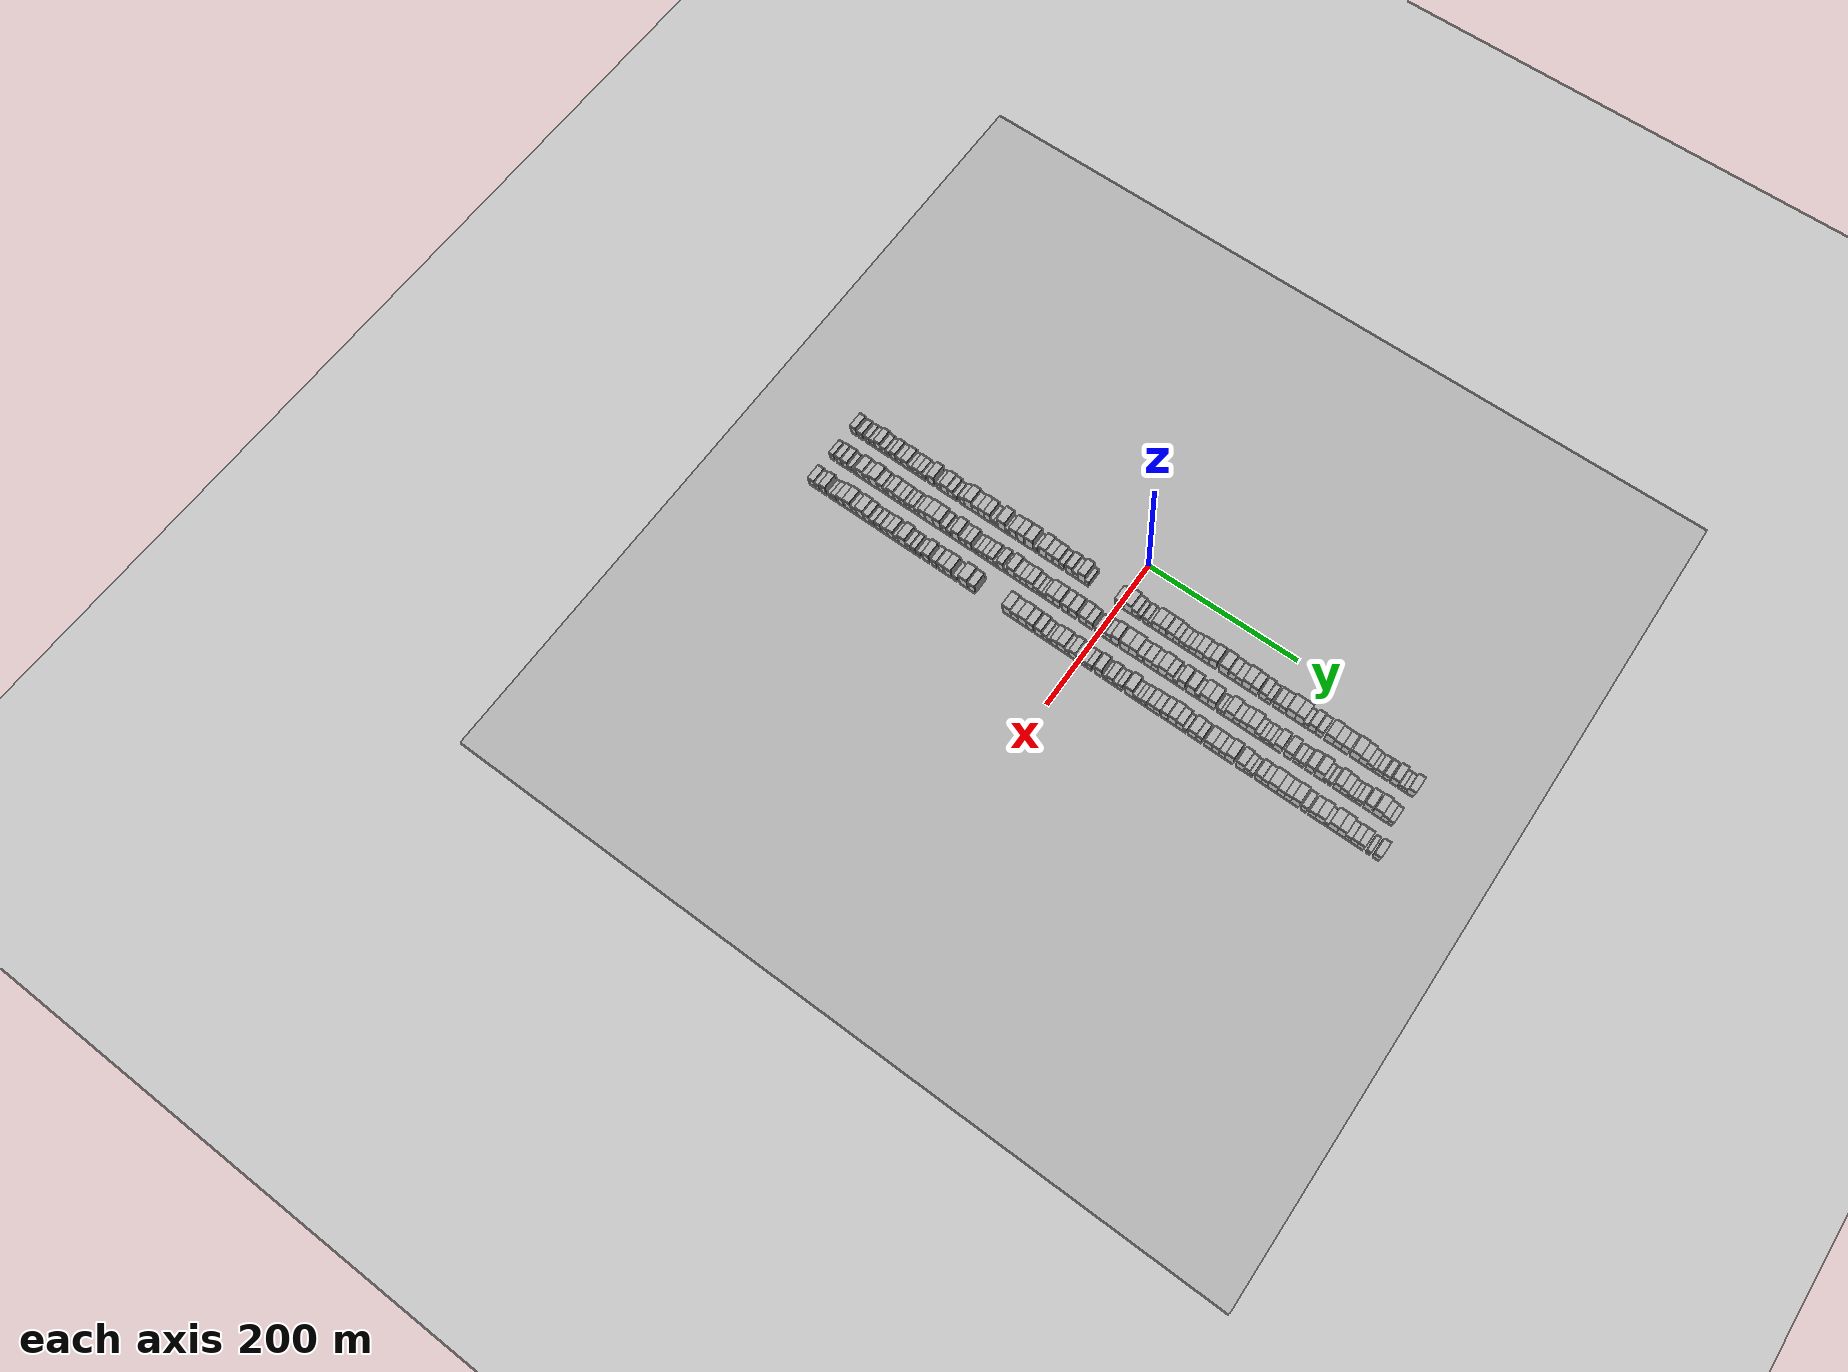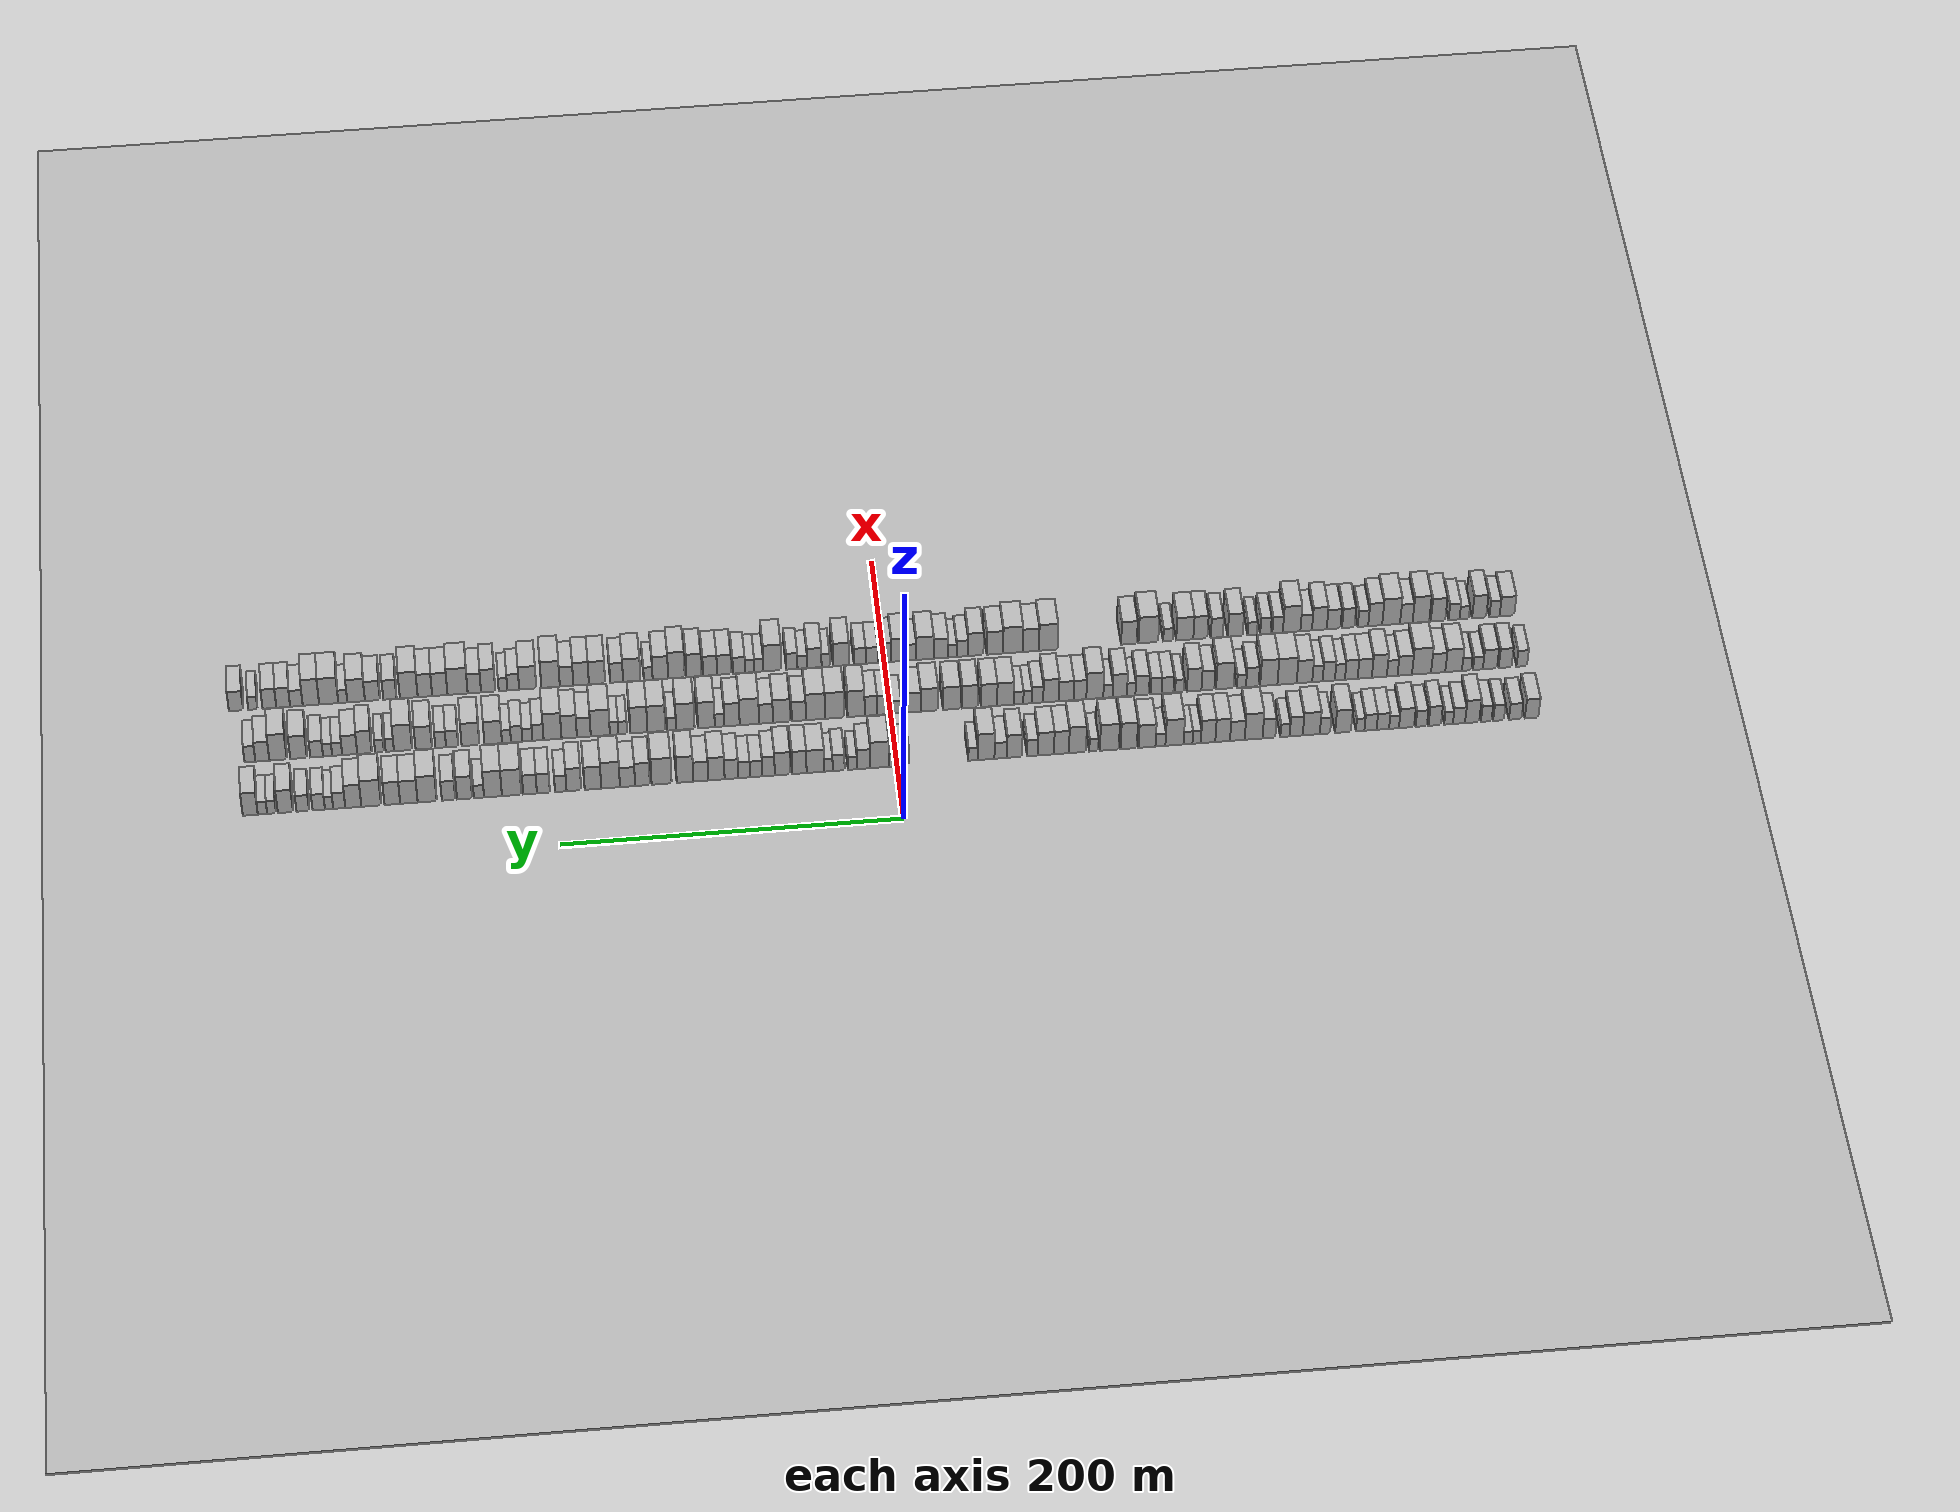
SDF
<?xml version="1.0" encoding="utf-8"?>

<sdf version="1.6">

   <world name="default">

      <gui fullscreen="0">

         <camera name="user_camera">

            <pose>-15 0 4.57585 0 0 0</pose>

            <view_controller>orbit</view_controller>

         </camera>

      </gui>

      <scene>

         <sky>

           <clouds>

             <speed>12</speed>

           </clouds>

         </sky>

         <ambient>0.4 0.4 0.4 1</ambient>

         <background>0.7 0.7 0.7 1</background>

         <shadows>1</shadows>

      </scene>

      <gravity>0 0 -9.8066</gravity>

      <magnetic_field>6e-06 2.3e-05 -4.2e-05</magnetic_field>

      <physics default="0" name="default_physics" type="ode">

         <ode>

            <solver>

               <type>quick</type>

               <iters>10</iters>

               <sor>1.0</sor>

               <use_dynamic_moi_rescaling>0</use_dynamic_moi_rescaling>

            </solver>

            <constraints>

               <cfm>0</cfm>

               <erp>0.2</erp>

               <contact_max_correcting_vel>100</contact_max_correcting_vel>

               <contact_surface_layer>0.001</contact_surface_layer>

            </constraints>

         </ode>

         <max_step_size>0.004</max_step_size>

         <real_time_factor>1</real_time_factor>

         <real_time_update_rate>250</real_time_update_rate>

      </physics>

      <light name="sun" type="directional">

         <cast_shadows>1</cast_shadows>

         <pose>0 0 10 0 0 0</pose>

         <diffuse>0.8 0.8 0.8 1</diffuse>

         <specular>0.2 0.2 0.2 1</specular>

         <attenuation>

            <range>1000</range>

            <constant>0.9</constant>

            <linear>0.01</linear>

            <quadratic>0.001</quadratic>

         </attenuation>

         <direction>-0.5 0.1 -0.9</direction>

      </light>

      <include>

         <name>ground_plane_1</name>

         <uri>model://HANNAS_ground_plane</uri>

         <pose>0 0 0  0 0 0</pose>

      </include>

      <include>

         <name>ground_plane_2</name>

         <uri>model://HANNAS_ground_plane</uri>

         <pose>100 0 0  0 0 0</pose>

      </include>

      <model name="building_1">

         <static>1</static>

         <pose frame="">50.0000 -375.9654 0 0.000000 0.000000 0.000000</pose>

         <link name="link">

            <pose frame="">0 0 9.00 0 0 0</pose>

            <collision name="collision">

               <geometry>

                  <box>

                     <size>20.0000 8.0692 18.0000</size>

                  </box>

               </geometry>

               <max_contacts>10</max_contacts>

               <surface>

                  <contact>

                     <ode/>

                  </contact>

                  <bounce/>

                  <friction>

                     <torsional>

                        <ode/>

                     </torsional>

                     <ode/>

                  </friction>

               </surface>

            </collision>

            <visual name="visual">

               <cast_shadows>0</cast_shadows>

               <geometry>

                  <box>

                     <size>20.0000 8.0692 18.0000</size>

                  </box>

               </geometry>

               <material>

                  <script>

                     <uri>model://HANNAS_wall/materials/scripts</uri>

                     <uri>model://HANNAS_wall/materials/textures</uri>

                     <name>vrc/HANNAS_wall</name>

                  </script>

               </material>

            </visual>

            <self_collide>0</self_collide>

            <enable_wind>0</enable_wind>

            <kinematic>0</kinematic>

         </link>

      </model>

      <model name="building_2">

         <static>1</static>

         <pose frame="">50.0000 -366.1815 0 0.000000 0.000000 0.000000</pose>

         <link name="link">

            <pose frame="">0 0 7.50 0 0 0</pose>

            <collision name="collision">

               <geometry>

                  <box>

                     <size>20.0000 7.4985 15.0000</size>

                  </box>

               </geometry>

               <max_contacts>10</max_contacts>

               <surface>

                  <contact>

                     <ode/>

                  </contact>

                  <bounce/>

                  <friction>

                     <torsional>

                        <ode/>

                     </torsional>

                     <ode/>

                  </friction>

               </surface>

            </collision>

            <visual name="visual">

               <cast_shadows>0</cast_shadows>

               <geometry>

                  <box>

                     <size>20.0000 7.4985 15.0000</size>

                  </box>

               </geometry>

               <material>

                  <script>

                     <uri>model://HANNAS_wall/materials/scripts</uri>

                     <uri>model://HANNAS_wall/materials/textures</uri>

                     <name>vrc/HANNAS_wall</name>

                  </script>

               </material>

            </visual>

            <self_collide>0</self_collide>

            <enable_wind>0</enable_wind>

            <kinematic>0</kinematic>

         </link>

      </model>

      <model name="building_3">

         <static>1</static>

         <pose frame="">50.0000 -356.2268 0 0.000000 0.000000 0.000000</pose>

         <link name="link">

            <pose frame="">0 0 7.50 0 0 0</pose>

            <collision name="collision">

               <geometry>

                  <box>

                     <size>20.0000 6.4109 15.0000</size>

                  </box>

               </geometry>

               <max_contacts>10</max_contacts>

               <surface>

                  <contact>

                     <ode/>

                  </contact>

                  <bounce/>

                  <friction>

                     <torsional>

                        <ode/>

                     </torsional>

                     <ode/>

                  </friction>

               </surface>

            </collision>

            <visual name="visual">

               <cast_shadows>0</cast_shadows>

               <geometry>

                  <box>

                     <size>20.0000 6.4109 15.0000</size>

                  </box>

               </geometry>

               <material>

                  <script>

                     <uri>model://HANNAS_wall/materials/scripts</uri>

                     <uri>model://HANNAS_wall/materials/textures</uri>

                     <name>vrc/HANNAS_wall</name>

                  </script>

               </material>

            </visual>

            <self_collide>0</self_collide>

            <enable_wind>0</enable_wind>

            <kinematic>0</kinematic>

         </link>

      </model>

      <model name="building_4">

         <static>1</static>

         <pose frame="">50.0000 -348.8674 0 0.000000 0.000000 0.000000</pose>

         <link name="link">

            <pose frame="">0 0 7.50 0 0 0</pose>

            <collision name="collision">

               <geometry>

                  <box>

                     <size>20.0000 6.3079 15.0000</size>

                  </box>

               </geometry>

               <max_contacts>10</max_contacts>

               <surface>

                  <contact>

                     <ode/>

                  </contact>

                  <bounce/>

                  <friction>

                     <torsional>

                        <ode/>

                     </torsional>

                     <ode/>

                  </friction>

               </surface>

            </collision>

            <visual name="visual">

               <cast_shadows>0</cast_shadows>

               <geometry>

                  <box>

                     <size>20.0000 6.3079 15.0000</size>

                  </box>

               </geometry>

               <material>

                  <script>

                     <uri>model://HANNAS_wall/materials/scripts</uri>

                     <uri>model://HANNAS_wall/materials/textures</uri>

                     <name>vrc/HANNAS_wall</name>

                  </script>

               </material>

            </visual>

            <self_collide>0</self_collide>

            <enable_wind>0</enable_wind>

            <kinematic>0</kinematic>

         </link>

      </model>

      <model name="building_5">

         <static>1</static>

         <pose frame="">50.0000 -340.4998 0 0.000000 0.000000 0.000000</pose>

         <link name="link">

            <pose frame="">0 0 10.50 0 0 0</pose>

            <collision name="collision">

               <geometry>

                  <box>

                     <size>20.0000 8.4273 21.0000</size>

                  </box>

               </geometry>

               <max_contacts>10</max_contacts>

               <surface>

                  <contact>

                     <ode/>

                  </contact>

                  <bounce/>

                  <friction>

                     <torsional>

                        <ode/>

                     </torsional>

                     <ode/>

                  </friction>

               </surface>

            </collision>

            <visual name="visual">

               <cast_shadows>0</cast_shadows>

               <geometry>

                  <box>

                     <size>20.0000 8.4273 21.0000</size>

                  </box>

               </geometry>

               <material>

                  <script>

                     <uri>model://HANNAS_wall/materials/scripts</uri>

                     <uri>model://HANNAS_wall/materials/textures</uri>

                     <name>vrc/HANNAS_wall</name>

                  </script>

               </material>

            </visual>

            <self_collide>0</self_collide>

            <enable_wind>0</enable_wind>

            <kinematic>0</kinematic>

         </link>

      </model>

      <model name="building_6">

         <static>1</static>

         <pose frame="">50.0000 -332.6491 0 0.000000 0.000000 0.000000</pose>

         <link name="link">

            <pose frame="">0 0 7.50 0 0 0</pose>

            <collision name="collision">

               <geometry>

                  <box>

                     <size>20.0000 7.2742 15.0000</size>

                  </box>

               </geometry>

               <max_contacts>10</max_contacts>

               <surface>

                  <contact>

                     <ode/>

                  </contact>

                  <bounce/>

                  <friction>

                     <torsional>

                        <ode/>

                     </torsional>

                     <ode/>

                  </friction>

               </surface>

            </collision>

            <visual name="visual">

               <cast_shadows>0</cast_shadows>

               <geometry>

                  <box>

                     <size>20.0000 7.2742 15.0000</size>

                  </box>

               </geometry>

               <material>

                  <script>

                     <uri>model://HANNAS_wall/materials/scripts</uri>

                     <uri>model://HANNAS_wall/materials/textures</uri>

                     <name>vrc/HANNAS_wall</name>

                  </script>

               </material>

            </visual>

            <self_collide>0</self_collide>

            <enable_wind>0</enable_wind>

            <kinematic>0</kinematic>

         </link>

      </model>

      <model name="building_7">

         <static>1</static>

         <pose frame="">50.0000 -326.4357 0 0.000000 0.000000 0.000000</pose>

         <link name="link">

            <pose frame="">0 0 6.00 0 0 0</pose>

            <collision name="collision">

               <geometry>

                  <box>

                     <size>20.0000 5.1526 12.0000</size>

                  </box>

               </geometry>

               <max_contacts>10</max_contacts>

               <surface>

                  <contact>

                     <ode/>

                  </contact>

                  <bounce/>

                  <friction>

                     <torsional>

                        <ode/>

                     </torsional>

                     <ode/>

                  </friction>

               </surface>

            </collision>

            <visual name="visual">

               <cast_shadows>0</cast_shadows>

               <geometry>

                  <box>

                     <size>20.0000 5.1526 12.0000</size>

                  </box>

               </geometry>

               <material>

                  <script>

                     <uri>model://HANNAS_wall/materials/scripts</uri>

                     <uri>model://HANNAS_wall/materials/textures</uri>

                     <name>vrc/HANNAS_wall</name>

                  </script>

               </material>

            </visual>

            <self_collide>0</self_collide>

            <enable_wind>0</enable_wind>

            <kinematic>0</kinematic>

         </link>

      </model>

      <model name="building_8">

         <static>1</static>

         <pose frame="">50.0000 -318.1620 0 0.000000 0.000000 0.000000</pose>

         <link name="link">

            <pose frame="">0 0 9.00 0 0 0</pose>

            <collision name="collision">

               <geometry>

                  <box>

                     <size>20.0000 7.3948 18.0000</size>

                  </box>

               </geometry>

               <max_contacts>10</max_contacts>

               <surface>

                  <contact>

                     <ode/>

                  </contact>

                  <bounce/>

                  <friction>

                     <torsional>

                        <ode/>

                     </torsional>

                     <ode/>

                  </friction>

               </surface>

            </collision>

            <visual name="visual">

               <cast_shadows>0</cast_shadows>

               <geometry>

                  <box>

                     <size>20.0000 7.3948 18.0000</size>

                  </box>

               </geometry>

               <material>

                  <script>

                     <uri>model://HANNAS_wall/materials/scripts</uri>

                     <uri>model://HANNAS_wall/materials/textures</uri>

                     <name>vrc/HANNAS_wall</name>

                  </script>

               </material>

            </visual>

            <self_collide>0</self_collide>

            <enable_wind>0</enable_wind>

            <kinematic>0</kinematic>

         </link>

      </model>

      <model name="building_9">

         <static>1</static>

         <pose frame="">50.0000 -310.1346 0 0.000000 0.000000 0.000000</pose>

         <link name="link">

            <pose frame="">0 0 7.50 0 0 0</pose>

            <collision name="collision">

               <geometry>

                  <box>

                     <size>20.0000 6.6600 15.0000</size>

                  </box>

               </geometry>

               <max_contacts>10</max_contacts>

               <surface>

                  <contact>

                     <ode/>

                  </contact>

                  <bounce/>

                  <friction>

                     <torsional>

                        <ode/>

                     </torsional>

                     <ode/>

                  </friction>

               </surface>

            </collision>

            <visual name="visual">

               <cast_shadows>0</cast_shadows>

               <geometry>

                  <box>

                     <size>20.0000 6.6600 15.0000</size>

                  </box>

               </geometry>

               <material>

                  <script>

                     <uri>model://HANNAS_wall/materials/scripts</uri>

                     <uri>model://HANNAS_wall/materials/textures</uri>

                     <name>vrc/HANNAS_wall</name>

                  </script>

               </material>

            </visual>

            <self_collide>0</self_collide>

            <enable_wind>0</enable_wind>

            <kinematic>0</kinematic>

         </link>

      </model>

      <model name="building_10">

         <static>1</static>

         <pose frame="">50.0000 -301.3234 0 0.000000 0.000000 0.000000</pose>

         <link name="link">

            <pose frame="">0 0 9.00 0 0 0</pose>

            <collision name="collision">

               <geometry>

                  <box>

                     <size>20.0000 8.9625 18.0000</size>

                  </box>

               </geometry>

               <max_contacts>10</max_contacts>

               <surface>

                  <contact>

                     <ode/>

                  </contact>

                  <bounce/>

                  <friction>

                     <torsional>

                        <ode/>

                     </torsional>

                     <ode/>

                  </friction>

               </surface>

            </collision>

            <visual name="visual">

               <cast_shadows>0</cast_shadows>

               <geometry>

                  <box>

                     <size>20.0000 8.9625 18.0000</size>

                  </box>

               </geometry>

               <material>

                  <script>

                     <uri>model://HANNAS_wall/materials/scripts</uri>

                     <uri>model://HANNAS_wall/materials/textures</uri>

                     <name>vrc/HANNAS_wall</name>

                  </script>

               </material>

            </visual>

            <self_collide>0</self_collide>

            <enable_wind>0</enable_wind>

            <kinematic>0</kinematic>

         </link>

      </model>

      <model name="building_11">

         <static>1</static>

         <pose frame="">50.0000 -293.9074 0 0.000000 0.000000 0.000000</pose>

         <link name="link">

            <pose frame="">0 0 6.00 0 0 0</pose>

            <collision name="collision">

               <geometry>

                  <box>

                     <size>20.0000 5.8694 12.0000</size>

                  </box>

               </geometry>

               <max_contacts>10</max_contacts>

               <surface>

                  <contact>

                     <ode/>

                  </contact>

                  <bounce/>

                  <friction>

                     <torsional>

                        <ode/>

                     </torsional>

                     <ode/>

                  </friction>

               </surface>

            </collision>

            <visual name="visual">

               <cast_shadows>0</cast_shadows>

               <geometry>

                  <box>

                     <size>20.0000 5.8694 12.0000</size>

                  </box>

               </geometry>

               <material>

                  <script>

                     <uri>model://HANNAS_wall/materials/scripts</uri>

                     <uri>model://HANNAS_wall/materials/textures</uri>

                     <name>vrc/HANNAS_wall</name>

                  </script>

               </material>

            </visual>

            <self_collide>0</self_collide>

            <enable_wind>0</enable_wind>

            <kinematic>0</kinematic>

         </link>

      </model>

      <model name="building_12">

         <static>1</static>

         <pose frame="">50.0000 -287.2578 0 0.000000 0.000000 0.000000</pose>

         <link name="link">

            <pose frame="">0 0 7.50 0 0 0</pose>

            <collision name="collision">

               <geometry>

                  <box>

                     <size>20.0000 7.4297 15.0000</size>

                  </box>

               </geometry>

               <max_contacts>10</max_contacts>

               <surface>

                  <contact>

                     <ode/>

                  </contact>

                  <bounce/>

                  <friction>

                     <torsional>

                        <ode/>

                     </torsional>

                     <ode/>

                  </friction>

               </surface>

            </collision>

            <visual name="visual">

               <cast_shadows>0</cast_shadows>

               <geometry>

                  <box>

                     <size>20.0000 7.4297 15.0000</size>

                  </box>

               </geometry>

               <material>

                  <script>

                     <uri>model://HANNAS_wall/materials/scripts</uri>

                     <uri>model://HANNAS_wall/materials/textures</uri>

                     <name>vrc/HANNAS_wall</name>

                  </script>

               </material>

            </visual>

            <self_collide>0</self_collide>

            <enable_wind>0</enable_wind>

            <kinematic>0</kinematic>

         </link>

      </model>

      <model name="building_13">

         <static>1</static>

         <pose frame="">50.0000 -279.9120 0 0.000000 0.000000 0.000000</pose>

         <link name="link">

            <pose frame="">0 0 7.50 0 0 0</pose>

            <collision name="collision">

               <geometry>

                  <box>

                     <size>20.0000 7.2620 15.0000</size>

                  </box>

               </geometry>

               <max_contacts>10</max_contacts>

               <surface>

                  <contact>

                     <ode/>

                  </contact>

                  <bounce/>

                  <friction>

                     <torsional>

                        <ode/>

                     </torsional>

                     <ode/>

                  </friction>

               </surface>

            </collision>

            <visual name="visual">

               <cast_shadows>0</cast_shadows>

               <geometry>

                  <box>

                     <size>20.0000 7.2620 15.0000</size>

                  </box>

               </geometry>

               <material>

                  <script>

                     <uri>model://HANNAS_wall/materials/scripts</uri>

                     <uri>model://HANNAS_wall/materials/textures</uri>

                     <name>vrc/HANNAS_wall</name>

                  </script>

               </material>

            </visual>

            <self_collide>0</self_collide>

            <enable_wind>0</enable_wind>

            <kinematic>0</kinematic>

         </link>

      </model>

      <model name="building_14">

         <static>1</static>

         <pose frame="">50.0000 -273.7572 0 0.000000 0.000000 0.000000</pose>

         <link name="link">

            <pose frame="">0 0 6.00 0 0 0</pose>

            <collision name="collision">

               <geometry>

                  <box>

                     <size>20.0000 5.0476 12.0000</size>

                  </box>

               </geometry>

               <max_contacts>10</max_contacts>

               <surface>

                  <contact>

                     <ode/>

                  </contact>

                  <bounce/>

                  <friction>

                     <torsional>

                        <ode/>

                     </torsional>

                     <ode/>

                  </friction>

               </surface>

            </collision>

            <visual name="visual">

               <cast_shadows>0</cast_shadows>

               <geometry>

                  <box>

                     <size>20.0000 5.0476 12.0000</size>

                  </box>

               </geometry>

               <material>

                  <script>

                     <uri>model://HANNAS_wall/materials/scripts</uri>

                     <uri>model://HANNAS_wall/materials/textures</uri>

                     <name>vrc/HANNAS_wall</name>

                  </script>

               </material>

            </visual>

            <self_collide>0</self_collide>

            <enable_wind>0</enable_wind>

            <kinematic>0</kinematic>

         </link>

      </model>

      <model name="building_15">

         <static>1</static>

         <pose frame="">50.0000 -263.5407 0 0.000000 0.000000 0.000000</pose>

         <link name="link">

            <pose frame="">0 0 10.50 0 0 0</pose>

            <collision name="collision">

               <geometry>

                  <box>

                     <size>20.0000 9.3854 21.0000</size>

                  </box>

               </geometry>

               <max_contacts>10</max_contacts>

               <surface>

                  <contact>

                     <ode/>

                  </contact>

                  <bounce/>

                  <friction>

                     <torsional>

                        <ode/>

                     </torsional>

                     <ode/>

                  </friction>

               </surface>

            </collision>

            <visual name="visual">

               <cast_shadows>0</cast_shadows>

               <geometry>

                  <box>

                     <size>20.0000 9.3854 21.0000</size>

                  </box>

               </geometry>

               <material>

                  <script>

                     <uri>model://HANNAS_wall/materials/scripts</uri>

                     <uri>model://HANNAS_wall/materials/textures</uri>

                     <name>vrc/HANNAS_wall</name>

                  </script>

               </material>

            </visual>

            <self_collide>0</self_collide>

            <enable_wind>0</enable_wind>

            <kinematic>0</kinematic>

         </link>

      </model>

      <model name="building_16">

         <static>1</static>

         <pose frame="">50.0000 -252.7964 0 0.000000 0.000000 0.000000</pose>

         <link name="link">

            <pose frame="">0 0 7.50 0 0 0</pose>

            <collision name="collision">

               <geometry>

                  <box>

                     <size>20.0000 6.1031 15.0000</size>

                  </box>

               </geometry>

               <max_contacts>10</max_contacts>

               <surface>

                  <contact>

                     <ode/>

                  </contact>

                  <bounce/>

                  <friction>

                     <torsional>

                        <ode/>

                     </torsional>

                     <ode/>

                  </friction>

               </surface>

            </collision>

            <visual name="visual">

               <cast_shadows>0</cast_shadows>

               <geometry>

                  <box>

                     <size>20.0000 6.1031 15.0000</size>

                  </box>

               </geometry>

               <material>

                  <script>

                     <uri>model://HANNAS_wall/materials/scripts</uri>

                     <uri>model://HANNAS_wall/materials/textures</uri>

                     <name>vrc/HANNAS_wall</name>

                  </script>

               </material>

            </visual>

            <self_collide>0</self_collide>

            <enable_wind>0</enable_wind>

            <kinematic>0</kinematic>

         </link>

      </model>

      <model name="building_17">

         <static>1</static>

         <pose frame="">50.0000 -244.6731 0 0.000000 0.000000 0.000000</pose>

         <link name="link">

            <pose frame="">0 0 10.50 0 0 0</pose>

            <collision name="collision">

               <geometry>

                  <box>

                     <size>20.0000 10.1435 21.0000</size>

                  </box>

               </geometry>

               <max_contacts>10</max_contacts>

               <surface>

                  <contact>

                     <ode/>

                  </contact>

                  <bounce/>

                  <friction>

                     <torsional>

                        <ode/>

                     </torsional>

                     <ode/>

                  </friction>

               </surface>

            </collision>

            <visual name="visual">

               <cast_shadows>0</cast_shadows>

               <geometry>

                  <box>

                     <size>20.0000 10.1435 21.0000</size>

                  </box>

               </geometry>

               <material>

                  <script>

                     <uri>model://HANNAS_wall/materials/scripts</uri>

                     <uri>model://HANNAS_wall/materials/textures</uri>

                     <name>vrc/HANNAS_wall</name>

                  </script>

               </material>

            </visual>

            <self_collide>0</self_collide>

            <enable_wind>0</enable_wind>

            <kinematic>0</kinematic>

         </link>

      </model>

      <model name="building_18">

         <static>1</static>

         <pose frame="">50.0000 -235.7101 0 0.000000 0.000000 0.000000</pose>

         <link name="link">

            <pose frame="">0 0 9.00 0 0 0</pose>

            <collision name="collision">

               <geometry>

                  <box>

                     <size>20.0000 7.7825 18.0000</size>

                  </box>

               </geometry>

               <max_contacts>10</max_contacts>

               <surface>

                  <contact>

                     <ode/>

                  </contact>

                  <bounce/>

                  <friction>

                     <torsional>

                        <ode/>

                     </torsional>

                     <ode/>

                  </friction>

               </surface>

            </collision>

            <visual name="visual">

               <cast_shadows>0</cast_shadows>

               <geometry>

                  <box>

                     <size>20.0000 7.7825 18.0000</size>

                  </box>

               </geometry>

               <material>

                  <script>

                     <uri>model://HANNAS_wall/materials/scripts</uri>

                     <uri>model://HANNAS_wall/materials/textures</uri>

                     <name>vrc/HANNAS_wall</name>

                  </script>

               </material>

            </visual>

            <self_collide>0</self_collide>

            <enable_wind>0</enable_wind>

            <kinematic>0</kinematic>

         </link>

      </model>

      <model name="building_19">

         <static>1</static>

         <pose frame="">50.0000 -229.0396 0 0.000000 0.000000 0.000000</pose>

         <link name="link">

            <pose frame="">0 0 6.00 0 0 0</pose>

            <collision name="collision">

               <geometry>

                  <box>

                     <size>20.0000 5.5586 12.0000</size>

                  </box>

               </geometry>

               <max_contacts>10</max_contacts>

               <surface>

                  <contact>

                     <ode/>

                  </contact>

                  <bounce/>

                  <friction>

                     <torsional>

                        <ode/>

                     </torsional>

                     <ode/>

                  </friction>

               </surface>

            </collision>

            <visual name="visual">

               <cast_shadows>0</cast_shadows>

               <geometry>

                  <box>

                     <size>20.0000 5.5586 12.0000</size>

                  </box>

               </geometry>

               <material>

                  <script>

                     <uri>model://HANNAS_wall/materials/scripts</uri>

                     <uri>model://HANNAS_wall/materials/textures</uri>

                     <name>vrc/HANNAS_wall</name>

                  </script>

               </material>

            </visual>

            <self_collide>0</self_collide>

            <enable_wind>0</enable_wind>

            <kinematic>0</kinematic>

         </link>

      </model>

      <model name="building_20">

         <static>1</static>

         <pose frame="">50.0000 -219.4842 0 0.000000 0.000000 0.000000</pose>

         <link name="link">

            <pose frame="">0 0 9.00 0 0 0</pose>

            <collision name="collision">

               <geometry>

                  <box>

                     <size>20.0000 7.5521 18.0000</size>

                  </box>

               </geometry>

               <max_contacts>10</max_contacts>

               <surface>

                  <contact>

                     <ode/>

                  </contact>

                  <bounce/>

                  <friction>

                     <torsional>

                        <ode/>

                     </torsional>

                     <ode/>

                  </friction>

               </surface>

            </collision>

            <visual name="visual">

               <cast_shadows>0</cast_shadows>

               <geometry>

                  <box>

                     <size>20.0000 7.5521 18.0000</size>

                  </box>

               </geometry>

               <material>

                  <script>

                     <uri>model://HANNAS_wall/materials/scripts</uri>

                     <uri>model://HANNAS_wall/materials/textures</uri>

                     <name>vrc/HANNAS_wall</name>

                  </script>

               </material>

            </visual>

            <self_collide>0</self_collide>

            <enable_wind>0</enable_wind>

            <kinematic>0</kinematic>

         </link>

      </model>

      <model name="building_21">

         <static>1</static>

         <pose frame="">50.0000 -210.4053 0 0.000000 0.000000 0.000000</pose>

         <link name="link">

            <pose frame="">0 0 12.00 0 0 0</pose>

            <collision name="collision">

               <geometry>

                  <box>

                     <size>20.0000 10.6058 24.0000</size>

                  </box>

               </geometry>

               <max_contacts>10</max_contacts>

               <surface>

                  <contact>

                     <ode/>

                  </contact>

                  <bounce/>

                  <friction>

                     <torsional>

                        <ode/>

                     </torsional>

                     <ode/>

                  </friction>

               </surface>

            </collision>

            <visual name="visual">

               <cast_shadows>0</cast_shadows>

               <geometry>

                  <box>

                     <size>20.0000 10.6058 24.0000</size>

                  </box>

               </geometry>

               <material>

                  <script>

                     <uri>model://HANNAS_wall/materials/scripts</uri>

                     <uri>model://HANNAS_wall/materials/textures</uri>

                     <name>vrc/HANNAS_wall</name>

                  </script>

               </material>

            </visual>

            <self_collide>0</self_collide>

            <enable_wind>0</enable_wind>

            <kinematic>0</kinematic>

         </link>

      </model>

      <model name="building_22">

         <static>1</static>

         <pose frame="">50.0000 -200.7312 0 0.000000 0.000000 0.000000</pose>

         <link name="link">

            <pose frame="">0 0 9.00 0 0 0</pose>

            <collision name="collision">

               <geometry>

                  <box>

                     <size>20.0000 8.7424 18.0000</size>

                  </box>

               </geometry>

               <max_contacts>10</max_contacts>

               <surface>

                  <contact>

                     <ode/>

                  </contact>

                  <bounce/>

                  <friction>

                     <torsional>

                        <ode/>

                     </torsional>

                     <ode/>

                  </friction>

               </surface>

            </collision>

            <visual name="visual">

               <cast_shadows>0</cast_shadows>

               <geometry>

                  <box>

                     <size>20.0000 8.7424 18.0000</size>

                  </box>

               </geometry>

               <material>

                  <script>

                     <uri>model://HANNAS_wall/materials/scripts</uri>

                     <uri>model://HANNAS_wall/materials/textures</uri>

                     <name>vrc/HANNAS_wall</name>

                  </script>

               </material>

            </visual>

            <self_collide>0</self_collide>

            <enable_wind>0</enable_wind>

            <kinematic>0</kinematic>

         </link>

      </model>

      <model name="building_23">

         <static>1</static>

         <pose frame="">50.0000 -192.0016 0 0.000000 0.000000 0.000000</pose>

         <link name="link">

            <pose frame="">0 0 10.50 0 0 0</pose>

            <collision name="collision">

               <geometry>

                  <box>

                     <size>20.0000 8.7167 21.0000</size>

                  </box>

               </geometry>

               <max_contacts>10</max_contacts>

               <surface>

                  <contact>

                     <ode/>

                  </contact>

                  <bounce/>

                  <friction>

                     <torsional>

                        <ode/>

                     </torsional>

                     <ode/>

                  </friction>

               </surface>

            </collision>

            <visual name="visual">

               <cast_shadows>0</cast_shadows>

               <geometry>

                  <box>

                     <size>20.0000 8.7167 21.0000</size>

                  </box>

               </geometry>

               <material>

                  <script>

                     <uri>model://HANNAS_wall/materials/scripts</uri>

                     <uri>model://HANNAS_wall/materials/textures</uri>

                     <name>vrc/HANNAS_wall</name>

                  </script>

               </material>

            </visual>

            <self_collide>0</self_collide>

            <enable_wind>0</enable_wind>

            <kinematic>0</kinematic>

         </link>

      </model>

      <model name="building_24">

         <static>1</static>

         <pose frame="">50.0000 -183.3436 0 0.000000 0.000000 0.000000</pose>

         <link name="link">

            <pose frame="">0 0 10.50 0 0 0</pose>

            <collision name="collision">

               <geometry>

                  <box>

                     <size>20.0000 8.5995 21.0000</size>

                  </box>

               </geometry>

               <max_contacts>10</max_contacts>

               <surface>

                  <contact>

                     <ode/>

                  </contact>

                  <bounce/>

                  <friction>

                     <torsional>

                        <ode/>

                     </torsional>

                     <ode/>

                  </friction>

               </surface>

            </collision>

            <visual name="visual">

               <cast_shadows>0</cast_shadows>

               <geometry>

                  <box>

                     <size>20.0000 8.5995 21.0000</size>

                  </box>

               </geometry>

               <material>

                  <script>

                     <uri>model://HANNAS_wall/materials/scripts</uri>

                     <uri>model://HANNAS_wall/materials/textures</uri>

                     <name>vrc/HANNAS_wall</name>

                  </script>

               </material>

            </visual>

            <self_collide>0</self_collide>

            <enable_wind>0</enable_wind>

            <kinematic>0</kinematic>

         </link>

      </model>

      <model name="building_25">

         <static>1</static>

         <pose frame="">50.0000 -176.5685 0 0.000000 0.000000 0.000000</pose>

         <link name="link">

            <pose frame="">0 0 6.00 0 0 0</pose>

            <collision name="collision">

               <geometry>

                  <box>

                     <size>20.0000 4.9507 12.0000</size>

                  </box>

               </geometry>

               <max_contacts>10</max_contacts>

               <surface>

                  <contact>

                     <ode/>

                  </contact>

                  <bounce/>

                  <friction>

                     <torsional>

                        <ode/>

                     </torsional>

                     <ode/>

                  </friction>

               </surface>

            </collision>

            <visual name="visual">

               <cast_shadows>0</cast_shadows>

               <geometry>

                  <box>

                     <size>20.0000 4.9507 12.0000</size>

                  </box>

               </geometry>

               <material>

                  <script>

                     <uri>model://HANNAS_wall/materials/scripts</uri>

                     <uri>model://HANNAS_wall/materials/textures</uri>

                     <name>vrc/HANNAS_wall</name>

                  </script>

               </material>

            </visual>

            <self_collide>0</self_collide>

            <enable_wind>0</enable_wind>

            <kinematic>0</kinematic>

         </link>

      </model>

      <model name="building_26">

         <static>1</static>

         <pose frame="">50.0000 -171.4349 0 0.000000 0.000000 0.000000</pose>

         <link name="link">

            <pose frame="">0 0 6.00 0 0 0</pose>

            <collision name="collision">

               <geometry>

                  <box>

                     <size>20.0000 5.3165 12.0000</size>

                  </box>

               </geometry>

               <max_contacts>10</max_contacts>

               <surface>

                  <contact>

                     <ode/>

                  </contact>

                  <bounce/>

                  <friction>

                     <torsional>

                        <ode/>

                     </torsional>

                     <ode/>

                  </friction>

               </surface>

            </collision>

            <visual name="visual">

               <cast_shadows>0</cast_shadows>

               <geometry>

                  <box>

                     <size>20.0000 5.3165 12.0000</size>

                  </box>

               </geometry>

               <material>

                  <script>

                     <uri>model://HANNAS_wall/materials/scripts</uri>

                     <uri>model://HANNAS_wall/materials/textures</uri>

                     <name>vrc/HANNAS_wall</name>

                  </script>

               </material>

            </visual>

            <self_collide>0</self_collide>

            <enable_wind>0</enable_wind>

            <kinematic>0</kinematic>

         </link>

      </model>

      <model name="building_27">

         <static>1</static>

         <pose frame="">50.0000 -163.4091 0 0.000000 0.000000 0.000000</pose>

         <link name="link">

            <pose frame="">0 0 12.00 0 0 0</pose>

            <collision name="collision">

               <geometry>

                  <box>

                     <size>20.0000 10.7351 24.0000</size>

                  </box>

               </geometry>

               <max_contacts>10</max_contacts>

               <surface>

                  <contact>

                     <ode/>

                  </contact>

                  <bounce/>

                  <friction>

                     <torsional>

                        <ode/>

                     </torsional>

                     <ode/>

                  </friction>

               </surface>

            </collision>

            <visual name="visual">

               <cast_shadows>0</cast_shadows>

               <geometry>

                  <box>

                     <size>20.0000 10.7351 24.0000</size>

                  </box>

               </geometry>

               <material>

                  <script>

                     <uri>model://HANNAS_wall/materials/scripts</uri>

                     <uri>model://HANNAS_wall/materials/textures</uri>

                     <name>vrc/HANNAS_wall</name>

                  </script>

               </material>

            </visual>

            <self_collide>0</self_collide>

            <enable_wind>0</enable_wind>

            <kinematic>0</kinematic>

         </link>

      </model>

      <model name="building_28">

         <static>1</static>

         <pose frame="">50.0000 -155.1005 0 0.000000 0.000000 0.000000</pose>

         <link name="link">

            <pose frame="">0 0 6.00 0 0 0</pose>

            <collision name="collision">

               <geometry>

                  <box>

                     <size>20.0000 5.8822 12.0000</size>

                  </box>

               </geometry>

               <max_contacts>10</max_contacts>

               <surface>

                  <contact>

                     <ode/>

                  </contact>

                  <bounce/>

                  <friction>

                     <torsional>

                        <ode/>

                     </torsional>

                     <ode/>

                  </friction>

               </surface>

            </collision>

            <visual name="visual">

               <cast_shadows>0</cast_shadows>

               <geometry>

                  <box>

                     <size>20.0000 5.8822 12.0000</size>

                  </box>

               </geometry>

               <material>

                  <script>

                     <uri>model://HANNAS_wall/materials/scripts</uri>

                     <uri>model://HANNAS_wall/materials/textures</uri>

                     <name>vrc/HANNAS_wall</name>

                  </script>

               </material>

            </visual>

            <self_collide>0</self_collide>

            <enable_wind>0</enable_wind>

            <kinematic>0</kinematic>

         </link>

      </model>

      <model name="building_29">

         <static>1</static>

         <pose frame="">50.0000 -147.1350 0 0.000000 0.000000 0.000000</pose>

         <link name="link">

            <pose frame="">0 0 10.50 0 0 0</pose>

            <collision name="collision">

               <geometry>

                  <box>

                     <size>20.0000 10.0487 21.0000</size>

                  </box>

               </geometry>

               <max_contacts>10</max_contacts>

               <surface>

                  <contact>

                     <ode/>

                  </contact>

                  <bounce/>

                  <friction>

                     <torsional>

                        <ode/>

                     </torsional>

                     <ode/>

                  </friction>

               </surface>

            </collision>

            <visual name="visual">

               <cast_shadows>0</cast_shadows>

               <geometry>

                  <box>

                     <size>20.0000 10.0487 21.0000</size>

                  </box>

               </geometry>

               <material>

                  <script>

                     <uri>model://HANNAS_wall/materials/scripts</uri>

                     <uri>model://HANNAS_wall/materials/textures</uri>

                     <name>vrc/HANNAS_wall</name>

                  </script>

               </material>

            </visual>

            <self_collide>0</self_collide>

            <enable_wind>0</enable_wind>

            <kinematic>0</kinematic>

         </link>

      </model>

      <model name="building_30">

         <static>1</static>

         <pose frame="">50.0000 -136.2777 0 0.000000 0.000000 0.000000</pose>

         <link name="link">

            <pose frame="">0 0 12.00 0 0 0</pose>

            <collision name="collision">

               <geometry>

                  <box>

                     <size>20.0000 9.6658 24.0000</size>

                  </box>

               </geometry>

               <max_contacts>10</max_contacts>

               <surface>

                  <contact>

                     <ode/>

                  </contact>

                  <bounce/>

                  <friction>

                     <torsional>

                        <ode/>

                     </torsional>

                     <ode/>

                  </friction>

               </surface>

            </collision>

            <visual name="visual">

               <cast_shadows>0</cast_shadows>

               <geometry>

                  <box>

                     <size>20.0000 9.6658 24.0000</size>

                  </box>

               </geometry>

               <material>

                  <script>

                     <uri>model://HANNAS_wall/materials/scripts</uri>

                     <uri>model://HANNAS_wall/materials/textures</uri>

                     <name>vrc/HANNAS_wall</name>

                  </script>

               </material>

            </visual>

            <self_collide>0</self_collide>

            <enable_wind>0</enable_wind>

            <kinematic>0</kinematic>

         </link>

      </model>

      <model name="building_31">

         <static>1</static>

         <pose frame="">50.0000 -124.8210 0 0.000000 0.000000 0.000000</pose>

         <link name="link">

            <pose frame="">0 0 12.00 0 0 0</pose>

            <collision name="collision">

               <geometry>

                  <box>

                     <size>20.0000 11.2476 24.0000</size>

                  </box>

               </geometry>

               <max_contacts>10</max_contacts>

               <surface>

                  <contact>

                     <ode/>

                  </contact>

                  <bounce/>

                  <friction>

                     <torsional>

                        <ode/>

                     </torsional>

                     <ode/>

                  </friction>

               </surface>

            </collision>

            <visual name="visual">

               <cast_shadows>0</cast_shadows>

               <geometry>

                  <box>

                     <size>20.0000 11.2476 24.0000</size>

                  </box>

               </geometry>

               <material>

                  <script>

                     <uri>model://HANNAS_wall/materials/scripts</uri>

                     <uri>model://HANNAS_wall/materials/textures</uri>

                     <name>vrc/HANNAS_wall</name>

                  </script>

               </material>

            </visual>

            <self_collide>0</self_collide>

            <enable_wind>0</enable_wind>

            <kinematic>0</kinematic>

         </link>

      </model>

      <model name="building_32">

         <static>1</static>

         <pose frame="">50.0000 -115.5725 0 0.000000 0.000000 0.000000</pose>

         <link name="link">

            <pose frame="">0 0 6.00 0 0 0</pose>

            <collision name="collision">

               <geometry>

                  <box>

                     <size>20.0000 5.2493 12.0000</size>

                  </box>

               </geometry>

               <max_contacts>10</max_contacts>

               <surface>

                  <contact>

                     <ode/>

                  </contact>

                  <bounce/>

                  <friction>

                     <torsional>

                        <ode/>

                     </torsional>

                     <ode/>

                  </friction>

               </surface>

            </collision>

            <visual name="visual">

               <cast_shadows>0</cast_shadows>

               <geometry>

                  <box>

                     <size>20.0000 5.2493 12.0000</size>

                  </box>

               </geometry>

               <material>

                  <script>

                     <uri>model://HANNAS_wall/materials/scripts</uri>

                     <uri>model://HANNAS_wall/materials/textures</uri>

                     <name>vrc/HANNAS_wall</name>

                  </script>

               </material>

            </visual>

            <self_collide>0</self_collide>

            <enable_wind>0</enable_wind>

            <kinematic>0</kinematic>

         </link>

      </model>

      <model name="building_33">

         <static>1</static>

         <pose frame="">50.0000 -105.9204 0 0.000000 0.000000 0.000000</pose>

         <link name="link">

            <pose frame="">0 0 12.00 0 0 0</pose>

            <collision name="collision">

               <geometry>

                  <box>

                     <size>20.0000 10.0549 24.0000</size>

                  </box>

               </geometry>

               <max_contacts>10</max_contacts>

               <surface>

                  <contact>

                     <ode/>

                  </contact>

                  <bounce/>

                  <friction>

                     <torsional>

                        <ode/>

                     </torsional>

                     <ode/>

                  </friction>

               </surface>

            </collision>

            <visual name="visual">

               <cast_shadows>0</cast_shadows>

               <geometry>

                  <box>

                     <size>20.0000 10.0549 24.0000</size>

                  </box>

               </geometry>

               <material>

                  <script>

                     <uri>model://HANNAS_wall/materials/scripts</uri>

                     <uri>model://HANNAS_wall/materials/textures</uri>

                     <name>vrc/HANNAS_wall</name>

                  </script>

               </material>

            </visual>

            <self_collide>0</self_collide>

            <enable_wind>0</enable_wind>

            <kinematic>0</kinematic>

         </link>

      </model>

      <model name="building_34">

         <static>1</static>

         <pose frame="">50.0000 -96.4681 0 0.000000 0.000000 0.000000</pose>

         <link name="link">

            <pose frame="">0 0 10.50 0 0 0</pose>

            <collision name="collision">

               <geometry>

                  <box>

                     <size>20.0000 8.8497 21.0000</size>

                  </box>

               </geometry>

               <max_contacts>10</max_contacts>

               <surface>

                  <contact>

                     <ode/>

                  </contact>

                  <bounce/>

                  <friction>

                     <torsional>

                        <ode/>

                     </torsional>

                     <ode/>

                  </friction>

               </surface>

            </collision>

            <visual name="visual">

               <cast_shadows>0</cast_shadows>

               <geometry>

                  <box>

                     <size>20.0000 8.8497 21.0000</size>

                  </box>

               </geometry>

               <material>

                  <script>

                     <uri>model://HANNAS_wall/materials/scripts</uri>

                     <uri>model://HANNAS_wall/materials/textures</uri>

                     <name>vrc/HANNAS_wall</name>

                  </script>

               </material>

            </visual>

            <self_collide>0</self_collide>

            <enable_wind>0</enable_wind>

            <kinematic>0</kinematic>

         </link>

      </model>

      <model name="building_35">

         <static>1</static>

         <pose frame="">50.0000 -87.3076 0 0.000000 0.000000 0.000000</pose>

         <link name="link">

            <pose frame="">0 0 10.50 0 0 0</pose>

            <collision name="collision">

               <geometry>

                  <box>

                     <size>20.0000 9.4713 21.0000</size>

                  </box>

               </geometry>

               <max_contacts>10</max_contacts>

               <surface>

                  <contact>

                     <ode/>

                  </contact>

                  <bounce/>

                  <friction>

                     <torsional>

                        <ode/>

                     </torsional>

                     <ode/>

                  </friction>

               </surface>

            </collision>

            <visual name="visual">

               <cast_shadows>0</cast_shadows>

               <geometry>

                  <box>

                     <size>20.0000 9.4713 21.0000</size>

                  </box>

               </geometry>

               <material>

                  <script>

                     <uri>model://HANNAS_wall/materials/scripts</uri>

                     <uri>model://HANNAS_wall/materials/textures</uri>

                     <name>vrc/HANNAS_wall</name>

                  </script>

               </material>

            </visual>

            <self_collide>0</self_collide>

            <enable_wind>0</enable_wind>

            <kinematic>0</kinematic>

         </link>

      </model>

      <model name="building_36">

         <static>1</static>

         <pose frame="">50.0000 -79.3680 0 0.000000 0.000000 0.000000</pose>

         <link name="link">

            <pose frame="">0 0 7.50 0 0 0</pose>

            <collision name="collision">

               <geometry>

                  <box>

                     <size>20.0000 6.4079 15.0000</size>

                  </box>

               </geometry>

               <max_contacts>10</max_contacts>

               <surface>

                  <contact>

                     <ode/>

                  </contact>

                  <bounce/>

                  <friction>

                     <torsional>

                        <ode/>

                     </torsional>

                     <ode/>

                  </friction>

               </surface>

            </collision>

            <visual name="visual">

               <cast_shadows>0</cast_shadows>

               <geometry>

                  <box>

                     <size>20.0000 6.4079 15.0000</size>

                  </box>

               </geometry>

               <material>

                  <script>

                     <uri>model://HANNAS_wall/materials/scripts</uri>

                     <uri>model://HANNAS_wall/materials/textures</uri>

                     <name>vrc/HANNAS_wall</name>

                  </script>

               </material>

            </visual>

            <self_collide>0</self_collide>

            <enable_wind>0</enable_wind>

            <kinematic>0</kinematic>

         </link>

      </model>

      <model name="building_37">

         <static>1</static>

         <pose frame="">50.0000 -68.7371 0 0.000000 0.000000 0.000000</pose>

         <link name="link">

            <pose frame="">0 0 10.50 0 0 0</pose>

            <collision name="collision">

               <geometry>

                  <box>

                     <size>20.0000 8.8539 21.0000</size>

                  </box>

               </geometry>

               <max_contacts>10</max_contacts>

               <surface>

                  <contact>

                     <ode/>

                  </contact>

                  <bounce/>

                  <friction>

                     <torsional>

                        <ode/>

                     </torsional>

                     <ode/>

                  </friction>

               </surface>

            </collision>

            <visual name="visual">

               <cast_shadows>0</cast_shadows>

               <geometry>

                  <box>

                     <size>20.0000 8.8539 21.0000</size>

                  </box>

               </geometry>

               <material>

                  <script>

                     <uri>model://HANNAS_wall/materials/scripts</uri>

                     <uri>model://HANNAS_wall/materials/textures</uri>

                     <name>vrc/HANNAS_wall</name>

                  </script>

               </material>

            </visual>

            <self_collide>0</self_collide>

            <enable_wind>0</enable_wind>

            <kinematic>0</kinematic>

         </link>

      </model>

      <model name="building_38">

         <static>1</static>

         <pose frame="">50.0000 -60.5868 0 0.000000 0.000000 0.000000</pose>

         <link name="link">

            <pose frame="">0 0 7.50 0 0 0</pose>

            <collision name="collision">

               <geometry>

                  <box>

                     <size>20.0000 7.4467 15.0000</size>

                  </box>

               </geometry>

               <max_contacts>10</max_contacts>

               <surface>

                  <contact>

                     <ode/>

                  </contact>

                  <bounce/>

                  <friction>

                     <torsional>

                        <ode/>

                     </torsional>

                     <ode/>

                  </friction>

               </surface>

            </collision>

            <visual name="visual">

               <cast_shadows>0</cast_shadows>

               <geometry>

                  <box>

                     <size>20.0000 7.4467 15.0000</size>

                  </box>

               </geometry>

               <material>

                  <script>

                     <uri>model://HANNAS_wall/materials/scripts</uri>

                     <uri>model://HANNAS_wall/materials/textures</uri>

                     <name>vrc/HANNAS_wall</name>

                  </script>

               </material>

            </visual>

            <self_collide>0</self_collide>

            <enable_wind>0</enable_wind>

            <kinematic>0</kinematic>

         </link>

      </model>

      <model name="building_39">

         <static>1</static>

         <pose frame="">50.0000 -51.8741 0 0.000000 0.000000 0.000000</pose>

         <link name="link">

            <pose frame="">0 0 12.00 0 0 0</pose>

            <collision name="collision">

               <geometry>

                  <box>

                     <size>20.0000 9.9787 24.0000</size>

                  </box>

               </geometry>

               <max_contacts>10</max_contacts>

               <surface>

                  <contact>

                     <ode/>

                  </contact>

                  <bounce/>

                  <friction>

                     <torsional>

                        <ode/>

                     </torsional>

                     <ode/>

                  </friction>

               </surface>

            </collision>

            <visual name="visual">

               <cast_shadows>0</cast_shadows>

               <geometry>

                  <box>

                     <size>20.0000 9.9787 24.0000</size>

                  </box>

               </geometry>

               <material>

                  <script>

                     <uri>model://HANNAS_wall/materials/scripts</uri>

                     <uri>model://HANNAS_wall/materials/textures</uri>

                     <name>vrc/HANNAS_wall</name>

                  </script>

               </material>

            </visual>

            <self_collide>0</self_collide>

            <enable_wind>0</enable_wind>

            <kinematic>0</kinematic>

         </link>

      </model>

      <model name="building_40">

         <static>1</static>

         <pose frame="">50.0000 -44.1848 0 0.000000 0.000000 0.000000</pose>

         <link name="link">

            <pose frame="">0 0 6.00 0 0 0</pose>

            <collision name="collision">

               <geometry>

                  <box>

                     <size>20.0000 5.3999 12.0000</size>

                  </box>

               </geometry>

               <max_contacts>10</max_contacts>

               <surface>

                  <contact>

                     <ode/>

                  </contact>

                  <bounce/>

                  <friction>

                     <torsional>

                        <ode/>

                     </torsional>

                     <ode/>

                  </friction>

               </surface>

            </collision>

            <visual name="visual">

               <cast_shadows>0</cast_shadows>

               <geometry>

                  <box>

                     <size>20.0000 5.3999 12.0000</size>

                  </box>

               </geometry>

               <material>

                  <script>

                     <uri>model://HANNAS_wall/materials/scripts</uri>

                     <uri>model://HANNAS_wall/materials/textures</uri>

                     <name>vrc/HANNAS_wall</name>

                  </script>

               </material>

            </visual>

            <self_collide>0</self_collide>

            <enable_wind>0</enable_wind>

            <kinematic>0</kinematic>

         </link>

      </model>

      <model name="building_41">

         <static>1</static>

         <pose frame="">50.0000 -2.9925 0 0.000000 0.000000 0.000000</pose>

         <link name="link">

            <pose frame="">0 0 7.50 0 0 0</pose>

            <collision name="collision">

               <geometry>

                  <box>

                     <size>20.0000 6.9949 15.0000</size>

                  </box>

               </geometry>

               <max_contacts>10</max_contacts>

               <surface>

                  <contact>

                     <ode/>

                  </contact>

                  <bounce/>

                  <friction>

                     <torsional>

                        <ode/>

                     </torsional>

                     <ode/>

                  </friction>

               </surface>

            </collision>

            <visual name="visual">

               <cast_shadows>0</cast_shadows>

               <geometry>

                  <box>

                     <size>20.0000 6.9949 15.0000</size>

                  </box>

               </geometry>

               <material>

                  <script>

                     <uri>model://HANNAS_wall/materials/scripts</uri>

                     <uri>model://HANNAS_wall/materials/textures</uri>

                     <name>vrc/HANNAS_wall</name>

                  </script>

               </material>

            </visual>

            <self_collide>0</self_collide>

            <enable_wind>0</enable_wind>

            <kinematic>0</kinematic>

         </link>

      </model>

      <model name="building_42">

         <static>1</static>

         <pose frame="">50.0000 2.9377 0 0.000000 0.000000 0.000000</pose>

         <link name="link">

            <pose frame="">0 0 6.00 0 0 0</pose>

            <collision name="collision">

               <geometry>

                  <box>

                     <size>20.0000 4.8656 12.0000</size>

                  </box>

               </geometry>

               <max_contacts>10</max_contacts>

               <surface>

                  <contact>

                     <ode/>

                  </contact>

                  <bounce/>

                  <friction>

                     <torsional>

                        <ode/>

                     </torsional>

                     <ode/>

                  </friction>

               </surface>

            </collision>

            <visual name="visual">

               <cast_shadows>0</cast_shadows>

               <geometry>

                  <box>

                     <size>20.0000 4.8656 12.0000</size>

                  </box>

               </geometry>

               <material>

                  <script>

                     <uri>model://HANNAS_wall/materials/scripts</uri>

                     <uri>model://HANNAS_wall/materials/textures</uri>

                     <name>vrc/HANNAS_wall</name>

                  </script>

               </material>

            </visual>

            <self_collide>0</self_collide>

            <enable_wind>0</enable_wind>

            <kinematic>0</kinematic>

         </link>

      </model>

      <model name="building_43">

         <static>1</static>

         <pose frame="">50.0000 10.8347 0 0.000000 0.000000 0.000000</pose>

         <link name="link">

            <pose frame="">0 0 12.00 0 0 0</pose>

            <collision name="collision">

               <geometry>

                  <box>

                     <size>20.0000 10.9284 24.0000</size>

                  </box>

               </geometry>

               <max_contacts>10</max_contacts>

               <surface>

                  <contact>

                     <ode/>

                  </contact>

                  <bounce/>

                  <friction>

                     <torsional>

                        <ode/>

                     </torsional>

                     <ode/>

                  </friction>

               </surface>

            </collision>

            <visual name="visual">

               <cast_shadows>0</cast_shadows>

               <geometry>

                  <box>

                     <size>20.0000 10.9284 24.0000</size>

                  </box>

               </geometry>

               <material>

                  <script>

                     <uri>model://HANNAS_wall/materials/scripts</uri>

                     <uri>model://HANNAS_wall/materials/textures</uri>

                     <name>vrc/HANNAS_wall</name>

                  </script>

               </material>

            </visual>

            <self_collide>0</self_collide>

            <enable_wind>0</enable_wind>

            <kinematic>0</kinematic>

         </link>

      </model>

      <model name="building_44">

         <static>1</static>

         <pose frame="">50.0000 20.2627 0 0.000000 0.000000 0.000000</pose>

         <link name="link">

            <pose frame="">0 0 9.00 0 0 0</pose>

            <collision name="collision">

               <geometry>

                  <box>

                     <size>20.0000 7.9275 18.0000</size>

                  </box>

               </geometry>

               <max_contacts>10</max_contacts>

               <surface>

                  <contact>

                     <ode/>

                  </contact>

                  <bounce/>

                  <friction>

                     <torsional>

                        <ode/>

                     </torsional>

                     <ode/>

                  </friction>

               </surface>

            </collision>

            <visual name="visual">

               <cast_shadows>0</cast_shadows>

               <geometry>

                  <box>

                     <size>20.0000 7.9275 18.0000</size>

                  </box>

               </geometry>

               <material>

                  <script>

                     <uri>model://HANNAS_wall/materials/scripts</uri>

                     <uri>model://HANNAS_wall/materials/textures</uri>

                     <name>vrc/HANNAS_wall</name>

                  </script>

               </material>

            </visual>

            <self_collide>0</self_collide>

            <enable_wind>0</enable_wind>

            <kinematic>0</kinematic>

         </link>

      </model>

      <model name="building_45">

         <static>1</static>

         <pose frame="">50.0000 26.8715 0 0.000000 0.000000 0.000000</pose>

         <link name="link">

            <pose frame="">0 0 6.00 0 0 0</pose>

            <collision name="collision">

               <geometry>

                  <box>

                     <size>20.0000 5.2903 12.0000</size>

                  </box>

               </geometry>

               <max_contacts>10</max_contacts>

               <surface>

                  <contact>

                     <ode/>

                  </contact>

                  <bounce/>

                  <friction>

                     <torsional>

                        <ode/>

                     </torsional>

                     <ode/>

                  </friction>

               </surface>

            </collision>

            <visual name="visual">

               <cast_shadows>0</cast_shadows>

               <geometry>

                  <box>

                     <size>20.0000 5.2903 12.0000</size>

                  </box>

               </geometry>

               <material>

                  <script>

                     <uri>model://HANNAS_wall/materials/scripts</uri>

                     <uri>model://HANNAS_wall/materials/textures</uri>

                     <name>vrc/HANNAS_wall</name>

                  </script>

               </material>

            </visual>

            <self_collide>0</self_collide>

            <enable_wind>0</enable_wind>

            <kinematic>0</kinematic>

         </link>

      </model>

      <model name="building_46">

         <static>1</static>

         <pose frame="">50.0000 35.0334 0 0.000000 0.000000 0.000000</pose>

         <link name="link">

            <pose frame="">0 0 7.50 0 0 0</pose>

            <collision name="collision">

               <geometry>

                  <box>

                     <size>20.0000 7.0335 15.0000</size>

                  </box>

               </geometry>

               <max_contacts>10</max_contacts>

               <surface>

                  <contact>

                     <ode/>

                  </contact>

                  <bounce/>

                  <friction>

                     <torsional>

                        <ode/>

                     </torsional>

                     <ode/>

                  </friction>

               </surface>

            </collision>

            <visual name="visual">

               <cast_shadows>0</cast_shadows>

               <geometry>

                  <box>

                     <size>20.0000 7.0335 15.0000</size>

                  </box>

               </geometry>

               <material>

                  <script>

                     <uri>model://HANNAS_wall/materials/scripts</uri>

                     <uri>model://HANNAS_wall/materials/textures</uri>

                     <name>vrc/HANNAS_wall</name>

                  </script>

               </material>

            </visual>

            <self_collide>0</self_collide>

            <enable_wind>0</enable_wind>

            <kinematic>0</kinematic>

         </link>

      </model>

      <model name="building_47">

         <static>1</static>

         <pose frame="">50.0000 41.0266 0 0.000000 0.000000 0.000000</pose>

         <link name="link">

            <pose frame="">0 0 6.00 0 0 0</pose>

            <collision name="collision">

               <geometry>

                  <box>

                     <size>20.0000 4.9528 12.0000</size>

                  </box>

               </geometry>

               <max_contacts>10</max_contacts>

               <surface>

                  <contact>

                     <ode/>

                  </contact>

                  <bounce/>

                  <friction>

                     <torsional>

                        <ode/>

                     </torsional>

                     <ode/>

                  </friction>

               </surface>

            </collision>

            <visual name="visual">

               <cast_shadows>0</cast_shadows>

               <geometry>

                  <box>

                     <size>20.0000 4.9528 12.0000</size>

                  </box>

               </geometry>

               <material>

                  <script>

                     <uri>model://HANNAS_wall/materials/scripts</uri>

                     <uri>model://HANNAS_wall/materials/textures</uri>

                     <name>vrc/HANNAS_wall</name>

                  </script>

               </material>

            </visual>

            <self_collide>0</self_collide>

            <enable_wind>0</enable_wind>

            <kinematic>0</kinematic>

         </link>

      </model>

      <model name="building_48">

         <static>1</static>

         <pose frame="">50.0000 48.6818 0 0.000000 0.000000 0.000000</pose>

         <link name="link">

            <pose frame="">0 0 10.50 0 0 0</pose>

            <collision name="collision">

               <geometry>

                  <box>

                     <size>20.0000 10.3576 21.0000</size>

                  </box>

               </geometry>

               <max_contacts>10</max_contacts>

               <surface>

                  <contact>

                     <ode/>

                  </contact>

                  <bounce/>

                  <friction>

                     <torsional>

                        <ode/>

                     </torsional>

                     <ode/>

                  </friction>

               </surface>

            </collision>

            <visual name="visual">

               <cast_shadows>0</cast_shadows>

               <geometry>

                  <box>

                     <size>20.0000 10.3576 21.0000</size>

                  </box>

               </geometry>

               <material>

                  <script>

                     <uri>model://HANNAS_wall/materials/scripts</uri>

                     <uri>model://HANNAS_wall/materials/textures</uri>

                     <name>vrc/HANNAS_wall</name>

                  </script>

               </material>

            </visual>

            <self_collide>0</self_collide>

            <enable_wind>0</enable_wind>

            <kinematic>0</kinematic>

         </link>

      </model>

      <model name="building_49">

         <static>1</static>

         <pose frame="">50.0000 58.1059 0 0.000000 0.000000 0.000000</pose>

         <link name="link">

            <pose frame="">0 0 10.50 0 0 0</pose>

            <collision name="collision">

               <geometry>

                  <box>

                     <size>20.0000 8.4907 21.0000</size>

                  </box>

               </geometry>

               <max_contacts>10</max_contacts>

               <surface>

                  <contact>

                     <ode/>

                  </contact>

                  <bounce/>

                  <friction>

                     <torsional>

                        <ode/>

                     </torsional>

                     <ode/>

                  </friction>

               </surface>

            </collision>

            <visual name="visual">

               <cast_shadows>0</cast_shadows>

               <geometry>

                  <box>

                     <size>20.0000 8.4907 21.0000</size>

                  </box>

               </geometry>

               <material>

                  <script>

                     <uri>model://HANNAS_wall/materials/scripts</uri>

                     <uri>model://HANNAS_wall/materials/textures</uri>

                     <name>vrc/HANNAS_wall</name>

                  </script>

               </material>

            </visual>

            <self_collide>0</self_collide>

            <enable_wind>0</enable_wind>

            <kinematic>0</kinematic>

         </link>

      </model>

      <model name="building_50">

         <static>1</static>

         <pose frame="">50.0000 67.9712 0 0.000000 0.000000 0.000000</pose>

         <link name="link">

            <pose frame="">0 0 10.50 0 0 0</pose>

            <collision name="collision">

               <geometry>

                  <box>

                     <size>20.0000 9.2398 21.0000</size>

                  </box>

               </geometry>

               <max_contacts>10</max_contacts>

               <surface>

                  <contact>

                     <ode/>

                  </contact>

                  <bounce/>

                  <friction>

                     <torsional>

                        <ode/>

                     </torsional>

                     <ode/>

                  </friction>

               </surface>

            </collision>

            <visual name="visual">

               <cast_shadows>0</cast_shadows>

               <geometry>

                  <box>

                     <size>20.0000 9.2398 21.0000</size>

                  </box>

               </geometry>

               <material>

                  <script>

                     <uri>model://HANNAS_wall/materials/scripts</uri>

                     <uri>model://HANNAS_wall/materials/textures</uri>

                     <name>vrc/HANNAS_wall</name>

                  </script>

               </material>

            </visual>

            <self_collide>0</self_collide>

            <enable_wind>0</enable_wind>

            <kinematic>0</kinematic>

         </link>

      </model>

      <model name="building_51">

         <static>1</static>

         <pose frame="">50.0000 76.2383 0 0.000000 0.000000 0.000000</pose>

         <link name="link">

            <pose frame="">0 0 9.00 0 0 0</pose>

            <collision name="collision">

               <geometry>

                  <box>

                     <size>20.0000 7.2944 18.0000</size>

                  </box>

               </geometry>

               <max_contacts>10</max_contacts>

               <surface>

                  <contact>

                     <ode/>

                  </contact>

                  <bounce/>

                  <friction>

                     <torsional>

                        <ode/>

                     </torsional>

                     <ode/>

                  </friction>

               </surface>

            </collision>

            <visual name="visual">

               <cast_shadows>0</cast_shadows>

               <geometry>

                  <box>

                     <size>20.0000 7.2944 18.0000</size>

                  </box>

               </geometry>

               <material>

                  <script>

                     <uri>model://HANNAS_wall/materials/scripts</uri>

                     <uri>model://HANNAS_wall/materials/textures</uri>

                     <name>vrc/HANNAS_wall</name>

                  </script>

               </material>

            </visual>

            <self_collide>0</self_collide>

            <enable_wind>0</enable_wind>

            <kinematic>0</kinematic>

         </link>

      </model>

      <model name="building_52">

         <static>1</static>

         <pose frame="">50.0000 83.5238 0 0.000000 0.000000 0.000000</pose>

         <link name="link">

            <pose frame="">0 0 7.50 0 0 0</pose>

            <collision name="collision">

               <geometry>

                  <box>

                     <size>20.0000 7.2766 15.0000</size>

                  </box>

               </geometry>

               <max_contacts>10</max_contacts>

               <surface>

                  <contact>

                     <ode/>

                  </contact>

                  <bounce/>

                  <friction>

                     <torsional>

                        <ode/>

                     </torsional>

                     <ode/>

                  </friction>

               </surface>

            </collision>

            <visual name="visual">

               <cast_shadows>0</cast_shadows>

               <geometry>

                  <box>

                     <size>20.0000 7.2766 15.0000</size>

                  </box>

               </geometry>

               <material>

                  <script>

                     <uri>model://HANNAS_wall/materials/scripts</uri>

                     <uri>model://HANNAS_wall/materials/textures</uri>

                     <name>vrc/HANNAS_wall</name>

                  </script>

               </material>

            </visual>

            <self_collide>0</self_collide>

            <enable_wind>0</enable_wind>

            <kinematic>0</kinematic>

         </link>

      </model>

      <model name="building_53">

         <static>1</static>

         <pose frame="">50.0000 90.5950 0 0.000000 0.000000 0.000000</pose>

         <link name="link">

            <pose frame="">0 0 7.50 0 0 0</pose>

            <collision name="collision">

               <geometry>

                  <box>

                     <size>20.0000 6.8658 15.0000</size>

                  </box>

               </geometry>

               <max_contacts>10</max_contacts>

               <surface>

                  <contact>

                     <ode/>

                  </contact>

                  <bounce/>

                  <friction>

                     <torsional>

                        <ode/>

                     </torsional>

                     <ode/>

                  </friction>

               </surface>

            </collision>

            <visual name="visual">

               <cast_shadows>0</cast_shadows>

               <geometry>

                  <box>

                     <size>20.0000 6.8658 15.0000</size>

                  </box>

               </geometry>

               <material>

                  <script>

                     <uri>model://HANNAS_wall/materials/scripts</uri>

                     <uri>model://HANNAS_wall/materials/textures</uri>

                     <name>vrc/HANNAS_wall</name>

                  </script>

               </material>

            </visual>

            <self_collide>0</self_collide>

            <enable_wind>0</enable_wind>

            <kinematic>0</kinematic>

         </link>

      </model>

      <model name="building_54">

         <static>1</static>

         <pose frame="">50.0000 98.0356 0 0.000000 0.000000 0.000000</pose>

         <link name="link">

            <pose frame="">0 0 9.00 0 0 0</pose>

            <collision name="collision">

               <geometry>

                  <box>

                     <size>20.0000 8.0153 18.0000</size>

                  </box>

               </geometry>

               <max_contacts>10</max_contacts>

               <surface>

                  <contact>

                     <ode/>

                  </contact>

                  <bounce/>

                  <friction>

                     <torsional>

                        <ode/>

                     </torsional>

                     <ode/>

                  </friction>

               </surface>

            </collision>

            <visual name="visual">

               <cast_shadows>0</cast_shadows>

               <geometry>

                  <box>

                     <size>20.0000 8.0153 18.0000</size>

                  </box>

               </geometry>

               <material>

                  <script>

                     <uri>model://HANNAS_wall/materials/scripts</uri>

                     <uri>model://HANNAS_wall/materials/textures</uri>

                     <name>vrc/HANNAS_wall</name>

                  </script>

               </material>

            </visual>

            <self_collide>0</self_collide>

            <enable_wind>0</enable_wind>

            <kinematic>0</kinematic>

         </link>

      </model>

      <model name="building_55">

         <static>1</static>

         <pose frame="">50.0000 106.8641 0 0.000000 0.000000 0.000000</pose>

         <link name="link">

            <pose frame="">0 0 10.50 0 0 0</pose>

            <collision name="collision">

               <geometry>

                  <box>

                     <size>20.0000 9.6418 21.0000</size>

                  </box>

               </geometry>

               <max_contacts>10</max_contacts>

               <surface>

                  <contact>

                     <ode/>

                  </contact>

                  <bounce/>

                  <friction>

                     <torsional>

                        <ode/>

                     </torsional>

                     <ode/>

                  </friction>

               </surface>

            </collision>

            <visual name="visual">

               <cast_shadows>0</cast_shadows>

               <geometry>

                  <box>

                     <size>20.0000 9.6418 21.0000</size>

                  </box>

               </geometry>

               <material>

                  <script>

                     <uri>model://HANNAS_wall/materials/scripts</uri>

                     <uri>model://HANNAS_wall/materials/textures</uri>

                     <name>vrc/HANNAS_wall</name>

                  </script>

               </material>

            </visual>

            <self_collide>0</self_collide>

            <enable_wind>0</enable_wind>

            <kinematic>0</kinematic>

         </link>

      </model>

      <model name="building_56">

         <static>1</static>

         <pose frame="">50.0000 116.0233 0 0.000000 0.000000 0.000000</pose>

         <link name="link">

            <pose frame="">0 0 9.00 0 0 0</pose>

            <collision name="collision">

               <geometry>

                  <box>

                     <size>20.0000 8.6765 18.0000</size>

                  </box>

               </geometry>

               <max_contacts>10</max_contacts>

               <surface>

                  <contact>

                     <ode/>

                  </contact>

                  <bounce/>

                  <friction>

                     <torsional>

                        <ode/>

                     </torsional>

                     <ode/>

                  </friction>

               </surface>

            </collision>

            <visual name="visual">

               <cast_shadows>0</cast_shadows>

               <geometry>

                  <box>

                     <size>20.0000 8.6765 18.0000</size>

                  </box>

               </geometry>

               <material>

                  <script>

                     <uri>model://HANNAS_wall/materials/scripts</uri>

                     <uri>model://HANNAS_wall/materials/textures</uri>

                     <name>vrc/HANNAS_wall</name>

                  </script>

               </material>

            </visual>

            <self_collide>0</self_collide>

            <enable_wind>0</enable_wind>

            <kinematic>0</kinematic>

         </link>

      </model>

      <model name="building_57">

         <static>1</static>

         <pose frame="">50.0000 125.2580 0 0.000000 0.000000 0.000000</pose>

         <link name="link">

            <pose frame="">0 0 12.00 0 0 0</pose>

            <collision name="collision">

               <geometry>

                  <box>

                     <size>20.0000 9.7930 24.0000</size>

                  </box>

               </geometry>

               <max_contacts>10</max_contacts>

               <surface>

                  <contact>

                     <ode/>

                  </contact>

                  <bounce/>

                  <friction>

                     <torsional>

                        <ode/>

                     </torsional>

                     <ode/>

                  </friction>

               </surface>

            </collision>

            <visual name="visual">

               <cast_shadows>0</cast_shadows>

               <geometry>

                  <box>

                     <size>20.0000 9.7930 24.0000</size>

                  </box>

               </geometry>

               <material>

                  <script>

                     <uri>model://HANNAS_wall/materials/scripts</uri>

                     <uri>model://HANNAS_wall/materials/textures</uri>

                     <name>vrc/HANNAS_wall</name>

                  </script>

               </material>

            </visual>

            <self_collide>0</self_collide>

            <enable_wind>0</enable_wind>

            <kinematic>0</kinematic>

         </link>

      </model>

      <model name="building_58">

         <static>1</static>

         <pose frame="">50.0000 139.0167 0 0.000000 0.000000 0.000000</pose>

         <link name="link">

            <pose frame="">0 0 12.00 0 0 0</pose>

            <collision name="collision">

               <geometry>

                  <box>

                     <size>20.0000 11.7243 24.0000</size>

                  </box>

               </geometry>

               <max_contacts>10</max_contacts>

               <surface>

                  <contact>

                     <ode/>

                  </contact>

                  <bounce/>

                  <friction>

                     <torsional>

                        <ode/>

                     </torsional>

                     <ode/>

                  </friction>

               </surface>

            </collision>

            <visual name="visual">

               <cast_shadows>0</cast_shadows>

               <geometry>

                  <box>

                     <size>20.0000 11.7243 24.0000</size>

                  </box>

               </geometry>

               <material>

                  <script>

                     <uri>model://HANNAS_wall/materials/scripts</uri>

                     <uri>model://HANNAS_wall/materials/textures</uri>

                     <name>vrc/HANNAS_wall</name>

                  </script>

               </material>

            </visual>

            <self_collide>0</self_collide>

            <enable_wind>0</enable_wind>

            <kinematic>0</kinematic>

         </link>

      </model>

      <model name="building_59">

         <static>1</static>

         <pose frame="">50.0000 150.1968 0 0.000000 0.000000 0.000000</pose>

         <link name="link">

            <pose frame="">0 0 10.50 0 0 0</pose>

            <collision name="collision">

               <geometry>

                  <box>

                     <size>20.0000 8.6360 21.0000</size>

                  </box>

               </geometry>

               <max_contacts>10</max_contacts>

               <surface>

                  <contact>

                     <ode/>

                  </contact>

                  <bounce/>

                  <friction>

                     <torsional>

                        <ode/>

                     </torsional>

                     <ode/>

                  </friction>

               </surface>

            </collision>

            <visual name="visual">

               <cast_shadows>0</cast_shadows>

               <geometry>

                  <box>

                     <size>20.0000 8.6360 21.0000</size>

                  </box>

               </geometry>

               <material>

                  <script>

                     <uri>model://HANNAS_wall/materials/scripts</uri>

                     <uri>model://HANNAS_wall/materials/textures</uri>

                     <name>vrc/HANNAS_wall</name>

                  </script>

               </material>

            </visual>

            <self_collide>0</self_collide>

            <enable_wind>0</enable_wind>

            <kinematic>0</kinematic>

         </link>

      </model>

      <model name="building_60">

         <static>1</static>

         <pose frame="">50.0000 158.9674 0 0.000000 0.000000 0.000000</pose>

         <link name="link">

            <pose frame="">0 0 9.00 0 0 0</pose>

            <collision name="collision">

               <geometry>

                  <box>

                     <size>20.0000 8.9051 18.0000</size>

                  </box>

               </geometry>

               <max_contacts>10</max_contacts>

               <surface>

                  <contact>

                     <ode/>

                  </contact>

                  <bounce/>

                  <friction>

                     <torsional>

                        <ode/>

                     </torsional>

                     <ode/>

                  </friction>

               </surface>

            </collision>

            <visual name="visual">

               <cast_shadows>0</cast_shadows>

               <geometry>

                  <box>

                     <size>20.0000 8.9051 18.0000</size>

                  </box>

               </geometry>

               <material>

                  <script>

                     <uri>model://HANNAS_wall/materials/scripts</uri>

                     <uri>model://HANNAS_wall/materials/textures</uri>

                     <name>vrc/HANNAS_wall</name>

                  </script>

               </material>

            </visual>

            <self_collide>0</self_collide>

            <enable_wind>0</enable_wind>

            <kinematic>0</kinematic>

         </link>

      </model>

      <model name="building_61">

         <static>1</static>

         <pose frame="">50.0000 168.8890 0 0.000000 0.000000 0.000000</pose>

         <link name="link">

            <pose frame="">0 0 12.00 0 0 0</pose>

            <collision name="collision">

               <geometry>

                  <box>

                     <size>20.0000 10.9381 24.0000</size>

                  </box>

               </geometry>

               <max_contacts>10</max_contacts>

               <surface>

                  <contact>

                     <ode/>

                  </contact>

                  <bounce/>

                  <friction>

                     <torsional>

                        <ode/>

                     </torsional>

                     <ode/>

                  </friction>

               </surface>

            </collision>

            <visual name="visual">

               <cast_shadows>0</cast_shadows>

               <geometry>

                  <box>

                     <size>20.0000 10.9381 24.0000</size>

                  </box>

               </geometry>

               <material>

                  <script>

                     <uri>model://HANNAS_wall/materials/scripts</uri>

                     <uri>model://HANNAS_wall/materials/textures</uri>

                     <name>vrc/HANNAS_wall</name>

                  </script>

               </material>

            </visual>

            <self_collide>0</self_collide>

            <enable_wind>0</enable_wind>

            <kinematic>0</kinematic>

         </link>

      </model>

      <model name="building_62">

         <static>1</static>

         <pose frame="">50.0000 179.2238 0 0.000000 0.000000 0.000000</pose>

         <link name="link">

            <pose frame="">0 0 10.50 0 0 0</pose>

            <collision name="collision">

               <geometry>

                  <box>

                     <size>20.0000 9.7315 21.0000</size>

                  </box>

               </geometry>

               <max_contacts>10</max_contacts>

               <surface>

                  <contact>

                     <ode/>

                  </contact>

                  <bounce/>

                  <friction>

                     <torsional>

                        <ode/>

                     </torsional>

                     <ode/>

                  </friction>

               </surface>

            </collision>

            <visual name="visual">

               <cast_shadows>0</cast_shadows>

               <geometry>

                  <box>

                     <size>20.0000 9.7315 21.0000</size>

                  </box>

               </geometry>

               <material>

                  <script>

                     <uri>model://HANNAS_wall/materials/scripts</uri>

                     <uri>model://HANNAS_wall/materials/textures</uri>

                     <name>vrc/HANNAS_wall</name>

                  </script>

               </material>

            </visual>

            <self_collide>0</self_collide>

            <enable_wind>0</enable_wind>

            <kinematic>0</kinematic>

         </link>

      </model>

      <model name="building_63">

         <static>1</static>

         <pose frame="">50.0000 190.4064 0 0.000000 0.000000 0.000000</pose>

         <link name="link">

            <pose frame="">0 0 10.50 0 0 0</pose>

            <collision name="collision">

               <geometry>

                  <box>

                     <size>20.0000 8.6338 21.0000</size>

                  </box>

               </geometry>

               <max_contacts>10</max_contacts>

               <surface>

                  <contact>

                     <ode/>

                  </contact>

                  <bounce/>

                  <friction>

                     <torsional>

                        <ode/>

                     </torsional>

                     <ode/>

                  </friction>

               </surface>

            </collision>

            <visual name="visual">

               <cast_shadows>0</cast_shadows>

               <geometry>

                  <box>

                     <size>20.0000 8.6338 21.0000</size>

                  </box>

               </geometry>

               <material>

                  <script>

                     <uri>model://HANNAS_wall/materials/scripts</uri>

                     <uri>model://HANNAS_wall/materials/textures</uri>

                     <name>vrc/HANNAS_wall</name>

                  </script>

               </material>

            </visual>

            <self_collide>0</self_collide>

            <enable_wind>0</enable_wind>

            <kinematic>0</kinematic>

         </link>

      </model>

      <model name="building_64">

         <static>1</static>

         <pose frame="">50.0000 198.0834 0 0.000000 0.000000 0.000000</pose>

         <link name="link">

            <pose frame="">0 0 7.50 0 0 0</pose>

            <collision name="collision">

               <geometry>

                  <box>

                     <size>20.0000 6.7202 15.0000</size>

                  </box>

               </geometry>

               <max_contacts>10</max_contacts>

               <surface>

                  <contact>

                     <ode/>

                  </contact>

                  <bounce/>

                  <friction>

                     <torsional>

                        <ode/>

                     </torsional>

                     <ode/>

                  </friction>

               </surface>

            </collision>

            <visual name="visual">

               <cast_shadows>0</cast_shadows>

               <geometry>

                  <box>

                     <size>20.0000 6.7202 15.0000</size>

                  </box>

               </geometry>

               <material>

                  <script>

                     <uri>model://HANNAS_wall/materials/scripts</uri>

                     <uri>model://HANNAS_wall/materials/textures</uri>

                     <name>vrc/HANNAS_wall</name>

                  </script>

               </material>

            </visual>

            <self_collide>0</self_collide>

            <enable_wind>0</enable_wind>

            <kinematic>0</kinematic>

         </link>

      </model>

      <model name="building_65">

         <static>1</static>

         <pose frame="">50.0000 208.2382 0 0.000000 0.000000 0.000000</pose>

         <link name="link">

            <pose frame="">0 0 9.00 0 0 0</pose>

            <collision name="collision">

               <geometry>

                  <box>

                     <size>20.0000 7.5893 18.0000</size>

                  </box>

               </geometry>

               <max_contacts>10</max_contacts>

               <surface>

                  <contact>

                     <ode/>

                  </contact>

                  <bounce/>

                  <friction>

                     <torsional>

                        <ode/>

                     </torsional>

                     <ode/>

                  </friction>

               </surface>

            </collision>

            <visual name="visual">

               <cast_shadows>0</cast_shadows>

               <geometry>

                  <box>

                     <size>20.0000 7.5893 18.0000</size>

                  </box>

               </geometry>

               <material>

                  <script>

                     <uri>model://HANNAS_wall/materials/scripts</uri>

                     <uri>model://HANNAS_wall/materials/textures</uri>

                     <name>vrc/HANNAS_wall</name>

                  </script>

               </material>

            </visual>

            <self_collide>0</self_collide>

            <enable_wind>0</enable_wind>

            <kinematic>0</kinematic>

         </link>

      </model>

      <model name="building_66">

         <static>1</static>

         <pose frame="">50.0000 216.0574 0 0.000000 0.000000 0.000000</pose>

         <link name="link">

            <pose frame="">0 0 9.00 0 0 0</pose>

            <collision name="collision">

               <geometry>

                  <box>

                     <size>20.0000 8.0491 18.0000</size>

                  </box>

               </geometry>

               <max_contacts>10</max_contacts>

               <surface>

                  <contact>

                     <ode/>

                  </contact>

                  <bounce/>

                  <friction>

                     <torsional>

                        <ode/>

                     </torsional>

                     <ode/>

                  </friction>

               </surface>

            </collision>

            <visual name="visual">

               <cast_shadows>0</cast_shadows>

               <geometry>

                  <box>

                     <size>20.0000 8.0491 18.0000</size>

                  </box>

               </geometry>

               <material>

                  <script>

                     <uri>model://HANNAS_wall/materials/scripts</uri>

                     <uri>model://HANNAS_wall/materials/textures</uri>

                     <name>vrc/HANNAS_wall</name>

                  </script>

               </material>

            </visual>

            <self_collide>0</self_collide>

            <enable_wind>0</enable_wind>

            <kinematic>0</kinematic>

         </link>

      </model>

      <model name="building_67">

         <static>1</static>

         <pose frame="">50.0000 226.7940 0 0.000000 0.000000 0.000000</pose>

         <link name="link">

            <pose frame="">0 0 12.00 0 0 0</pose>

            <collision name="collision">

               <geometry>

                  <box>

                     <size>20.0000 11.4243 24.0000</size>

                  </box>

               </geometry>

               <max_contacts>10</max_contacts>

               <surface>

                  <contact>

                     <ode/>

                  </contact>

                  <bounce/>

                  <friction>

                     <torsional>

                        <ode/>

                     </torsional>

                     <ode/>

                  </friction>

               </surface>

            </collision>

            <visual name="visual">

               <cast_shadows>0</cast_shadows>

               <geometry>

                  <box>

                     <size>20.0000 11.4243 24.0000</size>

                  </box>

               </geometry>

               <material>

                  <script>

                     <uri>model://HANNAS_wall/materials/scripts</uri>

                     <uri>model://HANNAS_wall/materials/textures</uri>

                     <name>vrc/HANNAS_wall</name>

                  </script>

               </material>

            </visual>

            <self_collide>0</self_collide>

            <enable_wind>0</enable_wind>

            <kinematic>0</kinematic>

         </link>

      </model>

      <model name="building_68">

         <static>1</static>

         <pose frame="">50.0000 237.7048 0 0.000000 0.000000 0.000000</pose>

         <link name="link">

            <pose frame="">0 0 12.00 0 0 0</pose>

            <collision name="collision">

               <geometry>

                  <box>

                     <size>20.0000 10.3973 24.0000</size>

                  </box>

               </geometry>

               <max_contacts>10</max_contacts>

               <surface>

                  <contact>

                     <ode/>

                  </contact>

                  <bounce/>

                  <friction>

                     <torsional>

                        <ode/>

                     </torsional>

                     <ode/>

                  </friction>

               </surface>

            </collision>

            <visual name="visual">

               <cast_shadows>0</cast_shadows>

               <geometry>

                  <box>

                     <size>20.0000 10.3973 24.0000</size>

                  </box>

               </geometry>

               <material>

                  <script>

                     <uri>model://HANNAS_wall/materials/scripts</uri>

                     <uri>model://HANNAS_wall/materials/textures</uri>

                     <name>vrc/HANNAS_wall</name>

                  </script>

               </material>

            </visual>

            <self_collide>0</self_collide>

            <enable_wind>0</enable_wind>

            <kinematic>0</kinematic>

         </link>

      </model>

      <model name="building_69">

         <static>1</static>

         <pose frame="">50.0000 245.8896 0 0.000000 0.000000 0.000000</pose>

         <link name="link">

            <pose frame="">0 0 6.00 0 0 0</pose>

            <collision name="collision">

               <geometry>

                  <box>

                     <size>20.0000 5.9723 12.0000</size>

                  </box>

               </geometry>

               <max_contacts>10</max_contacts>

               <surface>

                  <contact>

                     <ode/>

                  </contact>

                  <bounce/>

                  <friction>

                     <torsional>

                        <ode/>

                     </torsional>

                     <ode/>

                  </friction>

               </surface>

            </collision>

            <visual name="visual">

               <cast_shadows>0</cast_shadows>

               <geometry>

                  <box>

                     <size>20.0000 5.9723 12.0000</size>

                  </box>

               </geometry>

               <material>

                  <script>

                     <uri>model://HANNAS_wall/materials/scripts</uri>

                     <uri>model://HANNAS_wall/materials/textures</uri>

                     <name>vrc/HANNAS_wall</name>

                  </script>

               </material>

            </visual>

            <self_collide>0</self_collide>

            <enable_wind>0</enable_wind>

            <kinematic>0</kinematic>

         </link>

      </model>

      <model name="building_70">

         <static>1</static>

         <pose frame="">50.0000 254.3017 0 0.000000 0.000000 0.000000</pose>

         <link name="link">

            <pose frame="">0 0 10.50 0 0 0</pose>

            <collision name="collision">

               <geometry>

                  <box>

                     <size>20.0000 8.8517 21.0000</size>

                  </box>

               </geometry>

               <max_contacts>10</max_contacts>

               <surface>

                  <contact>

                     <ode/>

                  </contact>

                  <bounce/>

                  <friction>

                     <torsional>

                        <ode/>

                     </torsional>

                     <ode/>

                  </friction>

               </surface>

            </collision>

            <visual name="visual">

               <cast_shadows>0</cast_shadows>

               <geometry>

                  <box>

                     <size>20.0000 8.8517 21.0000</size>

                  </box>

               </geometry>

               <material>

                  <script>

                     <uri>model://HANNAS_wall/materials/scripts</uri>

                     <uri>model://HANNAS_wall/materials/textures</uri>

                     <name>vrc/HANNAS_wall</name>

                  </script>

               </material>

            </visual>

            <self_collide>0</self_collide>

            <enable_wind>0</enable_wind>

            <kinematic>0</kinematic>

         </link>

      </model>

      <model name="building_71">

         <static>1</static>

         <pose frame="">50.0000 263.6543 0 0.000000 0.000000 0.000000</pose>

         <link name="link">

            <pose frame="">0 0 9.00 0 0 0</pose>

            <collision name="collision">

               <geometry>

                  <box>

                     <size>20.0000 7.8535 18.0000</size>

                  </box>

               </geometry>

               <max_contacts>10</max_contacts>

               <surface>

                  <contact>

                     <ode/>

                  </contact>

                  <bounce/>

                  <friction>

                     <torsional>

                        <ode/>

                     </torsional>

                     <ode/>

                  </friction>

               </surface>

            </collision>

            <visual name="visual">

               <cast_shadows>0</cast_shadows>

               <geometry>

                  <box>

                     <size>20.0000 7.8535 18.0000</size>

                  </box>

               </geometry>

               <material>

                  <script>

                     <uri>model://HANNAS_wall/materials/scripts</uri>

                     <uri>model://HANNAS_wall/materials/textures</uri>

                     <name>vrc/HANNAS_wall</name>

                  </script>

               </material>

            </visual>

            <self_collide>0</self_collide>

            <enable_wind>0</enable_wind>

            <kinematic>0</kinematic>

         </link>

      </model>

      <model name="building_72">

         <static>1</static>

         <pose frame="">50.0000 276.1344 0 0.000000 0.000000 0.000000</pose>

         <link name="link">

            <pose frame="">0 0 12.00 0 0 0</pose>

            <collision name="collision">

               <geometry>

                  <box>

                     <size>20.0000 11.1066 24.0000</size>

                  </box>

               </geometry>

               <max_contacts>10</max_contacts>

               <surface>

                  <contact>

                     <ode/>

                  </contact>

                  <bounce/>

                  <friction>

                     <torsional>

                        <ode/>

                     </torsional>

                     <ode/>

                  </friction>

               </surface>

            </collision>

            <visual name="visual">

               <cast_shadows>0</cast_shadows>

               <geometry>

                  <box>

                     <size>20.0000 11.1066 24.0000</size>

                  </box>

               </geometry>

               <material>

                  <script>

                     <uri>model://HANNAS_wall/materials/scripts</uri>

                     <uri>model://HANNAS_wall/materials/textures</uri>

                     <name>vrc/HANNAS_wall</name>

                  </script>

               </material>

            </visual>

            <self_collide>0</self_collide>

            <enable_wind>0</enable_wind>

            <kinematic>0</kinematic>

         </link>

      </model>

      <model name="building_73">

         <static>1</static>

         <pose frame="">50.0000 286.7771 0 0.000000 0.000000 0.000000</pose>

         <link name="link">

            <pose frame="">0 0 10.50 0 0 0</pose>

            <collision name="collision">

               <geometry>

                  <box>

                     <size>20.0000 10.1788 21.0000</size>

                  </box>

               </geometry>

               <max_contacts>10</max_contacts>

               <surface>

                  <contact>

                     <ode/>

                  </contact>

                  <bounce/>

                  <friction>

                     <torsional>

                        <ode/>

                     </torsional>

                     <ode/>

                  </friction>

               </surface>

            </collision>

            <visual name="visual">

               <cast_shadows>0</cast_shadows>

               <geometry>

                  <box>

                     <size>20.0000 10.1788 21.0000</size>

                  </box>

               </geometry>

               <material>

                  <script>

                     <uri>model://HANNAS_wall/materials/scripts</uri>

                     <uri>model://HANNAS_wall/materials/textures</uri>

                     <name>vrc/HANNAS_wall</name>

                  </script>

               </material>

            </visual>

            <self_collide>0</self_collide>

            <enable_wind>0</enable_wind>

            <kinematic>0</kinematic>

         </link>

      </model>

      <model name="building_74">

         <static>1</static>

         <pose frame="">50.0000 296.4450 0 0.000000 0.000000 0.000000</pose>

         <link name="link">

            <pose frame="">0 0 10.50 0 0 0</pose>

            <collision name="collision">

               <geometry>

                  <box>

                     <size>20.0000 9.1570 21.0000</size>

                  </box>

               </geometry>

               <max_contacts>10</max_contacts>

               <surface>

                  <contact>

                     <ode/>

                  </contact>

                  <bounce/>

                  <friction>

                     <torsional>

                        <ode/>

                     </torsional>

                     <ode/>

                  </friction>

               </surface>

            </collision>

            <visual name="visual">

               <cast_shadows>0</cast_shadows>

               <geometry>

                  <box>

                     <size>20.0000 9.1570 21.0000</size>

                  </box>

               </geometry>

               <material>

                  <script>

                     <uri>model://HANNAS_wall/materials/scripts</uri>

                     <uri>model://HANNAS_wall/materials/textures</uri>

                     <name>vrc/HANNAS_wall</name>

                  </script>

               </material>

            </visual>

            <self_collide>0</self_collide>

            <enable_wind>0</enable_wind>

            <kinematic>0</kinematic>

         </link>

      </model>

      <model name="building_75">

         <static>1</static>

         <pose frame="">50.0000 308.7488 0 0.000000 0.000000 0.000000</pose>

         <link name="link">

            <pose frame="">0 0 12.00 0 0 0</pose>

            <collision name="collision">

               <geometry>

                  <box>

                     <size>20.0000 11.4506 24.0000</size>

                  </box>

               </geometry>

               <max_contacts>10</max_contacts>

               <surface>

                  <contact>

                     <ode/>

                  </contact>

                  <bounce/>

                  <friction>

                     <torsional>

                        <ode/>

                     </torsional>

                     <ode/>

                  </friction>

               </surface>

            </collision>

            <visual name="visual">

               <cast_shadows>0</cast_shadows>

               <geometry>

                  <box>

                     <size>20.0000 11.4506 24.0000</size>

                  </box>

               </geometry>

               <material>

                  <script>

                     <uri>model://HANNAS_wall/materials/scripts</uri>

                     <uri>model://HANNAS_wall/materials/textures</uri>

                     <name>vrc/HANNAS_wall</name>

                  </script>

               </material>

            </visual>

            <self_collide>0</self_collide>

            <enable_wind>0</enable_wind>

            <kinematic>0</kinematic>

         </link>

      </model>

      <model name="building_76">

         <static>1</static>

         <pose frame="">50.0000 319.1549 0 0.000000 0.000000 0.000000</pose>

         <link name="link">

            <pose frame="">0 0 10.50 0 0 0</pose>

            <collision name="collision">

               <geometry>

                  <box>

                     <size>20.0000 9.3616 21.0000</size>

                  </box>

               </geometry>

               <max_contacts>10</max_contacts>

               <surface>

                  <contact>

                     <ode/>

                  </contact>

                  <bounce/>

                  <friction>

                     <torsional>

                        <ode/>

                     </torsional>

                     <ode/>

                  </friction>

               </surface>

            </collision>

            <visual name="visual">

               <cast_shadows>0</cast_shadows>

               <geometry>

                  <box>

                     <size>20.0000 9.3616 21.0000</size>

                  </box>

               </geometry>

               <material>

                  <script>

                     <uri>model://HANNAS_wall/materials/scripts</uri>

                     <uri>model://HANNAS_wall/materials/textures</uri>

                     <name>vrc/HANNAS_wall</name>

                  </script>

               </material>

            </visual>

            <self_collide>0</self_collide>

            <enable_wind>0</enable_wind>

            <kinematic>0</kinematic>

         </link>

      </model>

      <model name="building_77">

         <static>1</static>

         <pose frame="">50.0000 327.3641 0 0.000000 0.000000 0.000000</pose>

         <link name="link">

            <pose frame="">0 0 7.50 0 0 0</pose>

            <collision name="collision">

               <geometry>

                  <box>

                     <size>20.0000 7.0567 15.0000</size>

                  </box>

               </geometry>

               <max_contacts>10</max_contacts>

               <surface>

                  <contact>

                     <ode/>

                  </contact>

                  <bounce/>

                  <friction>

                     <torsional>

                        <ode/>

                     </torsional>

                     <ode/>

                  </friction>

               </surface>

            </collision>

            <visual name="visual">

               <cast_shadows>0</cast_shadows>

               <geometry>

                  <box>

                     <size>20.0000 7.0567 15.0000</size>

                  </box>

               </geometry>

               <material>

                  <script>

                     <uri>model://HANNAS_wall/materials/scripts</uri>

                     <uri>model://HANNAS_wall/materials/textures</uri>

                     <name>vrc/HANNAS_wall</name>

                  </script>

               </material>

            </visual>

            <self_collide>0</self_collide>

            <enable_wind>0</enable_wind>

            <kinematic>0</kinematic>

         </link>

      </model>

      <model name="building_78">

         <static>1</static>

         <pose frame="">50.0000 333.3242 0 0.000000 0.000000 0.000000</pose>

         <link name="link">

            <pose frame="">0 0 6.00 0 0 0</pose>

            <collision name="collision">

               <geometry>

                  <box>

                     <size>20.0000 4.8637 12.0000</size>

                  </box>

               </geometry>

               <max_contacts>10</max_contacts>

               <surface>

                  <contact>

                     <ode/>

                  </contact>

                  <bounce/>

                  <friction>

                     <torsional>

                        <ode/>

                     </torsional>

                     <ode/>

                  </friction>

               </surface>

            </collision>

            <visual name="visual">

               <cast_shadows>0</cast_shadows>

               <geometry>

                  <box>

                     <size>20.0000 4.8637 12.0000</size>

                  </box>

               </geometry>

               <material>

                  <script>

                     <uri>model://HANNAS_wall/materials/scripts</uri>

                     <uri>model://HANNAS_wall/materials/textures</uri>

                     <name>vrc/HANNAS_wall</name>

                  </script>

               </material>

            </visual>

            <self_collide>0</self_collide>

            <enable_wind>0</enable_wind>

            <kinematic>0</kinematic>

         </link>

      </model>

      <model name="building_79">

         <static>1</static>

         <pose frame="">50.0000 339.3490 0 0.000000 0.000000 0.000000</pose>

         <link name="link">

            <pose frame="">0 0 7.50 0 0 0</pose>

            <collision name="collision">

               <geometry>

                  <box>

                     <size>20.0000 7.1859 15.0000</size>

                  </box>

               </geometry>

               <max_contacts>10</max_contacts>

               <surface>

                  <contact>

                     <ode/>

                  </contact>

                  <bounce/>

                  <friction>

                     <torsional>

                        <ode/>

                     </torsional>

                     <ode/>

                  </friction>

               </surface>

            </collision>

            <visual name="visual">

               <cast_shadows>0</cast_shadows>

               <geometry>

                  <box>

                     <size>20.0000 7.1859 15.0000</size>

                  </box>

               </geometry>

               <material>

                  <script>

                     <uri>model://HANNAS_wall/materials/scripts</uri>

                     <uri>model://HANNAS_wall/materials/textures</uri>

                     <name>vrc/HANNAS_wall</name>

                  </script>

               </material>

            </visual>

            <self_collide>0</self_collide>

            <enable_wind>0</enable_wind>

            <kinematic>0</kinematic>

         </link>

      </model>

      <model name="building_80">

         <static>1</static>

         <pose frame="">50.0000 348.6102 0 0.000000 0.000000 0.000000</pose>

         <link name="link">

            <pose frame="">0 0 7.50 0 0 0</pose>

            <collision name="collision">

               <geometry>

                  <box>

                     <size>20.0000 7.3364 15.0000</size>

                  </box>

               </geometry>

               <max_contacts>10</max_contacts>

               <surface>

                  <contact>

                     <ode/>

                  </contact>

                  <bounce/>

                  <friction>

                     <torsional>

                        <ode/>

                     </torsional>

                     <ode/>

                  </friction>

               </surface>

            </collision>

            <visual name="visual">

               <cast_shadows>0</cast_shadows>

               <geometry>

                  <box>

                     <size>20.0000 7.3364 15.0000</size>

                  </box>

               </geometry>

               <material>

                  <script>

                     <uri>model://HANNAS_wall/materials/scripts</uri>

                     <uri>model://HANNAS_wall/materials/textures</uri>

                     <name>vrc/HANNAS_wall</name>

                  </script>

               </material>

            </visual>

            <self_collide>0</self_collide>

            <enable_wind>0</enable_wind>

            <kinematic>0</kinematic>

         </link>

      </model>

      <model name="building_81">

         <static>1</static>

         <pose frame="">50.0000 358.7239 0 0.000000 0.000000 0.000000</pose>

         <link name="link">

            <pose frame="">0 0 10.50 0 0 0</pose>

            <collision name="collision">

               <geometry>

                  <box>

                     <size>20.0000 8.8910 21.0000</size>

                  </box>

               </geometry>

               <max_contacts>10</max_contacts>

               <surface>

                  <contact>

                     <ode/>

                  </contact>

                  <bounce/>

                  <friction>

                     <torsional>

                        <ode/>

                     </torsional>

                     <ode/>

                  </friction>

               </surface>

            </collision>

            <visual name="visual">

               <cast_shadows>0</cast_shadows>

               <geometry>

                  <box>

                     <size>20.0000 8.8910 21.0000</size>

                  </box>

               </geometry>

               <material>

                  <script>

                     <uri>model://HANNAS_wall/materials/scripts</uri>

                     <uri>model://HANNAS_wall/materials/textures</uri>

                     <name>vrc/HANNAS_wall</name>

                  </script>

               </material>

            </visual>

            <self_collide>0</self_collide>

            <enable_wind>0</enable_wind>

            <kinematic>0</kinematic>

         </link>

      </model>

      <model name="building_82">

         <static>1</static>

         <pose frame="">50.0000 366.7610 0 0.000000 0.000000 0.000000</pose>

         <link name="link">

            <pose frame="">0 0 6.00 0 0 0</pose>

            <collision name="collision">

               <geometry>

                  <box>

                     <size>20.0000 5.1833 12.0000</size>

                  </box>

               </geometry>

               <max_contacts>10</max_contacts>

               <surface>

                  <contact>

                     <ode/>

                  </contact>

                  <bounce/>

                  <friction>

                     <torsional>

                        <ode/>

                     </torsional>

                     <ode/>

                  </friction>

               </surface>

            </collision>

            <visual name="visual">

               <cast_shadows>0</cast_shadows>

               <geometry>

                  <box>

                     <size>20.0000 5.1833 12.0000</size>

                  </box>

               </geometry>

               <material>

                  <script>

                     <uri>model://HANNAS_wall/materials/scripts</uri>

                     <uri>model://HANNAS_wall/materials/textures</uri>

                     <name>vrc/HANNAS_wall</name>

                  </script>

               </material>

            </visual>

            <self_collide>0</self_collide>

            <enable_wind>0</enable_wind>

            <kinematic>0</kinematic>

         </link>

      </model>

      <model name="building_83">

         <static>1</static>

         <pose frame="">50.0000 372.0821 0 0.000000 0.000000 0.000000</pose>

         <link name="link">

            <pose frame="">0 0 6.00 0 0 0</pose>

            <collision name="collision">

               <geometry>

                  <box>

                     <size>20.0000 5.4588 12.0000</size>

                  </box>

               </geometry>

               <max_contacts>10</max_contacts>

               <surface>

                  <contact>

                     <ode/>

                  </contact>

                  <bounce/>

                  <friction>

                     <torsional>

                        <ode/>

                     </torsional>

                     <ode/>

                  </friction>

               </surface>

            </collision>

            <visual name="visual">

               <cast_shadows>0</cast_shadows>

               <geometry>

                  <box>

                     <size>20.0000 5.4588 12.0000</size>

                  </box>

               </geometry>

               <material>

                  <script>

                     <uri>model://HANNAS_wall/materials/scripts</uri>

                     <uri>model://HANNAS_wall/materials/textures</uri>

                     <name>vrc/HANNAS_wall</name>

                  </script>

               </material>

            </visual>

            <self_collide>0</self_collide>

            <enable_wind>0</enable_wind>

            <kinematic>0</kinematic>

         </link>

      </model>

      <model name="building_84">

         <static>1</static>

         <pose frame="">50.0000 379.1768 0 0.000000 0.000000 0.000000</pose>

         <link name="link">

            <pose frame="">0 0 10.50 0 0 0</pose>

            <collision name="collision">

               <geometry>

                  <box>

                     <size>20.0000 8.7306 21.0000</size>

                  </box>

               </geometry>

               <max_contacts>10</max_contacts>

               <surface>

                  <contact>

                     <ode/>

                  </contact>

                  <bounce/>

                  <friction>

                     <torsional>

                        <ode/>

                     </torsional>

                     <ode/>

                  </friction>

               </surface>

            </collision>

            <visual name="visual">

               <cast_shadows>0</cast_shadows>

               <geometry>

                  <box>

                     <size>20.0000 8.7306 21.0000</size>

                  </box>

               </geometry>

               <material>

                  <script>

                     <uri>model://HANNAS_wall/materials/scripts</uri>

                     <uri>model://HANNAS_wall/materials/textures</uri>

                     <name>vrc/HANNAS_wall</name>

                  </script>

               </material>

            </visual>

            <self_collide>0</self_collide>

            <enable_wind>0</enable_wind>

            <kinematic>0</kinematic>

         </link>

      </model>

      <model name="building_85">

         <static>1</static>

         <pose frame="">90.0000 -376.8421 0 0.000000 0.000000 0.000000</pose>

         <link name="link">

            <pose frame="">0 0 7.50 0 0 0</pose>

            <collision name="collision">

               <geometry>

                  <box>

                     <size>20.0000 6.3157 15.0000</size>

                  </box>

               </geometry>

               <max_contacts>10</max_contacts>

               <surface>

                  <contact>

                     <ode/>

                  </contact>

                  <bounce/>

                  <friction>

                     <torsional>

                        <ode/>

                     </torsional>

                     <ode/>

                  </friction>

               </surface>

            </collision>

            <visual name="visual">

               <cast_shadows>0</cast_shadows>

               <geometry>

                  <box>

                     <size>20.0000 6.3157 15.0000</size>

                  </box>

               </geometry>

               <material>

                  <script>

                     <uri>model://HANNAS_wall/materials/scripts</uri>

                     <uri>model://HANNAS_wall/materials/textures</uri>

                     <name>vrc/HANNAS_wall</name>

                  </script>

               </material>

            </visual>

            <self_collide>0</self_collide>

            <enable_wind>0</enable_wind>

            <kinematic>0</kinematic>

         </link>

      </model>

      <model name="building_86">

         <static>1</static>

         <pose frame="">90.0000 -366.8303 0 0.000000 0.000000 0.000000</pose>

         <link name="link">

            <pose frame="">0 0 9.00 0 0 0</pose>

            <collision name="collision">

               <geometry>

                  <box>

                     <size>20.0000 7.7080 18.0000</size>

                  </box>

               </geometry>

               <max_contacts>10</max_contacts>

               <surface>

                  <contact>

                     <ode/>

                  </contact>

                  <bounce/>

                  <friction>

                     <torsional>

                        <ode/>

                     </torsional>

                     <ode/>

                  </friction>

               </surface>

            </collision>

            <visual name="visual">

               <cast_shadows>0</cast_shadows>

               <geometry>

                  <box>

                     <size>20.0000 7.7080 18.0000</size>

                  </box>

               </geometry>

               <material>

                  <script>

                     <uri>model://HANNAS_wall/materials/scripts</uri>

                     <uri>model://HANNAS_wall/materials/textures</uri>

                     <name>vrc/HANNAS_wall</name>

                  </script>

               </material>

            </visual>

            <self_collide>0</self_collide>

            <enable_wind>0</enable_wind>

            <kinematic>0</kinematic>

         </link>

      </model>

      <model name="building_87">

         <static>1</static>

         <pose frame="">90.0000 -357.7024 0 0.000000 0.000000 0.000000</pose>

         <link name="link">

            <pose frame="">0 0 9.00 0 0 0</pose>

            <collision name="collision">

               <geometry>

                  <box>

                     <size>20.0000 8.5478 18.0000</size>

                  </box>

               </geometry>

               <max_contacts>10</max_contacts>

               <surface>

                  <contact>

                     <ode/>

                  </contact>

                  <bounce/>

                  <friction>

                     <torsional>

                        <ode/>

                     </torsional>

                     <ode/>

                  </friction>

               </surface>

            </collision>

            <visual name="visual">

               <cast_shadows>0</cast_shadows>

               <geometry>

                  <box>

                     <size>20.0000 8.5478 18.0000</size>

                  </box>

               </geometry>

               <material>

                  <script>

                     <uri>model://HANNAS_wall/materials/scripts</uri>

                     <uri>model://HANNAS_wall/materials/textures</uri>

                     <name>vrc/HANNAS_wall</name>

                  </script>

               </material>

            </visual>

            <self_collide>0</self_collide>

            <enable_wind>0</enable_wind>

            <kinematic>0</kinematic>

         </link>

      </model>

      <model name="building_88">

         <static>1</static>

         <pose frame="">90.0000 -350.4764 0 0.000000 0.000000 0.000000</pose>

         <link name="link">

            <pose frame="">0 0 6.00 0 0 0</pose>

            <collision name="collision">

               <geometry>

                  <box>

                     <size>20.0000 5.9042 12.0000</size>

                  </box>

               </geometry>

               <max_contacts>10</max_contacts>

               <surface>

                  <contact>

                     <ode/>

                  </contact>

                  <bounce/>

                  <friction>

                     <torsional>

                        <ode/>

                     </torsional>

                     <ode/>

                  </friction>

               </surface>

            </collision>

            <visual name="visual">

               <cast_shadows>0</cast_shadows>

               <geometry>

                  <box>

                     <size>20.0000 5.9042 12.0000</size>

                  </box>

               </geometry>

               <material>

                  <script>

                     <uri>model://HANNAS_wall/materials/scripts</uri>

                     <uri>model://HANNAS_wall/materials/textures</uri>

                     <name>vrc/HANNAS_wall</name>

                  </script>

               </material>

            </visual>

            <self_collide>0</self_collide>

            <enable_wind>0</enable_wind>

            <kinematic>0</kinematic>

         </link>

      </model>

      <model name="building_89">

         <static>1</static>

         <pose frame="">90.0000 -343.7154 0 0.000000 0.000000 0.000000</pose>

         <link name="link">

            <pose frame="">0 0 6.00 0 0 0</pose>

            <collision name="collision">

               <geometry>

                  <box>

                     <size>20.0000 5.6179 12.0000</size>

                  </box>

               </geometry>

               <max_contacts>10</max_contacts>

               <surface>

                  <contact>

                     <ode/>

                  </contact>

                  <bounce/>

                  <friction>

                     <torsional>

                        <ode/>

                     </torsional>

                     <ode/>

                  </friction>

               </surface>

            </collision>

            <visual name="visual">

               <cast_shadows>0</cast_shadows>

               <geometry>

                  <box>

                     <size>20.0000 5.6179 12.0000</size>

                  </box>

               </geometry>

               <material>

                  <script>

                     <uri>model://HANNAS_wall/materials/scripts</uri>

                     <uri>model://HANNAS_wall/materials/textures</uri>

                     <name>vrc/HANNAS_wall</name>

                  </script>

               </material>

            </visual>

            <self_collide>0</self_collide>

            <enable_wind>0</enable_wind>

            <kinematic>0</kinematic>

         </link>

      </model>

      <model name="building_90">

         <static>1</static>

         <pose frame="">90.0000 -335.8997 0 0.000000 0.000000 0.000000</pose>

         <link name="link">

            <pose frame="">0 0 10.50 0 0 0</pose>

            <collision name="collision">

               <geometry>

                  <box>

                     <size>20.0000 10.0136 21.0000</size>

                  </box>

               </geometry>

               <max_contacts>10</max_contacts>

               <surface>

                  <contact>

                     <ode/>

                  </contact>

                  <bounce/>

                  <friction>

                     <torsional>

                        <ode/>

                     </torsional>

                     <ode/>

                  </friction>

               </surface>

            </collision>

            <visual name="visual">

               <cast_shadows>0</cast_shadows>

               <geometry>

                  <box>

                     <size>20.0000 10.0136 21.0000</size>

                  </box>

               </geometry>

               <material>

                  <script>

                     <uri>model://HANNAS_wall/materials/scripts</uri>

                     <uri>model://HANNAS_wall/materials/textures</uri>

                     <name>vrc/HANNAS_wall</name>

                  </script>

               </material>

            </visual>

            <self_collide>0</self_collide>

            <enable_wind>0</enable_wind>

            <kinematic>0</kinematic>

         </link>

      </model>

      <model name="building_91">

         <static>1</static>

         <pose frame="">90.0000 -326.6148 0 0.000000 0.000000 0.000000</pose>

         <link name="link">

            <pose frame="">0 0 9.00 0 0 0</pose>

            <collision name="collision">

               <geometry>

                  <box>

                     <size>20.0000 8.5561 18.0000</size>

                  </box>

               </geometry>

               <max_contacts>10</max_contacts>

               <surface>

                  <contact>

                     <ode/>

                  </contact>

                  <bounce/>

                  <friction>

                     <torsional>

                        <ode/>

                     </torsional>

                     <ode/>

                  </friction>

               </surface>

            </collision>

            <visual name="visual">

               <cast_shadows>0</cast_shadows>

               <geometry>

                  <box>

                     <size>20.0000 8.5561 18.0000</size>

                  </box>

               </geometry>

               <material>

                  <script>

                     <uri>model://HANNAS_wall/materials/scripts</uri>

                     <uri>model://HANNAS_wall/materials/textures</uri>

                     <name>vrc/HANNAS_wall</name>

                  </script>

               </material>

            </visual>

            <self_collide>0</self_collide>

            <enable_wind>0</enable_wind>

            <kinematic>0</kinematic>

         </link>

      </model>

      <model name="building_92">

         <static>1</static>

         <pose frame="">90.0000 -316.6155 0 0.000000 0.000000 0.000000</pose>

         <link name="link">

            <pose frame="">0 0 12.00 0 0 0</pose>

            <collision name="collision">

               <geometry>

                  <box>

                     <size>20.0000 11.4425 24.0000</size>

                  </box>

               </geometry>

               <max_contacts>10</max_contacts>

               <surface>

                  <contact>

                     <ode/>

                  </contact>

                  <bounce/>

                  <friction>

                     <torsional>

                        <ode/>

                     </torsional>

                     <ode/>

                  </friction>

               </surface>

            </collision>

            <visual name="visual">

               <cast_shadows>0</cast_shadows>

               <geometry>

                  <box>

                     <size>20.0000 11.4425 24.0000</size>

                  </box>

               </geometry>

               <material>

                  <script>

                     <uri>model://HANNAS_wall/materials/scripts</uri>

                     <uri>model://HANNAS_wall/materials/textures</uri>

                     <name>vrc/HANNAS_wall</name>

                  </script>

               </material>

            </visual>

            <self_collide>0</self_collide>

            <enable_wind>0</enable_wind>

            <kinematic>0</kinematic>

         </link>

      </model>

      <model name="building_93">

         <static>1</static>

         <pose frame="">90.0000 -306.5682 0 0.000000 0.000000 0.000000</pose>

         <link name="link">

            <pose frame="">0 0 9.00 0 0 0</pose>

            <collision name="collision">

               <geometry>

                  <box>

                     <size>20.0000 8.6522 18.0000</size>

                  </box>

               </geometry>

               <max_contacts>10</max_contacts>

               <surface>

                  <contact>

                     <ode/>

                  </contact>

                  <bounce/>

                  <friction>

                     <torsional>

                        <ode/>

                     </torsional>

                     <ode/>

                  </friction>

               </surface>

            </collision>

            <visual name="visual">

               <cast_shadows>0</cast_shadows>

               <geometry>

                  <box>

                     <size>20.0000 8.6522 18.0000</size>

                  </box>

               </geometry>

               <material>

                  <script>

                     <uri>model://HANNAS_wall/materials/scripts</uri>

                     <uri>model://HANNAS_wall/materials/textures</uri>

                     <name>vrc/HANNAS_wall</name>

                  </script>

               </material>

            </visual>

            <self_collide>0</self_collide>

            <enable_wind>0</enable_wind>

            <kinematic>0</kinematic>

         </link>

      </model>

      <model name="building_94">

         <static>1</static>

         <pose frame="">90.0000 -299.0113 0 0.000000 0.000000 0.000000</pose>

         <link name="link">

            <pose frame="">0 0 7.50 0 0 0</pose>

            <collision name="collision">

               <geometry>

                  <box>

                     <size>20.0000 6.4617 15.0000</size>

                  </box>

               </geometry>

               <max_contacts>10</max_contacts>

               <surface>

                  <contact>

                     <ode/>

                  </contact>

                  <bounce/>

                  <friction>

                     <torsional>

                        <ode/>

                     </torsional>

                     <ode/>

                  </friction>

               </surface>

            </collision>

            <visual name="visual">

               <cast_shadows>0</cast_shadows>

               <geometry>

                  <box>

                     <size>20.0000 6.4617 15.0000</size>

                  </box>

               </geometry>

               <material>

                  <script>

                     <uri>model://HANNAS_wall/materials/scripts</uri>

                     <uri>model://HANNAS_wall/materials/textures</uri>

                     <name>vrc/HANNAS_wall</name>

                  </script>

               </material>

            </visual>

            <self_collide>0</self_collide>

            <enable_wind>0</enable_wind>

            <kinematic>0</kinematic>

         </link>

      </model>

      <model name="building_95">

         <static>1</static>

         <pose frame="">90.0000 -291.2813 0 0.000000 0.000000 0.000000</pose>

         <link name="link">

            <pose frame="">0 0 10.50 0 0 0</pose>

            <collision name="collision">

               <geometry>

                  <box>

                     <size>20.0000 8.9981 21.0000</size>

                  </box>

               </geometry>

               <max_contacts>10</max_contacts>

               <surface>

                  <contact>

                     <ode/>

                  </contact>

                  <bounce/>

                  <friction>

                     <torsional>

                        <ode/>

                     </torsional>

                     <ode/>

                  </friction>

               </surface>

            </collision>

            <visual name="visual">

               <cast_shadows>0</cast_shadows>

               <geometry>

                  <box>

                     <size>20.0000 8.9981 21.0000</size>

                  </box>

               </geometry>

               <material>

                  <script>

                     <uri>model://HANNAS_wall/materials/scripts</uri>

                     <uri>model://HANNAS_wall/materials/textures</uri>

                     <name>vrc/HANNAS_wall</name>

                  </script>

               </material>

            </visual>

            <self_collide>0</self_collide>

            <enable_wind>0</enable_wind>

            <kinematic>0</kinematic>

         </link>

      </model>

      <model name="building_96">

         <static>1</static>

         <pose frame="">90.0000 -282.5182 0 0.000000 0.000000 0.000000</pose>

         <link name="link">

            <pose frame="">0 0 9.00 0 0 0</pose>

            <collision name="collision">

               <geometry>

                  <box>

                     <size>20.0000 8.5282 18.0000</size>

                  </box>

               </geometry>

               <max_contacts>10</max_contacts>

               <surface>

                  <contact>

                     <ode/>

                  </contact>

                  <bounce/>

                  <friction>

                     <torsional>

                        <ode/>

                     </torsional>

                     <ode/>

                  </friction>

               </surface>

            </collision>

            <visual name="visual">

               <cast_shadows>0</cast_shadows>

               <geometry>

                  <box>

                     <size>20.0000 8.5282 18.0000</size>

                  </box>

               </geometry>

               <material>

                  <script>

                     <uri>model://HANNAS_wall/materials/scripts</uri>

                     <uri>model://HANNAS_wall/materials/textures</uri>

                     <name>vrc/HANNAS_wall</name>

                  </script>

               </material>

            </visual>

            <self_collide>0</self_collide>

            <enable_wind>0</enable_wind>

            <kinematic>0</kinematic>

         </link>

      </model>

      <model name="building_97">

         <static>1</static>

         <pose frame="">90.0000 -274.4466 0 0.000000 0.000000 0.000000</pose>

         <link name="link">

            <pose frame="">0 0 9.00 0 0 0</pose>

            <collision name="collision">

               <geometry>

                  <box>

                     <size>20.0000 7.6148 18.0000</size>

                  </box>

               </geometry>

               <max_contacts>10</max_contacts>

               <surface>

                  <contact>

                     <ode/>

                  </contact>

                  <bounce/>

                  <friction>

                     <torsional>

                        <ode/>

                     </torsional>

                     <ode/>

                  </friction>

               </surface>

            </collision>

            <visual name="visual">

               <cast_shadows>0</cast_shadows>

               <geometry>

                  <box>

                     <size>20.0000 7.6148 18.0000</size>

                  </box>

               </geometry>

               <material>

                  <script>

                     <uri>model://HANNAS_wall/materials/scripts</uri>

                     <uri>model://HANNAS_wall/materials/textures</uri>

                     <name>vrc/HANNAS_wall</name>

                  </script>

               </material>

            </visual>

            <self_collide>0</self_collide>

            <enable_wind>0</enable_wind>

            <kinematic>0</kinematic>

         </link>

      </model>

      <model name="building_98">

         <static>1</static>

         <pose frame="">90.0000 -267.6219 0 0.000000 0.000000 0.000000</pose>

         <link name="link">

            <pose frame="">0 0 7.50 0 0 0</pose>

            <collision name="collision">

               <geometry>

                  <box>

                     <size>20.0000 6.0345 15.0000</size>

                  </box>

               </geometry>

               <max_contacts>10</max_contacts>

               <surface>

                  <contact>

                     <ode/>

                  </contact>

                  <bounce/>

                  <friction>

                     <torsional>

                        <ode/>

                     </torsional>

                     <ode/>

                  </friction>

               </surface>

            </collision>

            <visual name="visual">

               <cast_shadows>0</cast_shadows>

               <geometry>

                  <box>

                     <size>20.0000 6.0345 15.0000</size>

                  </box>

               </geometry>

               <material>

                  <script>

                     <uri>model://HANNAS_wall/materials/scripts</uri>

                     <uri>model://HANNAS_wall/materials/textures</uri>

                     <name>vrc/HANNAS_wall</name>

                  </script>

               </material>

            </visual>

            <self_collide>0</self_collide>

            <enable_wind>0</enable_wind>

            <kinematic>0</kinematic>

         </link>

      </model>

      <model name="building_99">

         <static>1</static>

         <pose frame="">90.0000 -260.9218 0 0.000000 0.000000 0.000000</pose>

         <link name="link">

            <pose frame="">0 0 9.00 0 0 0</pose>

            <collision name="collision">

               <geometry>

                  <box>

                     <size>20.0000 7.3658 18.0000</size>

                  </box>

               </geometry>

               <max_contacts>10</max_contacts>

               <surface>

                  <contact>

                     <ode/>

                  </contact>

                  <bounce/>

                  <friction>

                     <torsional>

                        <ode/>

                     </torsional>

                     <ode/>

                  </friction>

               </surface>

            </collision>

            <visual name="visual">

               <cast_shadows>0</cast_shadows>

               <geometry>

                  <box>

                     <size>20.0000 7.3658 18.0000</size>

                  </box>

               </geometry>

               <material>

                  <script>

                     <uri>model://HANNAS_wall/materials/scripts</uri>

                     <uri>model://HANNAS_wall/materials/textures</uri>

                     <name>vrc/HANNAS_wall</name>

                  </script>

               </material>

            </visual>

            <self_collide>0</self_collide>

            <enable_wind>0</enable_wind>

            <kinematic>0</kinematic>

         </link>

      </model>

      <model name="building_100">

         <static>1</static>

         <pose frame="">90.0000 -254.1460 0 0.000000 0.000000 0.000000</pose>

         <link name="link">

            <pose frame="">0 0 7.50 0 0 0</pose>

            <collision name="collision">

               <geometry>

                  <box>

                     <size>20.0000 6.1857 15.0000</size>

                  </box>

               </geometry>

               <max_contacts>10</max_contacts>

               <surface>

                  <contact>

                     <ode/>

                  </contact>

                  <bounce/>

                  <friction>

                     <torsional>

                        <ode/>

                     </torsional>

                     <ode/>

                  </friction>

               </surface>

            </collision>

            <visual name="visual">

               <cast_shadows>0</cast_shadows>

               <geometry>

                  <box>

                     <size>20.0000 6.1857 15.0000</size>

                  </box>

               </geometry>

               <material>

                  <script>

                     <uri>model://HANNAS_wall/materials/scripts</uri>

                     <uri>model://HANNAS_wall/materials/textures</uri>

                     <name>vrc/HANNAS_wall</name>

                  </script>

               </material>

            </visual>

            <self_collide>0</self_collide>

            <enable_wind>0</enable_wind>

            <kinematic>0</kinematic>

         </link>

      </model>

      <model name="building_101">

         <static>1</static>

         <pose frame="">90.0000 -246.3802 0 0.000000 0.000000 0.000000</pose>

         <link name="link">

            <pose frame="">0 0 10.50 0 0 0</pose>

            <collision name="collision">

               <geometry>

                  <box>

                     <size>20.0000 9.3460 21.0000</size>

                  </box>

               </geometry>

               <max_contacts>10</max_contacts>

               <surface>

                  <contact>

                     <ode/>

                  </contact>

                  <bounce/>

                  <friction>

                     <torsional>

                        <ode/>

                     </torsional>

                     <ode/>

                  </friction>

               </surface>

            </collision>

            <visual name="visual">

               <cast_shadows>0</cast_shadows>

               <geometry>

                  <box>

                     <size>20.0000 9.3460 21.0000</size>

                  </box>

               </geometry>

               <material>

                  <script>

                     <uri>model://HANNAS_wall/materials/scripts</uri>

                     <uri>model://HANNAS_wall/materials/textures</uri>

                     <name>vrc/HANNAS_wall</name>

                  </script>

               </material>

            </visual>

            <self_collide>0</self_collide>

            <enable_wind>0</enable_wind>

            <kinematic>0</kinematic>

         </link>

      </model>

      <model name="building_102">

         <static>1</static>

         <pose frame="">90.0000 -235.9401 0 0.000000 0.000000 0.000000</pose>

         <link name="link">

            <pose frame="">0 0 12.00 0 0 0</pose>

            <collision name="collision">

               <geometry>

                  <box>

                     <size>20.0000 11.5341 24.0000</size>

                  </box>

               </geometry>

               <max_contacts>10</max_contacts>

               <surface>

                  <contact>

                     <ode/>

                  </contact>

                  <bounce/>

                  <friction>

                     <torsional>

                        <ode/>

                     </torsional>

                     <ode/>

                  </friction>

               </surface>

            </collision>

            <visual name="visual">

               <cast_shadows>0</cast_shadows>

               <geometry>

                  <box>

                     <size>20.0000 11.5341 24.0000</size>

                  </box>

               </geometry>

               <material>

                  <script>

                     <uri>model://HANNAS_wall/materials/scripts</uri>

                     <uri>model://HANNAS_wall/materials/textures</uri>

                     <name>vrc/HANNAS_wall</name>

                  </script>

               </material>

            </visual>

            <self_collide>0</self_collide>

            <enable_wind>0</enable_wind>

            <kinematic>0</kinematic>

         </link>

      </model>

      <model name="building_103">

         <static>1</static>

         <pose frame="">90.0000 -225.0055 0 0.000000 0.000000 0.000000</pose>

         <link name="link">

            <pose frame="">0 0 12.00 0 0 0</pose>

            <collision name="collision">

               <geometry>

                  <box>

                     <size>20.0000 10.3350 24.0000</size>

                  </box>

               </geometry>

               <max_contacts>10</max_contacts>

               <surface>

                  <contact>

                     <ode/>

                  </contact>

                  <bounce/>

                  <friction>

                     <torsional>

                        <ode/>

                     </torsional>

                     <ode/>

                  </friction>

               </surface>

            </collision>

            <visual name="visual">

               <cast_shadows>0</cast_shadows>

               <geometry>

                  <box>

                     <size>20.0000 10.3350 24.0000</size>

                  </box>

               </geometry>

               <material>

                  <script>

                     <uri>model://HANNAS_wall/materials/scripts</uri>

                     <uri>model://HANNAS_wall/materials/textures</uri>

                     <name>vrc/HANNAS_wall</name>

                  </script>

               </material>

            </visual>

            <self_collide>0</self_collide>

            <enable_wind>0</enable_wind>

            <kinematic>0</kinematic>

         </link>

      </model>

      <model name="building_104">

         <static>1</static>

         <pose frame="">90.0000 -215.0917 0 0.000000 0.000000 0.000000</pose>

         <link name="link">

            <pose frame="">0 0 9.00 0 0 0</pose>

            <collision name="collision">

               <geometry>

                  <box>

                     <size>20.0000 7.4927 18.0000</size>

                  </box>

               </geometry>

               <max_contacts>10</max_contacts>

               <surface>

                  <contact>

                     <ode/>

                  </contact>

                  <bounce/>

                  <friction>

                     <torsional>

                        <ode/>

                     </torsional>

                     <ode/>

                  </friction>

               </surface>

            </collision>

            <visual name="visual">

               <cast_shadows>0</cast_shadows>

               <geometry>

                  <box>

                     <size>20.0000 7.4927 18.0000</size>

                  </box>

               </geometry>

               <material>

                  <script>

                     <uri>model://HANNAS_wall/materials/scripts</uri>

                     <uri>model://HANNAS_wall/materials/textures</uri>

                     <name>vrc/HANNAS_wall</name>

                  </script>

               </material>

            </visual>

            <self_collide>0</self_collide>

            <enable_wind>0</enable_wind>

            <kinematic>0</kinematic>

         </link>

      </model>

      <model name="building_105">

         <static>1</static>

         <pose frame="">90.0000 -208.6296 0 0.000000 0.000000 0.000000</pose>

         <link name="link">

            <pose frame="">0 0 6.00 0 0 0</pose>

            <collision name="collision">

               <geometry>

                  <box>

                     <size>20.0000 5.4314 12.0000</size>

                  </box>

               </geometry>

               <max_contacts>10</max_contacts>

               <surface>

                  <contact>

                     <ode/>

                  </contact>

                  <bounce/>

                  <friction>

                     <torsional>

                        <ode/>

                     </torsional>

                     <ode/>

                  </friction>

               </surface>

            </collision>

            <visual name="visual">

               <cast_shadows>0</cast_shadows>

               <geometry>

                  <box>

                     <size>20.0000 5.4314 12.0000</size>

                  </box>

               </geometry>

               <material>

                  <script>

                     <uri>model://HANNAS_wall/materials/scripts</uri>

                     <uri>model://HANNAS_wall/materials/textures</uri>

                     <name>vrc/HANNAS_wall</name>

                  </script>

               </material>

            </visual>

            <self_collide>0</self_collide>

            <enable_wind>0</enable_wind>

            <kinematic>0</kinematic>

         </link>

      </model>

      <model name="building_106">

         <static>1</static>

         <pose frame="">90.0000 -198.6692 0 0.000000 0.000000 0.000000</pose>

         <link name="link">

            <pose frame="">0 0 12.00 0 0 0</pose>

            <collision name="collision">

               <geometry>

                  <box>

                     <size>20.0000 10.4894 24.0000</size>

                  </box>

               </geometry>

               <max_contacts>10</max_contacts>

               <surface>

                  <contact>

                     <ode/>

                  </contact>

                  <bounce/>

                  <friction>

                     <torsional>

                        <ode/>

                     </torsional>

                     <ode/>

                  </friction>

               </surface>

            </collision>

            <visual name="visual">

               <cast_shadows>0</cast_shadows>

               <geometry>

                  <box>

                     <size>20.0000 10.4894 24.0000</size>

                  </box>

               </geometry>

               <material>

                  <script>

                     <uri>model://HANNAS_wall/materials/scripts</uri>

                     <uri>model://HANNAS_wall/materials/textures</uri>

                     <name>vrc/HANNAS_wall</name>

                  </script>

               </material>

            </visual>

            <self_collide>0</self_collide>

            <enable_wind>0</enable_wind>

            <kinematic>0</kinematic>

         </link>

      </model>

      <model name="building_107">

         <static>1</static>

         <pose frame="">90.0000 -188.5554 0 0.000000 0.000000 0.000000</pose>

         <link name="link">

            <pose frame="">0 0 9.00 0 0 0</pose>

            <collision name="collision">

               <geometry>

                  <box>

                     <size>20.0000 7.7381 18.0000</size>

                  </box>

               </geometry>

               <max_contacts>10</max_contacts>

               <surface>

                  <contact>

                     <ode/>

                  </contact>

                  <bounce/>

                  <friction>

                     <torsional>

                        <ode/>

                     </torsional>

                     <ode/>

                  </friction>

               </surface>

            </collision>

            <visual name="visual">

               <cast_shadows>0</cast_shadows>

               <geometry>

                  <box>

                     <size>20.0000 7.7381 18.0000</size>

                  </box>

               </geometry>

               <material>

                  <script>

                     <uri>model://HANNAS_wall/materials/scripts</uri>

                     <uri>model://HANNAS_wall/materials/textures</uri>

                     <name>vrc/HANNAS_wall</name>

                  </script>

               </material>

            </visual>

            <self_collide>0</self_collide>

            <enable_wind>0</enable_wind>

            <kinematic>0</kinematic>

         </link>

      </model>

      <model name="building_108">

         <static>1</static>

         <pose frame="">90.0000 -180.3380 0 0.000000 0.000000 0.000000</pose>

         <link name="link">

            <pose frame="">0 0 10.50 0 0 0</pose>

            <collision name="collision">

               <geometry>

                  <box>

                     <size>20.0000 8.6967 21.0000</size>

                  </box>

               </geometry>

               <max_contacts>10</max_contacts>

               <surface>

                  <contact>

                     <ode/>

                  </contact>

                  <bounce/>

                  <friction>

                     <torsional>

                        <ode/>

                     </torsional>

                     <ode/>

                  </friction>

               </surface>

            </collision>

            <visual name="visual">

               <cast_shadows>0</cast_shadows>

               <geometry>

                  <box>

                     <size>20.0000 8.6967 21.0000</size>

                  </box>

               </geometry>

               <material>

                  <script>

                     <uri>model://HANNAS_wall/materials/scripts</uri>

                     <uri>model://HANNAS_wall/materials/textures</uri>

                     <name>vrc/HANNAS_wall</name>

                  </script>

               </material>

            </visual>

            <self_collide>0</self_collide>

            <enable_wind>0</enable_wind>

            <kinematic>0</kinematic>

         </link>

      </model>

      <model name="building_109">

         <static>1</static>

         <pose frame="">90.0000 -171.4732 0 0.000000 0.000000 0.000000</pose>

         <link name="link">

            <pose frame="">0 0 6.00 0 0 0</pose>

            <collision name="collision">

               <geometry>

                  <box>

                     <size>20.0000 5.0329 12.0000</size>

                  </box>

               </geometry>

               <max_contacts>10</max_contacts>

               <surface>

                  <contact>

                     <ode/>

                  </contact>

                  <bounce/>

                  <friction>

                     <torsional>

                        <ode/>

                     </torsional>

                     <ode/>

                  </friction>

               </surface>

            </collision>

            <visual name="visual">

               <cast_shadows>0</cast_shadows>

               <geometry>

                  <box>

                     <size>20.0000 5.0329 12.0000</size>

                  </box>

               </geometry>

               <material>

                  <script>

                     <uri>model://HANNAS_wall/materials/scripts</uri>

                     <uri>model://HANNAS_wall/materials/textures</uri>

                     <name>vrc/HANNAS_wall</name>

                  </script>

               </material>

            </visual>

            <self_collide>0</self_collide>

            <enable_wind>0</enable_wind>

            <kinematic>0</kinematic>

         </link>

      </model>

      <model name="building_110">

         <static>1</static>

         <pose frame="">90.0000 -164.4345 0 0.000000 0.000000 0.000000</pose>

         <link name="link">

            <pose frame="">0 0 7.50 0 0 0</pose>

            <collision name="collision">

               <geometry>

                  <box>

                     <size>20.0000 7.0444 15.0000</size>

                  </box>

               </geometry>

               <max_contacts>10</max_contacts>

               <surface>

                  <contact>

                     <ode/>

                  </contact>

                  <bounce/>

                  <friction>

                     <torsional>

                        <ode/>

                     </torsional>

                     <ode/>

                  </friction>

               </surface>

            </collision>

            <visual name="visual">

               <cast_shadows>0</cast_shadows>

               <geometry>

                  <box>

                     <size>20.0000 7.0444 15.0000</size>

                  </box>

               </geometry>

               <material>

                  <script>

                     <uri>model://HANNAS_wall/materials/scripts</uri>

                     <uri>model://HANNAS_wall/materials/textures</uri>

                     <name>vrc/HANNAS_wall</name>

                  </script>

               </material>

            </visual>

            <self_collide>0</self_collide>

            <enable_wind>0</enable_wind>

            <kinematic>0</kinematic>

         </link>

      </model>

      <model name="building_111">

         <static>1</static>

         <pose frame="">90.0000 -157.6160 0 0.000000 0.000000 0.000000</pose>

         <link name="link">

            <pose frame="">0 0 7.50 0 0 0</pose>

            <collision name="collision">

               <geometry>

                  <box>

                     <size>20.0000 6.5925 15.0000</size>

                  </box>

               </geometry>

               <max_contacts>10</max_contacts>

               <surface>

                  <contact>

                     <ode/>

                  </contact>

                  <bounce/>

                  <friction>

                     <torsional>

                        <ode/>

                     </torsional>

                     <ode/>

                  </friction>

               </surface>

            </collision>

            <visual name="visual">

               <cast_shadows>0</cast_shadows>

               <geometry>

                  <box>

                     <size>20.0000 6.5925 15.0000</size>

                  </box>

               </geometry>

               <material>

                  <script>

                     <uri>model://HANNAS_wall/materials/scripts</uri>

                     <uri>model://HANNAS_wall/materials/textures</uri>

                     <name>vrc/HANNAS_wall</name>

                  </script>

               </material>

            </visual>

            <self_collide>0</self_collide>

            <enable_wind>0</enable_wind>

            <kinematic>0</kinematic>

         </link>

      </model>

      <model name="building_112">

         <static>1</static>

         <pose frame="">90.0000 -149.2899 0 0.000000 0.000000 0.000000</pose>

         <link name="link">

            <pose frame="">0 0 9.00 0 0 0</pose>

            <collision name="collision">

               <geometry>

                  <box>

                     <size>20.0000 8.0599 18.0000</size>

                  </box>

               </geometry>

               <max_contacts>10</max_contacts>

               <surface>

                  <contact>

                     <ode/>

                  </contact>

                  <bounce/>

                  <friction>

                     <torsional>

                        <ode/>

                     </torsional>

                     <ode/>

                  </friction>

               </surface>

            </collision>

            <visual name="visual">

               <cast_shadows>0</cast_shadows>

               <geometry>

                  <box>

                     <size>20.0000 8.0599 18.0000</size>

                  </box>

               </geometry>

               <material>

                  <script>

                     <uri>model://HANNAS_wall/materials/scripts</uri>

                     <uri>model://HANNAS_wall/materials/textures</uri>

                     <name>vrc/HANNAS_wall</name>

                  </script>

               </material>

            </visual>

            <self_collide>0</self_collide>

            <enable_wind>0</enable_wind>

            <kinematic>0</kinematic>

         </link>

      </model>

      <model name="building_113">

         <static>1</static>

         <pose frame="">90.0000 -142.7128 0 0.000000 0.000000 0.000000</pose>

         <link name="link">

            <pose frame="">0 0 6.00 0 0 0</pose>

            <collision name="collision">

               <geometry>

                  <box>

                     <size>20.0000 5.0942 12.0000</size>

                  </box>

               </geometry>

               <max_contacts>10</max_contacts>

               <surface>

                  <contact>

                     <ode/>

                  </contact>

                  <bounce/>

                  <friction>

                     <torsional>

                        <ode/>

                     </torsional>

                     <ode/>

                  </friction>

               </surface>

            </collision>

            <visual name="visual">

               <cast_shadows>0</cast_shadows>

               <geometry>

                  <box>

                     <size>20.0000 5.0942 12.0000</size>

                  </box>

               </geometry>

               <material>

                  <script>

                     <uri>model://HANNAS_wall/materials/scripts</uri>

                     <uri>model://HANNAS_wall/materials/textures</uri>

                     <name>vrc/HANNAS_wall</name>

                  </script>

               </material>

            </visual>

            <self_collide>0</self_collide>

            <enable_wind>0</enable_wind>

            <kinematic>0</kinematic>

         </link>

      </model>

      <model name="building_114">

         <static>1</static>

         <pose frame="">90.0000 -135.8971 0 0.000000 0.000000 0.000000</pose>

         <link name="link">

            <pose frame="">0 0 10.50 0 0 0</pose>

            <collision name="collision">

               <geometry>

                  <box>

                     <size>20.0000 8.5373 21.0000</size>

                  </box>

               </geometry>

               <max_contacts>10</max_contacts>

               <surface>

                  <contact>

                     <ode/>

                  </contact>

                  <bounce/>

                  <friction>

                     <torsional>

                        <ode/>

                     </torsional>

                     <ode/>

                  </friction>

               </surface>

            </collision>

            <visual name="visual">

               <cast_shadows>0</cast_shadows>

               <geometry>

                  <box>

                     <size>20.0000 8.5373 21.0000</size>

                  </box>

               </geometry>

               <material>

                  <script>

                     <uri>model://HANNAS_wall/materials/scripts</uri>

                     <uri>model://HANNAS_wall/materials/textures</uri>

                     <name>vrc/HANNAS_wall</name>

                  </script>

               </material>

            </visual>

            <self_collide>0</self_collide>

            <enable_wind>0</enable_wind>

            <kinematic>0</kinematic>

         </link>

      </model>

      <model name="building_115">

         <static>1</static>

         <pose frame="">90.0000 -128.8696 0 0.000000 0.000000 0.000000</pose>

         <link name="link">

            <pose frame="">0 0 6.00 0 0 0</pose>

            <collision name="collision">

               <geometry>

                  <box>

                     <size>20.0000 5.5177 12.0000</size>

                  </box>

               </geometry>

               <max_contacts>10</max_contacts>

               <surface>

                  <contact>

                     <ode/>

                  </contact>

                  <bounce/>

                  <friction>

                     <torsional>

                        <ode/>

                     </torsional>

                     <ode/>

                  </friction>

               </surface>

            </collision>

            <visual name="visual">

               <cast_shadows>0</cast_shadows>

               <geometry>

                  <box>

                     <size>20.0000 5.5177 12.0000</size>

                  </box>

               </geometry>

               <material>

                  <script>

                     <uri>model://HANNAS_wall/materials/scripts</uri>

                     <uri>model://HANNAS_wall/materials/textures</uri>

                     <name>vrc/HANNAS_wall</name>

                  </script>

               </material>

            </visual>

            <self_collide>0</self_collide>

            <enable_wind>0</enable_wind>

            <kinematic>0</kinematic>

         </link>

      </model>

      <model name="building_116">

         <static>1</static>

         <pose frame="">90.0000 -121.0434 0 0.000000 0.000000 0.000000</pose>

         <link name="link">

            <pose frame="">0 0 12.00 0 0 0</pose>

            <collision name="collision">

               <geometry>

                  <box>

                     <size>20.0000 10.1347 24.0000</size>

                  </box>

               </geometry>

               <max_contacts>10</max_contacts>

               <surface>

                  <contact>

                     <ode/>

                  </contact>

                  <bounce/>

                  <friction>

                     <torsional>

                        <ode/>

                     </torsional>

                     <ode/>

                  </friction>

               </surface>

            </collision>

            <visual name="visual">

               <cast_shadows>0</cast_shadows>

               <geometry>

                  <box>

                     <size>20.0000 10.1347 24.0000</size>

                  </box>

               </geometry>

               <material>

                  <script>

                     <uri>model://HANNAS_wall/materials/scripts</uri>

                     <uri>model://HANNAS_wall/materials/textures</uri>

                     <name>vrc/HANNAS_wall</name>

                  </script>

               </material>

            </visual>

            <self_collide>0</self_collide>

            <enable_wind>0</enable_wind>

            <kinematic>0</kinematic>

         </link>

      </model>

      <model name="building_117">

         <static>1</static>

         <pose frame="">90.0000 -112.1661 0 0.000000 0.000000 0.000000</pose>

         <link name="link">

            <pose frame="">0 0 9.00 0 0 0</pose>

            <collision name="collision">

               <geometry>

                  <box>

                     <size>20.0000 7.6199 18.0000</size>

                  </box>

               </geometry>

               <max_contacts>10</max_contacts>

               <surface>

                  <contact>

                     <ode/>

                  </contact>

                  <bounce/>

                  <friction>

                     <torsional>

                        <ode/>

                     </torsional>

                     <ode/>

                  </friction>

               </surface>

            </collision>

            <visual name="visual">

               <cast_shadows>0</cast_shadows>

               <geometry>

                  <box>

                     <size>20.0000 7.6199 18.0000</size>

                  </box>

               </geometry>

               <material>

                  <script>

                     <uri>model://HANNAS_wall/materials/scripts</uri>

                     <uri>model://HANNAS_wall/materials/textures</uri>

                     <name>vrc/HANNAS_wall</name>

                  </script>

               </material>

            </visual>

            <self_collide>0</self_collide>

            <enable_wind>0</enable_wind>

            <kinematic>0</kinematic>

         </link>

      </model>

      <model name="building_118">

         <static>1</static>

         <pose frame="">90.0000 -103.9689 0 0.000000 0.000000 0.000000</pose>

         <link name="link">

            <pose frame="">0 0 9.00 0 0 0</pose>

            <collision name="collision">

               <geometry>

                  <box>

                     <size>20.0000 8.7744 18.0000</size>

                  </box>

               </geometry>

               <max_contacts>10</max_contacts>

               <surface>

                  <contact>

                     <ode/>

                  </contact>

                  <bounce/>

                  <friction>

                     <torsional>

                        <ode/>

                     </torsional>

                     <ode/>

                  </friction>

               </surface>

            </collision>

            <visual name="visual">

               <cast_shadows>0</cast_shadows>

               <geometry>

                  <box>

                     <size>20.0000 8.7744 18.0000</size>

                  </box>

               </geometry>

               <material>

                  <script>

                     <uri>model://HANNAS_wall/materials/scripts</uri>

                     <uri>model://HANNAS_wall/materials/textures</uri>

                     <name>vrc/HANNAS_wall</name>

                  </script>

               </material>

            </visual>

            <self_collide>0</self_collide>

            <enable_wind>0</enable_wind>

            <kinematic>0</kinematic>

         </link>

      </model>

      <model name="building_119">

         <static>1</static>

         <pose frame="">90.0000 -94.9212 0 0.000000 0.000000 0.000000</pose>

         <link name="link">

            <pose frame="">0 0 10.50 0 0 0</pose>

            <collision name="collision">

               <geometry>

                  <box>

                     <size>20.0000 9.3210 21.0000</size>

                  </box>

               </geometry>

               <max_contacts>10</max_contacts>

               <surface>

                  <contact>

                     <ode/>

                  </contact>

                  <bounce/>

                  <friction>

                     <torsional>

                        <ode/>

                     </torsional>

                     <ode/>

                  </friction>

               </surface>

            </collision>

            <visual name="visual">

               <cast_shadows>0</cast_shadows>

               <geometry>

                  <box>

                     <size>20.0000 9.3210 21.0000</size>

                  </box>

               </geometry>

               <material>

                  <script>

                     <uri>model://HANNAS_wall/materials/scripts</uri>

                     <uri>model://HANNAS_wall/materials/textures</uri>

                     <name>vrc/HANNAS_wall</name>

                  </script>

               </material>

            </visual>

            <self_collide>0</self_collide>

            <enable_wind>0</enable_wind>

            <kinematic>0</kinematic>

         </link>

      </model>

      <model name="building_120">

         <static>1</static>

         <pose frame="">90.0000 -86.8888 0 0.000000 0.000000 0.000000</pose>

         <link name="link">

            <pose frame="">0 0 7.50 0 0 0</pose>

            <collision name="collision">

               <geometry>

                  <box>

                     <size>20.0000 6.7439 15.0000</size>

                  </box>

               </geometry>

               <max_contacts>10</max_contacts>

               <surface>

                  <contact>

                     <ode/>

                  </contact>

                  <bounce/>

                  <friction>

                     <torsional>

                        <ode/>

                     </torsional>

                     <ode/>

                  </friction>

               </surface>

            </collision>

            <visual name="visual">

               <cast_shadows>0</cast_shadows>

               <geometry>

                  <box>

                     <size>20.0000 6.7439 15.0000</size>

                  </box>

               </geometry>

               <material>

                  <script>

                     <uri>model://HANNAS_wall/materials/scripts</uri>

                     <uri>model://HANNAS_wall/materials/textures</uri>

                     <name>vrc/HANNAS_wall</name>

                  </script>

               </material>

            </visual>

            <self_collide>0</self_collide>

            <enable_wind>0</enable_wind>

            <kinematic>0</kinematic>

         </link>

      </model>

      <model name="building_121">

         <static>1</static>

         <pose frame="">90.0000 -80.9761 0 0.000000 0.000000 0.000000</pose>

         <link name="link">

            <pose frame="">0 0 6.00 0 0 0</pose>

            <collision name="collision">

               <geometry>

                  <box>

                     <size>20.0000 5.0815 12.0000</size>

                  </box>

               </geometry>

               <max_contacts>10</max_contacts>

               <surface>

                  <contact>

                     <ode/>

                  </contact>

                  <bounce/>

                  <friction>

                     <torsional>

                        <ode/>

                     </torsional>

                     <ode/>

                  </friction>

               </surface>

            </collision>

            <visual name="visual">

               <cast_shadows>0</cast_shadows>

               <geometry>

                  <box>

                     <size>20.0000 5.0815 12.0000</size>

                  </box>

               </geometry>

               <material>

                  <script>

                     <uri>model://HANNAS_wall/materials/scripts</uri>

                     <uri>model://HANNAS_wall/materials/textures</uri>

                     <name>vrc/HANNAS_wall</name>

                  </script>

               </material>

            </visual>

            <self_collide>0</self_collide>

            <enable_wind>0</enable_wind>

            <kinematic>0</kinematic>

         </link>

      </model>

      <model name="building_122">

         <static>1</static>

         <pose frame="">90.0000 -75.6022 0 0.000000 0.000000 0.000000</pose>

         <link name="link">

            <pose frame="">0 0 6.00 0 0 0</pose>

            <collision name="collision">

               <geometry>

                  <box>

                     <size>20.0000 5.6663 12.0000</size>

                  </box>

               </geometry>

               <max_contacts>10</max_contacts>

               <surface>

                  <contact>

                     <ode/>

                  </contact>

                  <bounce/>

                  <friction>

                     <torsional>

                        <ode/>

                     </torsional>

                     <ode/>

                  </friction>

               </surface>

            </collision>

            <visual name="visual">

               <cast_shadows>0</cast_shadows>

               <geometry>

                  <box>

                     <size>20.0000 5.6663 12.0000</size>

                  </box>

               </geometry>

               <material>

                  <script>

                     <uri>model://HANNAS_wall/materials/scripts</uri>

                     <uri>model://HANNAS_wall/materials/textures</uri>

                     <name>vrc/HANNAS_wall</name>

                  </script>

               </material>

            </visual>

            <self_collide>0</self_collide>

            <enable_wind>0</enable_wind>

            <kinematic>0</kinematic>

         </link>

      </model>

      <model name="building_123">

         <static>1</static>

         <pose frame="">90.0000 -67.8086 0 0.000000 0.000000 0.000000</pose>

         <link name="link">

            <pose frame="">0 0 10.50 0 0 0</pose>

            <collision name="collision">

               <geometry>

                  <box>

                     <size>20.0000 9.9208 21.0000</size>

                  </box>

               </geometry>

               <max_contacts>10</max_contacts>

               <surface>

                  <contact>

                     <ode/>

                  </contact>

                  <bounce/>

                  <friction>

                     <torsional>

                        <ode/>

                     </torsional>

                     <ode/>

                  </friction>

               </surface>

            </collision>

            <visual name="visual">

               <cast_shadows>0</cast_shadows>

               <geometry>

                  <box>

                     <size>20.0000 9.9208 21.0000</size>

                  </box>

               </geometry>

               <material>

                  <script>

                     <uri>model://HANNAS_wall/materials/scripts</uri>

                     <uri>model://HANNAS_wall/materials/textures</uri>

                     <name>vrc/HANNAS_wall</name>

                  </script>

               </material>

            </visual>

            <self_collide>0</self_collide>

            <enable_wind>0</enable_wind>

            <kinematic>0</kinematic>

         </link>

      </model>

      <model name="building_124">

         <static>1</static>

         <pose frame="">90.0000 -58.0881 0 0.000000 0.000000 0.000000</pose>

         <link name="link">

            <pose frame="">0 0 10.50 0 0 0</pose>

            <collision name="collision">

               <geometry>

                  <box>

                     <size>20.0000 9.5201 21.0000</size>

                  </box>

               </geometry>

               <max_contacts>10</max_contacts>

               <surface>

                  <contact>

                     <ode/>

                  </contact>

                  <bounce/>

                  <friction>

                     <torsional>

                        <ode/>

                     </torsional>

                     <ode/>

                  </friction>

               </surface>

            </collision>

            <visual name="visual">

               <cast_shadows>0</cast_shadows>

               <geometry>

                  <box>

                     <size>20.0000 9.5201 21.0000</size>

                  </box>

               </geometry>

               <material>

                  <script>

                     <uri>model://HANNAS_wall/materials/scripts</uri>

                     <uri>model://HANNAS_wall/materials/textures</uri>

                     <name>vrc/HANNAS_wall</name>

                  </script>

               </material>

            </visual>

            <self_collide>0</self_collide>

            <enable_wind>0</enable_wind>

            <kinematic>0</kinematic>

         </link>

      </model>

      <model name="building_125">

         <static>1</static>

         <pose frame="">90.0000 -46.6907 0 0.000000 0.000000 0.000000</pose>

         <link name="link">

            <pose frame="">0 0 10.50 0 0 0</pose>

            <collision name="collision">

               <geometry>

                  <box>

                     <size>20.0000 9.2747 21.0000</size>

                  </box>

               </geometry>

               <max_contacts>10</max_contacts>

               <surface>

                  <contact>

                     <ode/>

                  </contact>

                  <bounce/>

                  <friction>

                     <torsional>

                        <ode/>

                     </torsional>

                     <ode/>

                  </friction>

               </surface>

            </collision>

            <visual name="visual">

               <cast_shadows>0</cast_shadows>

               <geometry>

                  <box>

                     <size>20.0000 9.2747 21.0000</size>

                  </box>

               </geometry>

               <material>

                  <script>

                     <uri>model://HANNAS_wall/materials/scripts</uri>

                     <uri>model://HANNAS_wall/materials/textures</uri>

                     <name>vrc/HANNAS_wall</name>

                  </script>

               </material>

            </visual>

            <self_collide>0</self_collide>

            <enable_wind>0</enable_wind>

            <kinematic>0</kinematic>

         </link>

      </model>

      <model name="building_126">

         <static>1</static>

         <pose frame="">90.0000 -35.8779 0 0.000000 0.000000 0.000000</pose>

         <link name="link">

            <pose frame="">0 0 10.50 0 0 0</pose>

            <collision name="collision">

               <geometry>

                  <box>

                     <size>20.0000 10.3509 21.0000</size>

                  </box>

               </geometry>

               <max_contacts>10</max_contacts>

               <surface>

                  <contact>

                     <ode/>

                  </contact>

                  <bounce/>

                  <friction>

                     <torsional>

                        <ode/>

                     </torsional>

                     <ode/>

                  </friction>

               </surface>

            </collision>

            <visual name="visual">

               <cast_shadows>0</cast_shadows>

               <geometry>

                  <box>

                     <size>20.0000 10.3509 21.0000</size>

                  </box>

               </geometry>

               <material>

                  <script>

                     <uri>model://HANNAS_wall/materials/scripts</uri>

                     <uri>model://HANNAS_wall/materials/textures</uri>

                     <name>vrc/HANNAS_wall</name>

                  </script>

               </material>

            </visual>

            <self_collide>0</self_collide>

            <enable_wind>0</enable_wind>

            <kinematic>0</kinematic>

         </link>

      </model>

      <model name="building_127">

         <static>1</static>

         <pose frame="">90.0000 -22.5473 0 0.000000 0.000000 0.000000</pose>

         <link name="link">

            <pose frame="">0 0 10.50 0 0 0</pose>

            <collision name="collision">

               <geometry>

                  <box>

                     <size>20.0000 10.3104 21.0000</size>

                  </box>

               </geometry>

               <max_contacts>10</max_contacts>

               <surface>

                  <contact>

                     <ode/>

                  </contact>

                  <bounce/>

                  <friction>

                     <torsional>

                        <ode/>

                     </torsional>

                     <ode/>

                  </friction>

               </surface>

            </collision>

            <visual name="visual">

               <cast_shadows>0</cast_shadows>

               <geometry>

                  <box>

                     <size>20.0000 10.3104 21.0000</size>

                  </box>

               </geometry>

               <material>

                  <script>

                     <uri>model://HANNAS_wall/materials/scripts</uri>

                     <uri>model://HANNAS_wall/materials/textures</uri>

                     <name>vrc/HANNAS_wall</name>

                  </script>

               </material>

            </visual>

            <self_collide>0</self_collide>

            <enable_wind>0</enable_wind>

            <kinematic>0</kinematic>

         </link>

      </model>

      <model name="building_128">

         <static>1</static>

         <pose frame="">90.0000 -13.0760 0 0.000000 0.000000 0.000000</pose>

         <link name="link">

            <pose frame="">0 0 9.00 0 0 0</pose>

            <collision name="collision">

               <geometry>

                  <box>

                     <size>20.0000 8.6322 18.0000</size>

                  </box>

               </geometry>

               <max_contacts>10</max_contacts>

               <surface>

                  <contact>

                     <ode/>

                  </contact>

                  <bounce/>

                  <friction>

                     <torsional>

                        <ode/>

                     </torsional>

                     <ode/>

                  </friction>

               </surface>

            </collision>

            <visual name="visual">

               <cast_shadows>0</cast_shadows>

               <geometry>

                  <box>

                     <size>20.0000 8.6322 18.0000</size>

                  </box>

               </geometry>

               <material>

                  <script>

                     <uri>model://HANNAS_wall/materials/scripts</uri>

                     <uri>model://HANNAS_wall/materials/textures</uri>

                     <name>vrc/HANNAS_wall</name>

                  </script>

               </material>

            </visual>

            <self_collide>0</self_collide>

            <enable_wind>0</enable_wind>

            <kinematic>0</kinematic>

         </link>

      </model>

      <model name="building_129">

         <static>1</static>

         <pose frame="">90.0000 -3.0436 0 0.000000 0.000000 0.000000</pose>

         <link name="link">

            <pose frame="">0 0 6.00 0 0 0</pose>

            <collision name="collision">

               <geometry>

                  <box>

                     <size>20.0000 5.4326 12.0000</size>

                  </box>

               </geometry>

               <max_contacts>10</max_contacts>

               <surface>

                  <contact>

                     <ode/>

                  </contact>

                  <bounce/>

                  <friction>

                     <torsional>

                        <ode/>

                     </torsional>

                     <ode/>

                  </friction>

               </surface>

            </collision>

            <visual name="visual">

               <cast_shadows>0</cast_shadows>

               <geometry>

                  <box>

                     <size>20.0000 5.4326 12.0000</size>

                  </box>

               </geometry>

               <material>

                  <script>

                     <uri>model://HANNAS_wall/materials/scripts</uri>

                     <uri>model://HANNAS_wall/materials/textures</uri>

                     <name>vrc/HANNAS_wall</name>

                  </script>

               </material>

            </visual>

            <self_collide>0</self_collide>

            <enable_wind>0</enable_wind>

            <kinematic>0</kinematic>

         </link>

      </model>

      <model name="building_130">

         <static>1</static>

         <pose frame="">90.0000 4.5925 0 0.000000 0.000000 0.000000</pose>

         <link name="link">

            <pose frame="">0 0 9.00 0 0 0</pose>

            <collision name="collision">

               <geometry>

                  <box>

                     <size>20.0000 7.8396 18.0000</size>

                  </box>

               </geometry>

               <max_contacts>10</max_contacts>

               <surface>

                  <contact>

                     <ode/>

                  </contact>

                  <bounce/>

                  <friction>

                     <torsional>

                        <ode/>

                     </torsional>

                     <ode/>

                  </friction>

               </surface>

            </collision>

            <visual name="visual">

               <cast_shadows>0</cast_shadows>

               <geometry>

                  <box>

                     <size>20.0000 7.8396 18.0000</size>

                  </box>

               </geometry>

               <material>

                  <script>

                     <uri>model://HANNAS_wall/materials/scripts</uri>

                     <uri>model://HANNAS_wall/materials/textures</uri>

                     <name>vrc/HANNAS_wall</name>

                  </script>

               </material>

            </visual>

            <self_collide>0</self_collide>

            <enable_wind>0</enable_wind>

            <kinematic>0</kinematic>

         </link>

      </model>

      <model name="building_131">

         <static>1</static>

         <pose frame="">90.0000 12.2216 0 0.000000 0.000000 0.000000</pose>

         <link name="link">

            <pose frame="">0 0 9.00 0 0 0</pose>

            <collision name="collision">

               <geometry>

                  <box>

                     <size>20.0000 7.4185 18.0000</size>

                  </box>

               </geometry>

               <max_contacts>10</max_contacts>

               <surface>

                  <contact>

                     <ode/>

                  </contact>

                  <bounce/>

                  <friction>

                     <torsional>

                        <ode/>

                     </torsional>

                     <ode/>

                  </friction>

               </surface>

            </collision>

            <visual name="visual">

               <cast_shadows>0</cast_shadows>

               <geometry>

                  <box>

                     <size>20.0000 7.4185 18.0000</size>

                  </box>

               </geometry>

               <material>

                  <script>

                     <uri>model://HANNAS_wall/materials/scripts</uri>

                     <uri>model://HANNAS_wall/materials/textures</uri>

                     <name>vrc/HANNAS_wall</name>

                  </script>

               </material>

            </visual>

            <self_collide>0</self_collide>

            <enable_wind>0</enable_wind>

            <kinematic>0</kinematic>

         </link>

      </model>

      <model name="building_132">

         <static>1</static>

         <pose frame="">90.0000 20.9869 0 0.000000 0.000000 0.000000</pose>

         <link name="link">

            <pose frame="">0 0 12.00 0 0 0</pose>

            <collision name="collision">

               <geometry>

                  <box>

                     <size>20.0000 10.1121 24.0000</size>

                  </box>

               </geometry>

               <max_contacts>10</max_contacts>

               <surface>

                  <contact>

                     <ode/>

                  </contact>

                  <bounce/>

                  <friction>

                     <torsional>

                        <ode/>

                     </torsional>

                     <ode/>

                  </friction>

               </surface>

            </collision>

            <visual name="visual">

               <cast_shadows>0</cast_shadows>

               <geometry>

                  <box>

                     <size>20.0000 10.1121 24.0000</size>

                  </box>

               </geometry>

               <material>

                  <script>

                     <uri>model://HANNAS_wall/materials/scripts</uri>

                     <uri>model://HANNAS_wall/materials/textures</uri>

                     <name>vrc/HANNAS_wall</name>

                  </script>

               </material>

            </visual>

            <self_collide>0</self_collide>

            <enable_wind>0</enable_wind>

            <kinematic>0</kinematic>

         </link>

      </model>

      <model name="building_133">

         <static>1</static>

         <pose frame="">90.0000 33.7827 0 0.000000 0.000000 0.000000</pose>

         <link name="link">

            <pose frame="">0 0 12.00 0 0 0</pose>

            <collision name="collision">

               <geometry>

                  <box>

                     <size>20.0000 11.4796 24.0000</size>

                  </box>

               </geometry>

               <max_contacts>10</max_contacts>

               <surface>

                  <contact>

                     <ode/>

                  </contact>

                  <bounce/>

                  <friction>

                     <torsional>

                        <ode/>

                     </torsional>

                     <ode/>

                  </friction>

               </surface>

            </collision>

            <visual name="visual">

               <cast_shadows>0</cast_shadows>

               <geometry>

                  <box>

                     <size>20.0000 11.4796 24.0000</size>

                  </box>

               </geometry>

               <material>

                  <script>

                     <uri>model://HANNAS_wall/materials/scripts</uri>

                     <uri>model://HANNAS_wall/materials/textures</uri>

                     <name>vrc/HANNAS_wall</name>

                  </script>

               </material>

            </visual>

            <self_collide>0</self_collide>

            <enable_wind>0</enable_wind>

            <kinematic>0</kinematic>

         </link>

      </model>

      <model name="building_134">

         <static>1</static>

         <pose frame="">90.0000 45.1592 0 0.000000 0.000000 0.000000</pose>

         <link name="link">

            <pose frame="">0 0 12.00 0 0 0</pose>

            <collision name="collision">

               <geometry>

                  <box>

                     <size>20.0000 11.2734 24.0000</size>

                  </box>

               </geometry>

               <max_contacts>10</max_contacts>

               <surface>

                  <contact>

                     <ode/>

                  </contact>

                  <bounce/>

                  <friction>

                     <torsional>

                        <ode/>

                     </torsional>

                     <ode/>

                  </friction>

               </surface>

            </collision>

            <visual name="visual">

               <cast_shadows>0</cast_shadows>

               <geometry>

                  <box>

                     <size>20.0000 11.2734 24.0000</size>

                  </box>

               </geometry>

               <material>

                  <script>

                     <uri>model://HANNAS_wall/materials/scripts</uri>

                     <uri>model://HANNAS_wall/materials/textures</uri>

                     <name>vrc/HANNAS_wall</name>

                  </script>

               </material>

            </visual>

            <self_collide>0</self_collide>

            <enable_wind>0</enable_wind>

            <kinematic>0</kinematic>

         </link>

      </model>

      <model name="building_135">

         <static>1</static>

         <pose frame="">90.0000 54.9734 0 0.000000 0.000000 0.000000</pose>

         <link name="link">

            <pose frame="">0 0 9.00 0 0 0</pose>

            <collision name="collision">

               <geometry>

                  <box>

                     <size>20.0000 8.3552 18.0000</size>

                  </box>

               </geometry>

               <max_contacts>10</max_contacts>

               <surface>

                  <contact>

                     <ode/>

                  </contact>

                  <bounce/>

                  <friction>

                     <torsional>

                        <ode/>

                     </torsional>

                     <ode/>

                  </friction>

               </surface>

            </collision>

            <visual name="visual">

               <cast_shadows>0</cast_shadows>

               <geometry>

                  <box>

                     <size>20.0000 8.3552 18.0000</size>

                  </box>

               </geometry>

               <material>

                  <script>

                     <uri>model://HANNAS_wall/materials/scripts</uri>

                     <uri>model://HANNAS_wall/materials/textures</uri>

                     <name>vrc/HANNAS_wall</name>

                  </script>

               </material>

            </visual>

            <self_collide>0</self_collide>

            <enable_wind>0</enable_wind>

            <kinematic>0</kinematic>

         </link>

      </model>

      <model name="building_136">

         <static>1</static>

         <pose frame="">90.0000 65.2297 0 0.000000 0.000000 0.000000</pose>

         <link name="link">

            <pose frame="">0 0 10.50 0 0 0</pose>

            <collision name="collision">

               <geometry>

                  <box>

                     <size>20.0000 10.1574 21.0000</size>

                  </box>

               </geometry>

               <max_contacts>10</max_contacts>

               <surface>

                  <contact>

                     <ode/>

                  </contact>

                  <bounce/>

                  <friction>

                     <torsional>

                        <ode/>

                     </torsional>

                     <ode/>

                  </friction>

               </surface>

            </collision>

            <visual name="visual">

               <cast_shadows>0</cast_shadows>

               <geometry>

                  <box>

                     <size>20.0000 10.1574 21.0000</size>

                  </box>

               </geometry>

               <material>

                  <script>

                     <uri>model://HANNAS_wall/materials/scripts</uri>

                     <uri>model://HANNAS_wall/materials/textures</uri>

                     <name>vrc/HANNAS_wall</name>

                  </script>

               </material>

            </visual>

            <self_collide>0</self_collide>

            <enable_wind>0</enable_wind>

            <kinematic>0</kinematic>

         </link>

      </model>

      <model name="building_137">

         <static>1</static>

         <pose frame="">90.0000 74.4250 0 0.000000 0.000000 0.000000</pose>

         <link name="link">

            <pose frame="">0 0 9.00 0 0 0</pose>

            <collision name="collision">

               <geometry>

                  <box>

                     <size>20.0000 8.2332 18.0000</size>

                  </box>

               </geometry>

               <max_contacts>10</max_contacts>

               <surface>

                  <contact>

                     <ode/>

                  </contact>

                  <bounce/>

                  <friction>

                     <torsional>

                        <ode/>

                     </torsional>

                     <ode/>

                  </friction>

               </surface>

            </collision>

            <visual name="visual">

               <cast_shadows>0</cast_shadows>

               <geometry>

                  <box>

                     <size>20.0000 8.2332 18.0000</size>

                  </box>

               </geometry>

               <material>

                  <script>

                     <uri>model://HANNAS_wall/materials/scripts</uri>

                     <uri>model://HANNAS_wall/materials/textures</uri>

                     <name>vrc/HANNAS_wall</name>

                  </script>

               </material>

            </visual>

            <self_collide>0</self_collide>

            <enable_wind>0</enable_wind>

            <kinematic>0</kinematic>

         </link>

      </model>

      <model name="building_138">

         <static>1</static>

         <pose frame="">90.0000 84.2422 0 0.000000 0.000000 0.000000</pose>

         <link name="link">

            <pose frame="">0 0 12.00 0 0 0</pose>

            <collision name="collision">

               <geometry>

                  <box>

                     <size>20.0000 11.4012 24.0000</size>

                  </box>

               </geometry>

               <max_contacts>10</max_contacts>

               <surface>

                  <contact>

                     <ode/>

                  </contact>

                  <bounce/>

                  <friction>

                     <torsional>

                        <ode/>

                     </torsional>

                     <ode/>

                  </friction>

               </surface>

            </collision>

            <visual name="visual">

               <cast_shadows>0</cast_shadows>

               <geometry>

                  <box>

                     <size>20.0000 11.4012 24.0000</size>

                  </box>

               </geometry>

               <material>

                  <script>

                     <uri>model://HANNAS_wall/materials/scripts</uri>

                     <uri>model://HANNAS_wall/materials/textures</uri>

                     <name>vrc/HANNAS_wall</name>

                  </script>

               </material>

            </visual>

            <self_collide>0</self_collide>

            <enable_wind>0</enable_wind>

            <kinematic>0</kinematic>

         </link>

      </model>

      <model name="building_139">

         <static>1</static>

         <pose frame="">90.0000 94.4384 0 0.000000 0.000000 0.000000</pose>

         <link name="link">

            <pose frame="">0 0 10.50 0 0 0</pose>

            <collision name="collision">

               <geometry>

                  <box>

                     <size>20.0000 8.9912 21.0000</size>

                  </box>

               </geometry>

               <max_contacts>10</max_contacts>

               <surface>

                  <contact>

                     <ode/>

                  </contact>

                  <bounce/>

                  <friction>

                     <torsional>

                        <ode/>

                     </torsional>

                     <ode/>

                  </friction>

               </surface>

            </collision>

            <visual name="visual">

               <cast_shadows>0</cast_shadows>

               <geometry>

                  <box>

                     <size>20.0000 8.9912 21.0000</size>

                  </box>

               </geometry>

               <material>

                  <script>

                     <uri>model://HANNAS_wall/materials/scripts</uri>

                     <uri>model://HANNAS_wall/materials/textures</uri>

                     <name>vrc/HANNAS_wall</name>

                  </script>

               </material>

            </visual>

            <self_collide>0</self_collide>

            <enable_wind>0</enable_wind>

            <kinematic>0</kinematic>

         </link>

      </model>

      <model name="building_140">

         <static>1</static>

         <pose frame="">90.0000 101.7940 0 0.000000 0.000000 0.000000</pose>

         <link name="link">

            <pose frame="">0 0 6.00 0 0 0</pose>

            <collision name="collision">

               <geometry>

                  <box>

                     <size>20.0000 5.7200 12.0000</size>

                  </box>

               </geometry>

               <max_contacts>10</max_contacts>

               <surface>

                  <contact>

                     <ode/>

                  </contact>

                  <bounce/>

                  <friction>

                     <torsional>

                        <ode/>

                     </torsional>

                     <ode/>

                  </friction>

               </surface>

            </collision>

            <visual name="visual">

               <cast_shadows>0</cast_shadows>

               <geometry>

                  <box>

                     <size>20.0000 5.7200 12.0000</size>

                  </box>

               </geometry>

               <material>

                  <script>

                     <uri>model://HANNAS_wall/materials/scripts</uri>

                     <uri>model://HANNAS_wall/materials/textures</uri>

                     <name>vrc/HANNAS_wall</name>

                  </script>

               </material>

            </visual>

            <self_collide>0</self_collide>

            <enable_wind>0</enable_wind>

            <kinematic>0</kinematic>

         </link>

      </model>

      <model name="building_141">

         <static>1</static>

         <pose frame="">90.0000 109.6433 0 0.000000 0.000000 0.000000</pose>

         <link name="link">

            <pose frame="">0 0 12.00 0 0 0</pose>

            <collision name="collision">

               <geometry>

                  <box>

                     <size>20.0000 9.9786 24.0000</size>

                  </box>

               </geometry>

               <max_contacts>10</max_contacts>

               <surface>

                  <contact>

                     <ode/>

                  </contact>

                  <bounce/>

                  <friction>

                     <torsional>

                        <ode/>

                     </torsional>

                     <ode/>

                  </friction>

               </surface>

            </collision>

            <visual name="visual">

               <cast_shadows>0</cast_shadows>

               <geometry>

                  <box>

                     <size>20.0000 9.9786 24.0000</size>

                  </box>

               </geometry>

               <material>

                  <script>

                     <uri>model://HANNAS_wall/materials/scripts</uri>

                     <uri>model://HANNAS_wall/materials/textures</uri>

                     <name>vrc/HANNAS_wall</name>

                  </script>

               </material>

            </visual>

            <self_collide>0</self_collide>

            <enable_wind>0</enable_wind>

            <kinematic>0</kinematic>

         </link>

      </model>

      <model name="building_142">

         <static>1</static>

         <pose frame="">90.0000 122.0825 0 0.000000 0.000000 0.000000</pose>

         <link name="link">

            <pose frame="">0 0 12.00 0 0 0</pose>

            <collision name="collision">

               <geometry>

                  <box>

                     <size>20.0000 10.8999 24.0000</size>

                  </box>

               </geometry>

               <max_contacts>10</max_contacts>

               <surface>

                  <contact>

                     <ode/>

                  </contact>

                  <bounce/>

                  <friction>

                     <torsional>

                        <ode/>

                     </torsional>

                     <ode/>

                  </friction>

               </surface>

            </collision>

            <visual name="visual">

               <cast_shadows>0</cast_shadows>

               <geometry>

                  <box>

                     <size>20.0000 10.8999 24.0000</size>

                  </box>

               </geometry>

               <material>

                  <script>

                     <uri>model://HANNAS_wall/materials/scripts</uri>

                     <uri>model://HANNAS_wall/materials/textures</uri>

                     <name>vrc/HANNAS_wall</name>

                  </script>

               </material>

            </visual>

            <self_collide>0</self_collide>

            <enable_wind>0</enable_wind>

            <kinematic>0</kinematic>

         </link>

      </model>

      <model name="building_143">

         <static>1</static>

         <pose frame="">90.0000 130.2156 0 0.000000 0.000000 0.000000</pose>

         <link name="link">

            <pose frame="">0 0 6.00 0 0 0</pose>

            <collision name="collision">

               <geometry>

                  <box>

                     <size>20.0000 5.3662 12.0000</size>

                  </box>

               </geometry>

               <max_contacts>10</max_contacts>

               <surface>

                  <contact>

                     <ode/>

                  </contact>

                  <bounce/>

                  <friction>

                     <torsional>

                        <ode/>

                     </torsional>

                     <ode/>

                  </friction>

               </surface>

            </collision>

            <visual name="visual">

               <cast_shadows>0</cast_shadows>

               <geometry>

                  <box>

                     <size>20.0000 5.3662 12.0000</size>

                  </box>

               </geometry>

               <material>

                  <script>

                     <uri>model://HANNAS_wall/materials/scripts</uri>

                     <uri>model://HANNAS_wall/materials/textures</uri>

                     <name>vrc/HANNAS_wall</name>

                  </script>

               </material>

            </visual>

            <self_collide>0</self_collide>

            <enable_wind>0</enable_wind>

            <kinematic>0</kinematic>

         </link>

      </model>

      <model name="building_144">

         <static>1</static>

         <pose frame="">90.0000 139.1857 0 0.000000 0.000000 0.000000</pose>

         <link name="link">

            <pose frame="">0 0 12.00 0 0 0</pose>

            <collision name="collision">

               <geometry>

                  <box>

                     <size>20.0000 10.5739 24.0000</size>

                  </box>

               </geometry>

               <max_contacts>10</max_contacts>

               <surface>

                  <contact>

                     <ode/>

                  </contact>

                  <bounce/>

                  <friction>

                     <torsional>

                        <ode/>

                     </torsional>

                     <ode/>

                  </friction>

               </surface>

            </collision>

            <visual name="visual">

               <cast_shadows>0</cast_shadows>

               <geometry>

                  <box>

                     <size>20.0000 10.5739 24.0000</size>

                  </box>

               </geometry>

               <material>

                  <script>

                     <uri>model://HANNAS_wall/materials/scripts</uri>

                     <uri>model://HANNAS_wall/materials/textures</uri>

                     <name>vrc/HANNAS_wall</name>

                  </script>

               </material>

            </visual>

            <self_collide>0</self_collide>

            <enable_wind>0</enable_wind>

            <kinematic>0</kinematic>

         </link>

      </model>

      <model name="building_145">

         <static>1</static>

         <pose frame="">90.0000 149.4867 0 0.000000 0.000000 0.000000</pose>

         <link name="link">

            <pose frame="">0 0 12.00 0 0 0</pose>

            <collision name="collision">

               <geometry>

                  <box>

                     <size>20.0000 10.0281 24.0000</size>

                  </box>

               </geometry>

               <max_contacts>10</max_contacts>

               <surface>

                  <contact>

                     <ode/>

                  </contact>

                  <bounce/>

                  <friction>

                     <torsional>

                        <ode/>

                     </torsional>

                     <ode/>

                  </friction>

               </surface>

            </collision>

            <visual name="visual">

               <cast_shadows>0</cast_shadows>

               <geometry>

                  <box>

                     <size>20.0000 10.0281 24.0000</size>

                  </box>

               </geometry>

               <material>

                  <script>

                     <uri>model://HANNAS_wall/materials/scripts</uri>

                     <uri>model://HANNAS_wall/materials/textures</uri>

                     <name>vrc/HANNAS_wall</name>

                  </script>

               </material>

            </visual>

            <self_collide>0</self_collide>

            <enable_wind>0</enable_wind>

            <kinematic>0</kinematic>

         </link>

      </model>

      <model name="building_146">

         <static>1</static>

         <pose frame="">90.0000 159.0465 0 0.000000 0.000000 0.000000</pose>

         <link name="link">

            <pose frame="">0 0 6.00 0 0 0</pose>

            <collision name="collision">

               <geometry>

                  <box>

                     <size>20.0000 5.0916 12.0000</size>

                  </box>

               </geometry>

               <max_contacts>10</max_contacts>

               <surface>

                  <contact>

                     <ode/>

                  </contact>

                  <bounce/>

                  <friction>

                     <torsional>

                        <ode/>

                     </torsional>

                     <ode/>

                  </friction>

               </surface>

            </collision>

            <visual name="visual">

               <cast_shadows>0</cast_shadows>

               <geometry>

                  <box>

                     <size>20.0000 5.0916 12.0000</size>

                  </box>

               </geometry>

               <material>

                  <script>

                     <uri>model://HANNAS_wall/materials/scripts</uri>

                     <uri>model://HANNAS_wall/materials/textures</uri>

                     <name>vrc/HANNAS_wall</name>

                  </script>

               </material>

            </visual>

            <self_collide>0</self_collide>

            <enable_wind>0</enable_wind>

            <kinematic>0</kinematic>

         </link>

      </model>

      <model name="building_147">

         <static>1</static>

         <pose frame="">90.0000 164.1067 0 0.000000 0.000000 0.000000</pose>

         <link name="link">

            <pose frame="">0 0 6.00 0 0 0</pose>

            <collision name="collision">

               <geometry>

                  <box>

                     <size>20.0000 5.0288 12.0000</size>

                  </box>

               </geometry>

               <max_contacts>10</max_contacts>

               <surface>

                  <contact>

                     <ode/>

                  </contact>

                  <bounce/>

                  <friction>

                     <torsional>

                        <ode/>

                     </torsional>

                     <ode/>

                  </friction>

               </surface>

            </collision>

            <visual name="visual">

               <cast_shadows>0</cast_shadows>

               <geometry>

                  <box>

                     <size>20.0000 5.0288 12.0000</size>

                  </box>

               </geometry>

               <material>

                  <script>

                     <uri>model://HANNAS_wall/materials/scripts</uri>

                     <uri>model://HANNAS_wall/materials/textures</uri>

                     <name>vrc/HANNAS_wall</name>

                  </script>

               </material>

            </visual>

            <self_collide>0</self_collide>

            <enable_wind>0</enable_wind>

            <kinematic>0</kinematic>

         </link>

      </model>

      <model name="building_148">

         <static>1</static>

         <pose frame="">90.0000 172.2764 0 0.000000 0.000000 0.000000</pose>

         <link name="link">

            <pose frame="">0 0 12.00 0 0 0</pose>

            <collision name="collision">

               <geometry>

                  <box>

                     <size>20.0000 11.3107 24.0000</size>

                  </box>

               </geometry>

               <max_contacts>10</max_contacts>

               <surface>

                  <contact>

                     <ode/>

                  </contact>

                  <bounce/>

                  <friction>

                     <torsional>

                        <ode/>

                     </torsional>

                     <ode/>

                  </friction>

               </surface>

            </collision>

            <visual name="visual">

               <cast_shadows>0</cast_shadows>

               <geometry>

                  <box>

                     <size>20.0000 11.3107 24.0000</size>

                  </box>

               </geometry>

               <material>

                  <script>

                     <uri>model://HANNAS_wall/materials/scripts</uri>

                     <uri>model://HANNAS_wall/materials/textures</uri>

                     <name>vrc/HANNAS_wall</name>

                  </script>

               </material>

            </visual>

            <self_collide>0</self_collide>

            <enable_wind>0</enable_wind>

            <kinematic>0</kinematic>

         </link>

      </model>

      <model name="building_149">

         <static>1</static>

         <pose frame="">90.0000 182.0130 0 0.000000 0.000000 0.000000</pose>

         <link name="link">

            <pose frame="">0 0 9.00 0 0 0</pose>

            <collision name="collision">

               <geometry>

                  <box>

                     <size>20.0000 8.1625 18.0000</size>

                  </box>

               </geometry>

               <max_contacts>10</max_contacts>

               <surface>

                  <contact>

                     <ode/>

                  </contact>

                  <bounce/>

                  <friction>

                     <torsional>

                        <ode/>

                     </torsional>

                     <ode/>

                  </friction>

               </surface>

            </collision>

            <visual name="visual">

               <cast_shadows>0</cast_shadows>

               <geometry>

                  <box>

                     <size>20.0000 8.1625 18.0000</size>

                  </box>

               </geometry>

               <material>

                  <script>

                     <uri>model://HANNAS_wall/materials/scripts</uri>

                     <uri>model://HANNAS_wall/materials/textures</uri>

                     <name>vrc/HANNAS_wall</name>

                  </script>

               </material>

            </visual>

            <self_collide>0</self_collide>

            <enable_wind>0</enable_wind>

            <kinematic>0</kinematic>

         </link>

      </model>

      <model name="building_150">

         <static>1</static>

         <pose frame="">90.0000 190.6314 0 0.000000 0.000000 0.000000</pose>

         <link name="link">

            <pose frame="">0 0 10.50 0 0 0</pose>

            <collision name="collision">

               <geometry>

                  <box>

                     <size>20.0000 9.0744 21.0000</size>

                  </box>

               </geometry>

               <max_contacts>10</max_contacts>

               <surface>

                  <contact>

                     <ode/>

                  </contact>

                  <bounce/>

                  <friction>

                     <torsional>

                        <ode/>

                     </torsional>

                     <ode/>

                  </friction>

               </surface>

            </collision>

            <visual name="visual">

               <cast_shadows>0</cast_shadows>

               <geometry>

                  <box>

                     <size>20.0000 9.0744 21.0000</size>

                  </box>

               </geometry>

               <material>

                  <script>

                     <uri>model://HANNAS_wall/materials/scripts</uri>

                     <uri>model://HANNAS_wall/materials/textures</uri>

                     <name>vrc/HANNAS_wall</name>

                  </script>

               </material>

            </visual>

            <self_collide>0</self_collide>

            <enable_wind>0</enable_wind>

            <kinematic>0</kinematic>

         </link>

      </model>

      <model name="building_151">

         <static>1</static>

         <pose frame="">90.0000 200.4691 0 0.000000 0.000000 0.000000</pose>

         <link name="link">

            <pose frame="">0 0 12.00 0 0 0</pose>

            <collision name="collision">

               <geometry>

                  <box>

                     <size>20.0000 10.6009 24.0000</size>

                  </box>

               </geometry>

               <max_contacts>10</max_contacts>

               <surface>

                  <contact>

                     <ode/>

                  </contact>

                  <bounce/>

                  <friction>

                     <torsional>

                        <ode/>

                     </torsional>

                     <ode/>

                  </friction>

               </surface>

            </collision>

            <visual name="visual">

               <cast_shadows>0</cast_shadows>

               <geometry>

                  <box>

                     <size>20.0000 10.6009 24.0000</size>

                  </box>

               </geometry>

               <material>

                  <script>

                     <uri>model://HANNAS_wall/materials/scripts</uri>

                     <uri>model://HANNAS_wall/materials/textures</uri>

                     <name>vrc/HANNAS_wall</name>

                  </script>

               </material>

            </visual>

            <self_collide>0</self_collide>

            <enable_wind>0</enable_wind>

            <kinematic>0</kinematic>

         </link>

      </model>

      <model name="building_152">

         <static>1</static>

         <pose frame="">90.0000 209.0372 0 0.000000 0.000000 0.000000</pose>

         <link name="link">

            <pose frame="">0 0 7.50 0 0 0</pose>

            <collision name="collision">

               <geometry>

                  <box>

                     <size>20.0000 6.5353 15.0000</size>

                  </box>

               </geometry>

               <max_contacts>10</max_contacts>

               <surface>

                  <contact>

                     <ode/>

                  </contact>

                  <bounce/>

                  <friction>

                     <torsional>

                        <ode/>

                     </torsional>

                     <ode/>

                  </friction>

               </surface>

            </collision>

            <visual name="visual">

               <cast_shadows>0</cast_shadows>

               <geometry>

                  <box>

                     <size>20.0000 6.5353 15.0000</size>

                  </box>

               </geometry>

               <material>

                  <script>

                     <uri>model://HANNAS_wall/materials/scripts</uri>

                     <uri>model://HANNAS_wall/materials/textures</uri>

                     <name>vrc/HANNAS_wall</name>

                  </script>

               </material>

            </visual>

            <self_collide>0</self_collide>

            <enable_wind>0</enable_wind>

            <kinematic>0</kinematic>

         </link>

      </model>

      <model name="building_153">

         <static>1</static>

         <pose frame="">90.0000 215.2442 0 0.000000 0.000000 0.000000</pose>

         <link name="link">

            <pose frame="">0 0 6.00 0 0 0</pose>

            <collision name="collision">

               <geometry>

                  <box>

                     <size>20.0000 5.8786 12.0000</size>

                  </box>

               </geometry>

               <max_contacts>10</max_contacts>

               <surface>

                  <contact>

                     <ode/>

                  </contact>

                  <bounce/>

                  <friction>

                     <torsional>

                        <ode/>

                     </torsional>

                     <ode/>

                  </friction>

               </surface>

            </collision>

            <visual name="visual">

               <cast_shadows>0</cast_shadows>

               <geometry>

                  <box>

                     <size>20.0000 5.8786 12.0000</size>

                  </box>

               </geometry>

               <material>

                  <script>

                     <uri>model://HANNAS_wall/materials/scripts</uri>

                     <uri>model://HANNAS_wall/materials/textures</uri>

                     <name>vrc/HANNAS_wall</name>

                  </script>

               </material>

            </visual>

            <self_collide>0</self_collide>

            <enable_wind>0</enable_wind>

            <kinematic>0</kinematic>

         </link>

      </model>

      <model name="building_154">

         <static>1</static>

         <pose frame="">90.0000 221.5537 0 0.000000 0.000000 0.000000</pose>

         <link name="link">

            <pose frame="">0 0 7.50 0 0 0</pose>

            <collision name="collision">

               <geometry>

                  <box>

                     <size>20.0000 6.7405 15.0000</size>

                  </box>

               </geometry>

               <max_contacts>10</max_contacts>

               <surface>

                  <contact>

                     <ode/>

                  </contact>

                  <bounce/>

                  <friction>

                     <torsional>

                        <ode/>

                     </torsional>

                     <ode/>

                  </friction>

               </surface>

            </collision>

            <visual name="visual">

               <cast_shadows>0</cast_shadows>

               <geometry>

                  <box>

                     <size>20.0000 6.7405 15.0000</size>

                  </box>

               </geometry>

               <material>

                  <script>

                     <uri>model://HANNAS_wall/materials/scripts</uri>

                     <uri>model://HANNAS_wall/materials/textures</uri>

                     <name>vrc/HANNAS_wall</name>

                  </script>

               </material>

            </visual>

            <self_collide>0</self_collide>

            <enable_wind>0</enable_wind>

            <kinematic>0</kinematic>

         </link>

      </model>

      <model name="building_155">

         <static>1</static>

         <pose frame="">90.0000 227.5792 0 0.000000 0.000000 0.000000</pose>

         <link name="link">

            <pose frame="">0 0 6.00 0 0 0</pose>

            <collision name="collision">

               <geometry>

                  <box>

                     <size>20.0000 5.3105 12.0000</size>

                  </box>

               </geometry>

               <max_contacts>10</max_contacts>

               <surface>

                  <contact>

                     <ode/>

                  </contact>

                  <bounce/>

                  <friction>

                     <torsional>

                        <ode/>

                     </torsional>

                     <ode/>

                  </friction>

               </surface>

            </collision>

            <visual name="visual">

               <cast_shadows>0</cast_shadows>

               <geometry>

                  <box>

                     <size>20.0000 5.3105 12.0000</size>

                  </box>

               </geometry>

               <material>

                  <script>

                     <uri>model://HANNAS_wall/materials/scripts</uri>

                     <uri>model://HANNAS_wall/materials/textures</uri>

                     <name>vrc/HANNAS_wall</name>

                  </script>

               </material>

            </visual>

            <self_collide>0</self_collide>

            <enable_wind>0</enable_wind>

            <kinematic>0</kinematic>

         </link>

      </model>

      <model name="building_156">

         <static>1</static>

         <pose frame="">90.0000 235.3948 0 0.000000 0.000000 0.000000</pose>

         <link name="link">

            <pose frame="">0 0 10.50 0 0 0</pose>

            <collision name="collision">

               <geometry>

                  <box>

                     <size>20.0000 10.3207 21.0000</size>

                  </box>

               </geometry>

               <max_contacts>10</max_contacts>

               <surface>

                  <contact>

                     <ode/>

                  </contact>

                  <bounce/>

                  <friction>

                     <torsional>

                        <ode/>

                     </torsional>

                     <ode/>

                  </friction>

               </surface>

            </collision>

            <visual name="visual">

               <cast_shadows>0</cast_shadows>

               <geometry>

                  <box>

                     <size>20.0000 10.3207 21.0000</size>

                  </box>

               </geometry>

               <material>

                  <script>

                     <uri>model://HANNAS_wall/materials/scripts</uri>

                     <uri>model://HANNAS_wall/materials/textures</uri>

                     <name>vrc/HANNAS_wall</name>

                  </script>

               </material>

            </visual>

            <self_collide>0</self_collide>

            <enable_wind>0</enable_wind>

            <kinematic>0</kinematic>

         </link>

      </model>

      <model name="building_157">

         <static>1</static>

         <pose frame="">90.0000 248.7742 0 0.000000 0.000000 0.000000</pose>

         <link name="link">

            <pose frame="">0 0 10.50 0 0 0</pose>

            <collision name="collision">

               <geometry>

                  <box>

                     <size>20.0000 10.4381 21.0000</size>

                  </box>

               </geometry>

               <max_contacts>10</max_contacts>

               <surface>

                  <contact>

                     <ode/>

                  </contact>

                  <bounce/>

                  <friction>

                     <torsional>

                        <ode/>

                     </torsional>

                     <ode/>

                  </friction>

               </surface>

            </collision>

            <visual name="visual">

               <cast_shadows>0</cast_shadows>

               <geometry>

                  <box>

                     <size>20.0000 10.4381 21.0000</size>

                  </box>

               </geometry>

               <material>

                  <script>

                     <uri>model://HANNAS_wall/materials/scripts</uri>

                     <uri>model://HANNAS_wall/materials/textures</uri>

                     <name>vrc/HANNAS_wall</name>

                  </script>

               </material>

            </visual>

            <self_collide>0</self_collide>

            <enable_wind>0</enable_wind>

            <kinematic>0</kinematic>

         </link>

      </model>

      <model name="building_158">

         <static>1</static>

         <pose frame="">90.0000 259.5689 0 0.000000 0.000000 0.000000</pose>

         <link name="link">

            <pose frame="">0 0 7.50 0 0 0</pose>

            <collision name="collision">

               <geometry>

                  <box>

                     <size>20.0000 7.1513 15.0000</size>

                  </box>

               </geometry>

               <max_contacts>10</max_contacts>

               <surface>

                  <contact>

                     <ode/>

                  </contact>

                  <bounce/>

                  <friction>

                     <torsional>

                        <ode/>

                     </torsional>

                     <ode/>

                  </friction>

               </surface>

            </collision>

            <visual name="visual">

               <cast_shadows>0</cast_shadows>

               <geometry>

                  <box>

                     <size>20.0000 7.1513 15.0000</size>

                  </box>

               </geometry>

               <material>

                  <script>

                     <uri>model://HANNAS_wall/materials/scripts</uri>

                     <uri>model://HANNAS_wall/materials/textures</uri>

                     <name>vrc/HANNAS_wall</name>

                  </script>

               </material>

            </visual>

            <self_collide>0</self_collide>

            <enable_wind>0</enable_wind>

            <kinematic>0</kinematic>

         </link>

      </model>

      <model name="building_159">

         <static>1</static>

         <pose frame="">90.0000 266.2910 0 0.000000 0.000000 0.000000</pose>

         <link name="link">

            <pose frame="">0 0 7.50 0 0 0</pose>

            <collision name="collision">

               <geometry>

                  <box>

                     <size>20.0000 6.2930 15.0000</size>

                  </box>

               </geometry>

               <max_contacts>10</max_contacts>

               <surface>

                  <contact>

                     <ode/>

                  </contact>

                  <bounce/>

                  <friction>

                     <torsional>

                        <ode/>

                     </torsional>

                     <ode/>

                  </friction>

               </surface>

            </collision>

            <visual name="visual">

               <cast_shadows>0</cast_shadows>

               <geometry>

                  <box>

                     <size>20.0000 6.2930 15.0000</size>

                  </box>

               </geometry>

               <material>

                  <script>

                     <uri>model://HANNAS_wall/materials/scripts</uri>

                     <uri>model://HANNAS_wall/materials/textures</uri>

                     <name>vrc/HANNAS_wall</name>

                  </script>

               </material>

            </visual>

            <self_collide>0</self_collide>

            <enable_wind>0</enable_wind>

            <kinematic>0</kinematic>

         </link>

      </model>

      <model name="building_160">

         <static>1</static>

         <pose frame="">90.0000 276.2692 0 0.000000 0.000000 0.000000</pose>

         <link name="link">

            <pose frame="">0 0 10.50 0 0 0</pose>

            <collision name="collision">

               <geometry>

                  <box>

                     <size>20.0000 9.6634 21.0000</size>

                  </box>

               </geometry>

               <max_contacts>10</max_contacts>

               <surface>

                  <contact>

                     <ode/>

                  </contact>

                  <bounce/>

                  <friction>

                     <torsional>

                        <ode/>

                     </torsional>

                     <ode/>

                  </friction>

               </surface>

            </collision>

            <visual name="visual">

               <cast_shadows>0</cast_shadows>

               <geometry>

                  <box>

                     <size>20.0000 9.6634 21.0000</size>

                  </box>

               </geometry>

               <material>

                  <script>

                     <uri>model://HANNAS_wall/materials/scripts</uri>

                     <uri>model://HANNAS_wall/materials/textures</uri>

                     <name>vrc/HANNAS_wall</name>

                  </script>

               </material>

            </visual>

            <self_collide>0</self_collide>

            <enable_wind>0</enable_wind>

            <kinematic>0</kinematic>

         </link>

      </model>

      <model name="building_161">

         <static>1</static>

         <pose frame="">90.0000 288.4365 0 0.000000 0.000000 0.000000</pose>

         <link name="link">

            <pose frame="">0 0 12.00 0 0 0</pose>

            <collision name="collision">

               <geometry>

                  <box>

                     <size>20.0000 10.6712 24.0000</size>

                  </box>

               </geometry>

               <max_contacts>10</max_contacts>

               <surface>

                  <contact>

                     <ode/>

                  </contact>

                  <bounce/>

                  <friction>

                     <torsional>

                        <ode/>

                     </torsional>

                     <ode/>

                  </friction>

               </surface>

            </collision>

            <visual name="visual">

               <cast_shadows>0</cast_shadows>

               <geometry>

                  <box>

                     <size>20.0000 10.6712 24.0000</size>

                  </box>

               </geometry>

               <material>

                  <script>

                     <uri>model://HANNAS_wall/materials/scripts</uri>

                     <uri>model://HANNAS_wall/materials/textures</uri>

                     <name>vrc/HANNAS_wall</name>

                  </script>

               </material>

            </visual>

            <self_collide>0</self_collide>

            <enable_wind>0</enable_wind>

            <kinematic>0</kinematic>

         </link>

      </model>

      <model name="building_162">

         <static>1</static>

         <pose frame="">90.0000 296.2308 0 0.000000 0.000000 0.000000</pose>

         <link name="link">

            <pose frame="">0 0 6.00 0 0 0</pose>

            <collision name="collision">

               <geometry>

                  <box>

                     <size>20.0000 4.9175 12.0000</size>

                  </box>

               </geometry>

               <max_contacts>10</max_contacts>

               <surface>

                  <contact>

                     <ode/>

                  </contact>

                  <bounce/>

                  <friction>

                     <torsional>

                        <ode/>

                     </torsional>

                     <ode/>

                  </friction>

               </surface>

            </collision>

            <visual name="visual">

               <cast_shadows>0</cast_shadows>

               <geometry>

                  <box>

                     <size>20.0000 4.9175 12.0000</size>

                  </box>

               </geometry>

               <material>

                  <script>

                     <uri>model://HANNAS_wall/materials/scripts</uri>

                     <uri>model://HANNAS_wall/materials/textures</uri>

                     <name>vrc/HANNAS_wall</name>

                  </script>

               </material>

            </visual>

            <self_collide>0</self_collide>

            <enable_wind>0</enable_wind>

            <kinematic>0</kinematic>

         </link>

      </model>

      <model name="building_163">

         <static>1</static>

         <pose frame="">90.0000 302.2644 0 0.000000 0.000000 0.000000</pose>

         <link name="link">

            <pose frame="">0 0 6.00 0 0 0</pose>

            <collision name="collision">

               <geometry>

                  <box>

                     <size>20.0000 5.1497 12.0000</size>

                  </box>

               </geometry>

               <max_contacts>10</max_contacts>

               <surface>

                  <contact>

                     <ode/>

                  </contact>

                  <bounce/>

                  <friction>

                     <torsional>

                        <ode/>

                     </torsional>

                     <ode/>

                  </friction>

               </surface>

            </collision>

            <visual name="visual">

               <cast_shadows>0</cast_shadows>

               <geometry>

                  <box>

                     <size>20.0000 5.1497 12.0000</size>

                  </box>

               </geometry>

               <material>

                  <script>

                     <uri>model://HANNAS_wall/materials/scripts</uri>

                     <uri>model://HANNAS_wall/materials/textures</uri>

                     <name>vrc/HANNAS_wall</name>

                  </script>

               </material>

            </visual>

            <self_collide>0</self_collide>

            <enable_wind>0</enable_wind>

            <kinematic>0</kinematic>

         </link>

      </model>

      <model name="building_164">

         <static>1</static>

         <pose frame="">90.0000 311.0741 0 0.000000 0.000000 0.000000</pose>

         <link name="link">

            <pose frame="">0 0 10.50 0 0 0</pose>

            <collision name="collision">

               <geometry>

                  <box>

                     <size>20.0000 8.4698 21.0000</size>

                  </box>

               </geometry>

               <max_contacts>10</max_contacts>

               <surface>

                  <contact>

                     <ode/>

                  </contact>

                  <bounce/>

                  <friction>

                     <torsional>

                        <ode/>

                     </torsional>

                     <ode/>

                  </friction>

               </surface>

            </collision>

            <visual name="visual">

               <cast_shadows>0</cast_shadows>

               <geometry>

                  <box>

                     <size>20.0000 8.4698 21.0000</size>

                  </box>

               </geometry>

               <material>

                  <script>

                     <uri>model://HANNAS_wall/materials/scripts</uri>

                     <uri>model://HANNAS_wall/materials/textures</uri>

                     <name>vrc/HANNAS_wall</name>

                  </script>

               </material>

            </visual>

            <self_collide>0</self_collide>

            <enable_wind>0</enable_wind>

            <kinematic>0</kinematic>

         </link>

      </model>

      <model name="building_165">

         <static>1</static>

         <pose frame="">90.0000 319.7400 0 0.000000 0.000000 0.000000</pose>

         <link name="link">

            <pose frame="">0 0 9.00 0 0 0</pose>

            <collision name="collision">

               <geometry>

                  <box>

                     <size>20.0000 8.8618 18.0000</size>

                  </box>

               </geometry>

               <max_contacts>10</max_contacts>

               <surface>

                  <contact>

                     <ode/>

                  </contact>

                  <bounce/>

                  <friction>

                     <torsional>

                        <ode/>

                     </torsional>

                     <ode/>

                  </friction>

               </surface>

            </collision>

            <visual name="visual">

               <cast_shadows>0</cast_shadows>

               <geometry>

                  <box>

                     <size>20.0000 8.8618 18.0000</size>

                  </box>

               </geometry>

               <material>

                  <script>

                     <uri>model://HANNAS_wall/materials/scripts</uri>

                     <uri>model://HANNAS_wall/materials/textures</uri>

                     <name>vrc/HANNAS_wall</name>

                  </script>

               </material>

            </visual>

            <self_collide>0</self_collide>

            <enable_wind>0</enable_wind>

            <kinematic>0</kinematic>

         </link>

      </model>

      <model name="building_166">

         <static>1</static>

         <pose frame="">90.0000 327.0971 0 0.000000 0.000000 0.000000</pose>

         <link name="link">

            <pose frame="">0 0 6.00 0 0 0</pose>

            <collision name="collision">

               <geometry>

                  <box>

                     <size>20.0000 5.8524 12.0000</size>

                  </box>

               </geometry>

               <max_contacts>10</max_contacts>

               <surface>

                  <contact>

                     <ode/>

                  </contact>

                  <bounce/>

                  <friction>

                     <torsional>

                        <ode/>

                     </torsional>

                     <ode/>

                  </friction>

               </surface>

            </collision>

            <visual name="visual">

               <cast_shadows>0</cast_shadows>

               <geometry>

                  <box>

                     <size>20.0000 5.8524 12.0000</size>

                  </box>

               </geometry>

               <material>

                  <script>

                     <uri>model://HANNAS_wall/materials/scripts</uri>

                     <uri>model://HANNAS_wall/materials/textures</uri>

                     <name>vrc/HANNAS_wall</name>

                  </script>

               </material>

            </visual>

            <self_collide>0</self_collide>

            <enable_wind>0</enable_wind>

            <kinematic>0</kinematic>

         </link>

      </model>

      <model name="building_167">

         <static>1</static>

         <pose frame="">90.0000 332.7171 0 0.000000 0.000000 0.000000</pose>

         <link name="link">

            <pose frame="">0 0 6.00 0 0 0</pose>

            <collision name="collision">

               <geometry>

                  <box>

                     <size>20.0000 5.3876 12.0000</size>

                  </box>

               </geometry>

               <max_contacts>10</max_contacts>

               <surface>

                  <contact>

                     <ode/>

                  </contact>

                  <bounce/>

                  <friction>

                     <torsional>

                        <ode/>

                     </torsional>

                     <ode/>

                  </friction>

               </surface>

            </collision>

            <visual name="visual">

               <cast_shadows>0</cast_shadows>

               <geometry>

                  <box>

                     <size>20.0000 5.3876 12.0000</size>

                  </box>

               </geometry>

               <material>

                  <script>

                     <uri>model://HANNAS_wall/materials/scripts</uri>

                     <uri>model://HANNAS_wall/materials/textures</uri>

                     <name>vrc/HANNAS_wall</name>

                  </script>

               </material>

            </visual>

            <self_collide>0</self_collide>

            <enable_wind>0</enable_wind>

            <kinematic>0</kinematic>

         </link>

      </model>

      <model name="building_168">

         <static>1</static>

         <pose frame="">90.0000 339.1470 0 0.000000 0.000000 0.000000</pose>

         <link name="link">

            <pose frame="">0 0 7.50 0 0 0</pose>

            <collision name="collision">

               <geometry>

                  <box>

                     <size>20.0000 7.4723 15.0000</size>

                  </box>

               </geometry>

               <max_contacts>10</max_contacts>

               <surface>

                  <contact>

                     <ode/>

                  </contact>

                  <bounce/>

                  <friction>

                     <torsional>

                        <ode/>

                     </torsional>

                     <ode/>

                  </friction>

               </surface>

            </collision>

            <visual name="visual">

               <cast_shadows>0</cast_shadows>

               <geometry>

                  <box>

                     <size>20.0000 7.4723 15.0000</size>

                  </box>

               </geometry>

               <material>

                  <script>

                     <uri>model://HANNAS_wall/materials/scripts</uri>

                     <uri>model://HANNAS_wall/materials/textures</uri>

                     <name>vrc/HANNAS_wall</name>

                  </script>

               </material>

            </visual>

            <self_collide>0</self_collide>

            <enable_wind>0</enable_wind>

            <kinematic>0</kinematic>

         </link>

      </model>

      <model name="building_169">

         <static>1</static>

         <pose frame="">90.0000 349.7681 0 0.000000 0.000000 0.000000</pose>

         <link name="link">

            <pose frame="">0 0 10.50 0 0 0</pose>

            <collision name="collision">

               <geometry>

                  <box>

                     <size>20.0000 9.7698 21.0000</size>

                  </box>

               </geometry>

               <max_contacts>10</max_contacts>

               <surface>

                  <contact>

                     <ode/>

                  </contact>

                  <bounce/>

                  <friction>

                     <torsional>

                        <ode/>

                     </torsional>

                     <ode/>

                  </friction>

               </surface>

            </collision>

            <visual name="visual">

               <cast_shadows>0</cast_shadows>

               <geometry>

                  <box>

                     <size>20.0000 9.7698 21.0000</size>

                  </box>

               </geometry>

               <material>

                  <script>

                     <uri>model://HANNAS_wall/materials/scripts</uri>

                     <uri>model://HANNAS_wall/materials/textures</uri>

                     <name>vrc/HANNAS_wall</name>

                  </script>

               </material>

            </visual>

            <self_collide>0</self_collide>

            <enable_wind>0</enable_wind>

            <kinematic>0</kinematic>

         </link>

      </model>

      <model name="building_170">

         <static>1</static>

         <pose frame="">90.0000 361.7525 0 0.000000 0.000000 0.000000</pose>

         <link name="link">

            <pose frame="">0 0 12.00 0 0 0</pose>

            <collision name="collision">

               <geometry>

                  <box>

                     <size>20.0000 10.1992 24.0000</size>

                  </box>

               </geometry>

               <max_contacts>10</max_contacts>

               <surface>

                  <contact>

                     <ode/>

                  </contact>

                  <bounce/>

                  <friction>

                     <torsional>

                        <ode/>

                     </torsional>

                     <ode/>

                  </friction>

               </surface>

            </collision>

            <visual name="visual">

               <cast_shadows>0</cast_shadows>

               <geometry>

                  <box>

                     <size>20.0000 10.1992 24.0000</size>

                  </box>

               </geometry>

               <material>

                  <script>

                     <uri>model://HANNAS_wall/materials/scripts</uri>

                     <uri>model://HANNAS_wall/materials/textures</uri>

                     <name>vrc/HANNAS_wall</name>

                  </script>

               </material>

            </visual>

            <self_collide>0</self_collide>

            <enable_wind>0</enable_wind>

            <kinematic>0</kinematic>

         </link>

      </model>

      <model name="building_171">

         <static>1</static>

         <pose frame="">90.0000 370.9620 0 0.000000 0.000000 0.000000</pose>

         <link name="link">

            <pose frame="">0 0 9.00 0 0 0</pose>

            <collision name="collision">

               <geometry>

                  <box>

                     <size>20.0000 8.2198 18.0000</size>

                  </box>

               </geometry>

               <max_contacts>10</max_contacts>

               <surface>

                  <contact>

                     <ode/>

                  </contact>

                  <bounce/>

                  <friction>

                     <torsional>

                        <ode/>

                     </torsional>

                     <ode/>

                  </friction>

               </surface>

            </collision>

            <visual name="visual">

               <cast_shadows>0</cast_shadows>

               <geometry>

                  <box>

                     <size>20.0000 8.2198 18.0000</size>

                  </box>

               </geometry>

               <material>

                  <script>

                     <uri>model://HANNAS_wall/materials/scripts</uri>

                     <uri>model://HANNAS_wall/materials/textures</uri>

                     <name>vrc/HANNAS_wall</name>

                  </script>

               </material>

            </visual>

            <self_collide>0</self_collide>

            <enable_wind>0</enable_wind>

            <kinematic>0</kinematic>

         </link>

      </model>

      <model name="building_172">

         <static>1</static>

         <pose frame="">90.0000 378.2370 0 0.000000 0.000000 0.000000</pose>

         <link name="link">

            <pose frame="">0 0 7.50 0 0 0</pose>

            <collision name="collision">

               <geometry>

                  <box>

                     <size>20.0000 6.3302 15.0000</size>

                  </box>

               </geometry>

               <max_contacts>10</max_contacts>

               <surface>

                  <contact>

                     <ode/>

                  </contact>

                  <bounce/>

                  <friction>

                     <torsional>

                        <ode/>

                     </torsional>

                     <ode/>

                  </friction>

               </surface>

            </collision>

            <visual name="visual">

               <cast_shadows>0</cast_shadows>

               <geometry>

                  <box>

                     <size>20.0000 6.3302 15.0000</size>

                  </box>

               </geometry>

               <material>

                  <script>

                     <uri>model://HANNAS_wall/materials/scripts</uri>

                     <uri>model://HANNAS_wall/materials/textures</uri>

                     <name>vrc/HANNAS_wall</name>

                  </script>

               </material>

            </visual>

            <self_collide>0</self_collide>

            <enable_wind>0</enable_wind>

            <kinematic>0</kinematic>

         </link>

      </model>

      <model name="building_173">

         <static>1</static>

         <pose frame="">130.0000 -374.5744 0 0.000000 0.000000 0.000000</pose>

         <link name="link">

            <pose frame="">0 0 9.00 0 0 0</pose>

            <collision name="collision">

               <geometry>

                  <box>

                     <size>20.0000 8.8513 18.0000</size>

                  </box>

               </geometry>

               <max_contacts>10</max_contacts>

               <surface>

                  <contact>

                     <ode/>

                  </contact>

                  <bounce/>

                  <friction>

                     <torsional>

                        <ode/>

                     </torsional>

                     <ode/>

                  </friction>

               </surface>

            </collision>

            <visual name="visual">

               <cast_shadows>0</cast_shadows>

               <geometry>

                  <box>

                     <size>20.0000 8.8513 18.0000</size>

                  </box>

               </geometry>

               <material>

                  <script>

                     <uri>model://HANNAS_wall/materials/scripts</uri>

                     <uri>model://HANNAS_wall/materials/textures</uri>

                     <name>vrc/HANNAS_wall</name>

                  </script>

               </material>

            </visual>

            <self_collide>0</self_collide>

            <enable_wind>0</enable_wind>

            <kinematic>0</kinematic>

         </link>

      </model>

      <model name="building_174">

         <static>1</static>

         <pose frame="">130.0000 -367.0625 0 0.000000 0.000000 0.000000</pose>

         <link name="link">

            <pose frame="">0 0 7.50 0 0 0</pose>

            <collision name="collision">

               <geometry>

                  <box>

                     <size>20.0000 6.1723 15.0000</size>

                  </box>

               </geometry>

               <max_contacts>10</max_contacts>

               <surface>

                  <contact>

                     <ode/>

                  </contact>

                  <bounce/>

                  <friction>

                     <torsional>

                        <ode/>

                     </torsional>

                     <ode/>

                  </friction>

               </surface>

            </collision>

            <visual name="visual">

               <cast_shadows>0</cast_shadows>

               <geometry>

                  <box>

                     <size>20.0000 6.1723 15.0000</size>

                  </box>

               </geometry>

               <material>

                  <script>

                     <uri>model://HANNAS_wall/materials/scripts</uri>

                     <uri>model://HANNAS_wall/materials/textures</uri>

                     <name>vrc/HANNAS_wall</name>

                  </script>

               </material>

            </visual>

            <self_collide>0</self_collide>

            <enable_wind>0</enable_wind>

            <kinematic>0</kinematic>

         </link>

      </model>

      <model name="building_175">

         <static>1</static>

         <pose frame="">130.0000 -357.7271 0 0.000000 0.000000 0.000000</pose>

         <link name="link">

            <pose frame="">0 0 10.50 0 0 0</pose>

            <collision name="collision">

               <geometry>

                  <box>

                     <size>20.0000 8.4984 21.0000</size>

                  </box>

               </geometry>

               <max_contacts>10</max_contacts>

               <surface>

                  <contact>

                     <ode/>

                  </contact>

                  <bounce/>

                  <friction>

                     <torsional>

                        <ode/>

                     </torsional>

                     <ode/>

                  </friction>

               </surface>

            </collision>

            <visual name="visual">

               <cast_shadows>0</cast_shadows>

               <geometry>

                  <box>

                     <size>20.0000 8.4984 21.0000</size>

                  </box>

               </geometry>

               <material>

                  <script>

                     <uri>model://HANNAS_wall/materials/scripts</uri>

                     <uri>model://HANNAS_wall/materials/textures</uri>

                     <name>vrc/HANNAS_wall</name>

                  </script>

               </material>

            </visual>

            <self_collide>0</self_collide>

            <enable_wind>0</enable_wind>

            <kinematic>0</kinematic>

         </link>

      </model>

      <model name="building_176">

         <static>1</static>

         <pose frame="">130.0000 -348.6984 0 0.000000 0.000000 0.000000</pose>

         <link name="link">

            <pose frame="">0 0 6.00 0 0 0</pose>

            <collision name="collision">

               <geometry>

                  <box>

                     <size>20.0000 5.5590 12.0000</size>

                  </box>

               </geometry>

               <max_contacts>10</max_contacts>

               <surface>

                  <contact>

                     <ode/>

                  </contact>

                  <bounce/>

                  <friction>

                     <torsional>

                        <ode/>

                     </torsional>

                     <ode/>

                  </friction>

               </surface>

            </collision>

            <visual name="visual">

               <cast_shadows>0</cast_shadows>

               <geometry>

                  <box>

                     <size>20.0000 5.5590 12.0000</size>

                  </box>

               </geometry>

               <material>

                  <script>

                     <uri>model://HANNAS_wall/materials/scripts</uri>

                     <uri>model://HANNAS_wall/materials/textures</uri>

                     <name>vrc/HANNAS_wall</name>

                  </script>

               </material>

            </visual>

            <self_collide>0</self_collide>

            <enable_wind>0</enable_wind>

            <kinematic>0</kinematic>

         </link>

      </model>

      <model name="building_177">

         <static>1</static>

         <pose frame="">130.0000 -342.5789 0 0.000000 0.000000 0.000000</pose>

         <link name="link">

            <pose frame="">0 0 7.50 0 0 0</pose>

            <collision name="collision">

               <geometry>

                  <box>

                     <size>20.0000 6.6800 15.0000</size>

                  </box>

               </geometry>

               <max_contacts>10</max_contacts>

               <surface>

                  <contact>

                     <ode/>

                  </contact>

                  <bounce/>

                  <friction>

                     <torsional>

                        <ode/>

                     </torsional>

                     <ode/>

                  </friction>

               </surface>

            </collision>

            <visual name="visual">

               <cast_shadows>0</cast_shadows>

               <geometry>

                  <box>

                     <size>20.0000 6.6800 15.0000</size>

                  </box>

               </geometry>

               <material>

                  <script>

                     <uri>model://HANNAS_wall/materials/scripts</uri>

                     <uri>model://HANNAS_wall/materials/textures</uri>

                     <name>vrc/HANNAS_wall</name>

                  </script>

               </material>

            </visual>

            <self_collide>0</self_collide>

            <enable_wind>0</enable_wind>

            <kinematic>0</kinematic>

         </link>

      </model>

      <model name="building_178">

         <static>1</static>

         <pose frame="">130.0000 -332.8803 0 0.000000 0.000000 0.000000</pose>

         <link name="link">

            <pose frame="">0 0 10.50 0 0 0</pose>

            <collision name="collision">

               <geometry>

                  <box>

                     <size>20.0000 8.7174 21.0000</size>

                  </box>

               </geometry>

               <max_contacts>10</max_contacts>

               <surface>

                  <contact>

                     <ode/>

                  </contact>

                  <bounce/>

                  <friction>

                     <torsional>

                        <ode/>

                     </torsional>

                     <ode/>

                  </friction>

               </surface>

            </collision>

            <visual name="visual">

               <cast_shadows>0</cast_shadows>

               <geometry>

                  <box>

                     <size>20.0000 8.7174 21.0000</size>

                  </box>

               </geometry>

               <material>

                  <script>

                     <uri>model://HANNAS_wall/materials/scripts</uri>

                     <uri>model://HANNAS_wall/materials/textures</uri>

                     <name>vrc/HANNAS_wall</name>

                  </script>

               </material>

            </visual>

            <self_collide>0</self_collide>

            <enable_wind>0</enable_wind>

            <kinematic>0</kinematic>

         </link>

      </model>

      <model name="building_179">

         <static>1</static>

         <pose frame="">130.0000 -322.4954 0 0.000000 0.000000 0.000000</pose>

         <link name="link">

            <pose frame="">0 0 12.00 0 0 0</pose>

            <collision name="collision">

               <geometry>

                  <box>

                     <size>20.0000 10.0524 24.0000</size>

                  </box>

               </geometry>

               <max_contacts>10</max_contacts>

               <surface>

                  <contact>

                     <ode/>

                  </contact>

                  <bounce/>

                  <friction>

                     <torsional>

                        <ode/>

                     </torsional>

                     <ode/>

                  </friction>

               </surface>

            </collision>

            <visual name="visual">

               <cast_shadows>0</cast_shadows>

               <geometry>

                  <box>

                     <size>20.0000 10.0524 24.0000</size>

                  </box>

               </geometry>

               <material>

                  <script>

                     <uri>model://HANNAS_wall/materials/scripts</uri>

                     <uri>model://HANNAS_wall/materials/textures</uri>

                     <name>vrc/HANNAS_wall</name>

                  </script>

               </material>

            </visual>

            <self_collide>0</self_collide>

            <enable_wind>0</enable_wind>

            <kinematic>0</kinematic>

         </link>

      </model>

      <model name="building_180">

         <static>1</static>

         <pose frame="">130.0000 -313.6779 0 0.000000 0.000000 0.000000</pose>

         <link name="link">

            <pose frame="">0 0 9.00 0 0 0</pose>

            <collision name="collision">

               <geometry>

                  <box>

                     <size>20.0000 7.5827 18.0000</size>

                  </box>

               </geometry>

               <max_contacts>10</max_contacts>

               <surface>

                  <contact>

                     <ode/>

                  </contact>

                  <bounce/>

                  <friction>

                     <torsional>

                        <ode/>

                     </torsional>

                     <ode/>

                  </friction>

               </surface>

            </collision>

            <visual name="visual">

               <cast_shadows>0</cast_shadows>

               <geometry>

                  <box>

                     <size>20.0000 7.5827 18.0000</size>

                  </box>

               </geometry>

               <material>

                  <script>

                     <uri>model://HANNAS_wall/materials/scripts</uri>

                     <uri>model://HANNAS_wall/materials/textures</uri>

                     <name>vrc/HANNAS_wall</name>

                  </script>

               </material>

            </visual>

            <self_collide>0</self_collide>

            <enable_wind>0</enable_wind>

            <kinematic>0</kinematic>

         </link>

      </model>

      <model name="building_181">

         <static>1</static>

         <pose frame="">130.0000 -304.4776 0 0.000000 0.000000 0.000000</pose>

         <link name="link">

            <pose frame="">0 0 12.00 0 0 0</pose>

            <collision name="collision">

               <geometry>

                  <box>

                     <size>20.0000 10.8179 24.0000</size>

                  </box>

               </geometry>

               <max_contacts>10</max_contacts>

               <surface>

                  <contact>

                     <ode/>

                  </contact>

                  <bounce/>

                  <friction>

                     <torsional>

                        <ode/>

                     </torsional>

                     <ode/>

                  </friction>

               </surface>

            </collision>

            <visual name="visual">

               <cast_shadows>0</cast_shadows>

               <geometry>

                  <box>

                     <size>20.0000 10.8179 24.0000</size>

                  </box>

               </geometry>

               <material>

                  <script>

                     <uri>model://HANNAS_wall/materials/scripts</uri>

                     <uri>model://HANNAS_wall/materials/textures</uri>

                     <name>vrc/HANNAS_wall</name>

                  </script>

               </material>

            </visual>

            <self_collide>0</self_collide>

            <enable_wind>0</enable_wind>

            <kinematic>0</kinematic>

         </link>

      </model>

      <model name="building_182">

         <static>1</static>

         <pose frame="">130.0000 -294.8591 0 0.000000 0.000000 0.000000</pose>

         <link name="link">

            <pose frame="">0 0 10.50 0 0 0</pose>

            <collision name="collision">

               <geometry>

                  <box>

                     <size>20.0000 8.4192 21.0000</size>

                  </box>

               </geometry>

               <max_contacts>10</max_contacts>

               <surface>

                  <contact>

                     <ode/>

                  </contact>

                  <bounce/>

                  <friction>

                     <torsional>

                        <ode/>

                     </torsional>

                     <ode/>

                  </friction>

               </surface>

            </collision>

            <visual name="visual">

               <cast_shadows>0</cast_shadows>

               <geometry>

                  <box>

                     <size>20.0000 8.4192 21.0000</size>

                  </box>

               </geometry>

               <material>

                  <script>

                     <uri>model://HANNAS_wall/materials/scripts</uri>

                     <uri>model://HANNAS_wall/materials/textures</uri>

                     <name>vrc/HANNAS_wall</name>

                  </script>

               </material>

            </visual>

            <self_collide>0</self_collide>

            <enable_wind>0</enable_wind>

            <kinematic>0</kinematic>

         </link>

      </model>

      <model name="building_183">

         <static>1</static>

         <pose frame="">130.0000 -287.4968 0 0.000000 0.000000 0.000000</pose>

         <link name="link">

            <pose frame="">0 0 7.50 0 0 0</pose>

            <collision name="collision">

               <geometry>

                  <box>

                     <size>20.0000 6.3054 15.0000</size>

                  </box>

               </geometry>

               <max_contacts>10</max_contacts>

               <surface>

                  <contact>

                     <ode/>

                  </contact>

                  <bounce/>

                  <friction>

                     <torsional>

                        <ode/>

                     </torsional>

                     <ode/>

                  </friction>

               </surface>

            </collision>

            <visual name="visual">

               <cast_shadows>0</cast_shadows>

               <geometry>

                  <box>

                     <size>20.0000 6.3054 15.0000</size>

                  </box>

               </geometry>

               <material>

                  <script>

                     <uri>model://HANNAS_wall/materials/scripts</uri>

                     <uri>model://HANNAS_wall/materials/textures</uri>

                     <name>vrc/HANNAS_wall</name>

                  </script>

               </material>

            </visual>

            <self_collide>0</self_collide>

            <enable_wind>0</enable_wind>

            <kinematic>0</kinematic>

         </link>

      </model>

      <model name="building_184">

         <static>1</static>

         <pose frame="">130.0000 -278.5816 0 0.000000 0.000000 0.000000</pose>

         <link name="link">

            <pose frame="">0 0 9.00 0 0 0</pose>

            <collision name="collision">

               <geometry>

                  <box>

                     <size>20.0000 7.5251 18.0000</size>

                  </box>

               </geometry>

               <max_contacts>10</max_contacts>

               <surface>

                  <contact>

                     <ode/>

                  </contact>

                  <bounce/>

                  <friction>

                     <torsional>

                        <ode/>

                     </torsional>

                     <ode/>

                  </friction>

               </surface>

            </collision>

            <visual name="visual">

               <cast_shadows>0</cast_shadows>

               <geometry>

                  <box>

                     <size>20.0000 7.5251 18.0000</size>

                  </box>

               </geometry>

               <material>

                  <script>

                     <uri>model://HANNAS_wall/materials/scripts</uri>

                     <uri>model://HANNAS_wall/materials/textures</uri>

                     <name>vrc/HANNAS_wall</name>

                  </script>

               </material>

            </visual>

            <self_collide>0</self_collide>

            <enable_wind>0</enable_wind>

            <kinematic>0</kinematic>

         </link>

      </model>

      <model name="building_185">

         <static>1</static>

         <pose frame="">130.0000 -269.6998 0 0.000000 0.000000 0.000000</pose>

         <link name="link">

            <pose frame="">0 0 9.00 0 0 0</pose>

            <collision name="collision">

               <geometry>

                  <box>

                     <size>20.0000 8.2383 18.0000</size>

                  </box>

               </geometry>

               <max_contacts>10</max_contacts>

               <surface>

                  <contact>

                     <ode/>

                  </contact>

                  <bounce/>

                  <friction>

                     <torsional>

                        <ode/>

                     </torsional>

                     <ode/>

                  </friction>

               </surface>

            </collision>

            <visual name="visual">

               <cast_shadows>0</cast_shadows>

               <geometry>

                  <box>

                     <size>20.0000 8.2383 18.0000</size>

                  </box>

               </geometry>

               <material>

                  <script>

                     <uri>model://HANNAS_wall/materials/scripts</uri>

                     <uri>model://HANNAS_wall/materials/textures</uri>

                     <name>vrc/HANNAS_wall</name>

                  </script>

               </material>

            </visual>

            <self_collide>0</self_collide>

            <enable_wind>0</enable_wind>

            <kinematic>0</kinematic>

         </link>

      </model>

      <model name="building_186">

         <static>1</static>

         <pose frame="">130.0000 -261.1208 0 0.000000 0.000000 0.000000</pose>

         <link name="link">

            <pose frame="">0 0 10.50 0 0 0</pose>

            <collision name="collision">

               <geometry>

                  <box>

                     <size>20.0000 8.9198 21.0000</size>

                  </box>

               </geometry>

               <max_contacts>10</max_contacts>

               <surface>

                  <contact>

                     <ode/>

                  </contact>

                  <bounce/>

                  <friction>

                     <torsional>

                        <ode/>

                     </torsional>

                     <ode/>

                  </friction>

               </surface>

            </collision>

            <visual name="visual">

               <cast_shadows>0</cast_shadows>

               <geometry>

                  <box>

                     <size>20.0000 8.9198 21.0000</size>

                  </box>

               </geometry>

               <material>

                  <script>

                     <uri>model://HANNAS_wall/materials/scripts</uri>

                     <uri>model://HANNAS_wall/materials/textures</uri>

                     <name>vrc/HANNAS_wall</name>

                  </script>

               </material>

            </visual>

            <self_collide>0</self_collide>

            <enable_wind>0</enable_wind>

            <kinematic>0</kinematic>

         </link>

      </model>

      <model name="building_187">

         <static>1</static>

         <pose frame="">130.0000 -253.1665 0 0.000000 0.000000 0.000000</pose>

         <link name="link">

            <pose frame="">0 0 7.50 0 0 0</pose>

            <collision name="collision">

               <geometry>

                  <box>

                     <size>20.0000 6.9889 15.0000</size>

                  </box>

               </geometry>

               <max_contacts>10</max_contacts>

               <surface>

                  <contact>

                     <ode/>

                  </contact>

                  <bounce/>

                  <friction>

                     <torsional>

                        <ode/>

                     </torsional>

                     <ode/>

                  </friction>

               </surface>

            </collision>

            <visual name="visual">

               <cast_shadows>0</cast_shadows>

               <geometry>

                  <box>

                     <size>20.0000 6.9889 15.0000</size>

                  </box>

               </geometry>

               <material>

                  <script>

                     <uri>model://HANNAS_wall/materials/scripts</uri>

                     <uri>model://HANNAS_wall/materials/textures</uri>

                     <name>vrc/HANNAS_wall</name>

                  </script>

               </material>

            </visual>

            <self_collide>0</self_collide>

            <enable_wind>0</enable_wind>

            <kinematic>0</kinematic>

         </link>

      </model>

      <model name="building_188">

         <static>1</static>

         <pose frame="">130.0000 -244.3643 0 0.000000 0.000000 0.000000</pose>

         <link name="link">

            <pose frame="">0 0 12.00 0 0 0</pose>

            <collision name="collision">

               <geometry>

                  <box>

                     <size>20.0000 10.6155 24.0000</size>

                  </box>

               </geometry>

               <max_contacts>10</max_contacts>

               <surface>

                  <contact>

                     <ode/>

                  </contact>

                  <bounce/>

                  <friction>

                     <torsional>

                        <ode/>

                     </torsional>

                     <ode/>

                  </friction>

               </surface>

            </collision>

            <visual name="visual">

               <cast_shadows>0</cast_shadows>

               <geometry>

                  <box>

                     <size>20.0000 10.6155 24.0000</size>

                  </box>

               </geometry>

               <material>

                  <script>

                     <uri>model://HANNAS_wall/materials/scripts</uri>

                     <uri>model://HANNAS_wall/materials/textures</uri>

                     <name>vrc/HANNAS_wall</name>

                  </script>

               </material>

            </visual>

            <self_collide>0</self_collide>

            <enable_wind>0</enable_wind>

            <kinematic>0</kinematic>

         </link>

      </model>

      <model name="building_189">

         <static>1</static>

         <pose frame="">130.0000 -235.8905 0 0.000000 0.000000 0.000000</pose>

         <link name="link">

            <pose frame="">0 0 7.50 0 0 0</pose>

            <collision name="collision">

               <geometry>

                  <box>

                     <size>20.0000 6.3322 15.0000</size>

                  </box>

               </geometry>

               <max_contacts>10</max_contacts>

               <surface>

                  <contact>

                     <ode/>

                  </contact>

                  <bounce/>

                  <friction>

                     <torsional>

                        <ode/>

                     </torsional>

                     <ode/>

                  </friction>

               </surface>

            </collision>

            <visual name="visual">

               <cast_shadows>0</cast_shadows>

               <geometry>

                  <box>

                     <size>20.0000 6.3322 15.0000</size>

                  </box>

               </geometry>

               <material>

                  <script>

                     <uri>model://HANNAS_wall/materials/scripts</uri>

                     <uri>model://HANNAS_wall/materials/textures</uri>

                     <name>vrc/HANNAS_wall</name>

                  </script>

               </material>

            </visual>

            <self_collide>0</self_collide>

            <enable_wind>0</enable_wind>

            <kinematic>0</kinematic>

         </link>

      </model>

      <model name="building_190">

         <static>1</static>

         <pose frame="">130.0000 -228.5624 0 0.000000 0.000000 0.000000</pose>

         <link name="link">

            <pose frame="">0 0 7.50 0 0 0</pose>

            <collision name="collision">

               <geometry>

                  <box>

                     <size>20.0000 6.3239 15.0000</size>

                  </box>

               </geometry>

               <max_contacts>10</max_contacts>

               <surface>

                  <contact>

                     <ode/>

                  </contact>

                  <bounce/>

                  <friction>

                     <torsional>

                        <ode/>

                     </torsional>

                     <ode/>

                  </friction>

               </surface>

            </collision>

            <visual name="visual">

               <cast_shadows>0</cast_shadows>

               <geometry>

                  <box>

                     <size>20.0000 6.3239 15.0000</size>

                  </box>

               </geometry>

               <material>

                  <script>

                     <uri>model://HANNAS_wall/materials/scripts</uri>

                     <uri>model://HANNAS_wall/materials/textures</uri>

                     <name>vrc/HANNAS_wall</name>

                  </script>

               </material>

            </visual>

            <self_collide>0</self_collide>

            <enable_wind>0</enable_wind>

            <kinematic>0</kinematic>

         </link>

      </model>

      <model name="building_191">

         <static>1</static>

         <pose frame="">130.0000 -220.6000 0 0.000000 0.000000 0.000000</pose>

         <link name="link">

            <pose frame="">0 0 6.00 0 0 0</pose>

            <collision name="collision">

               <geometry>

                  <box>

                     <size>20.0000 5.6008 12.0000</size>

                  </box>

               </geometry>

               <max_contacts>10</max_contacts>

               <surface>

                  <contact>

                     <ode/>

                  </contact>

                  <bounce/>

                  <friction>

                     <torsional>

                        <ode/>

                     </torsional>

                     <ode/>

                  </friction>

               </surface>

            </collision>

            <visual name="visual">

               <cast_shadows>0</cast_shadows>

               <geometry>

                  <box>

                     <size>20.0000 5.6008 12.0000</size>

                  </box>

               </geometry>

               <material>

                  <script>

                     <uri>model://HANNAS_wall/materials/scripts</uri>

                     <uri>model://HANNAS_wall/materials/textures</uri>

                     <name>vrc/HANNAS_wall</name>

                  </script>

               </material>

            </visual>

            <self_collide>0</self_collide>

            <enable_wind>0</enable_wind>

            <kinematic>0</kinematic>

         </link>

      </model>

      <model name="building_192">

         <static>1</static>

         <pose frame="">130.0000 -210.2996 0 0.000000 0.000000 0.000000</pose>

         <link name="link">

            <pose frame="">0 0 10.50 0 0 0</pose>

            <collision name="collision">

               <geometry>

                  <box>

                     <size>20.0000 9.0000 21.0000</size>

                  </box>

               </geometry>

               <max_contacts>10</max_contacts>

               <surface>

                  <contact>

                     <ode/>

                  </contact>

                  <bounce/>

                  <friction>

                     <torsional>

                        <ode/>

                     </torsional>

                     <ode/>

                  </friction>

               </surface>

            </collision>

            <visual name="visual">

               <cast_shadows>0</cast_shadows>

               <geometry>

                  <box>

                     <size>20.0000 9.0000 21.0000</size>

                  </box>

               </geometry>

               <material>

                  <script>

                     <uri>model://HANNAS_wall/materials/scripts</uri>

                     <uri>model://HANNAS_wall/materials/textures</uri>

                     <name>vrc/HANNAS_wall</name>

                  </script>

               </material>

            </visual>

            <self_collide>0</self_collide>

            <enable_wind>0</enable_wind>

            <kinematic>0</kinematic>

         </link>

      </model>

      <model name="building_193">

         <static>1</static>

         <pose frame="">130.0000 -199.1911 0 0.000000 0.000000 0.000000</pose>

         <link name="link">

            <pose frame="">0 0 9.00 0 0 0</pose>

            <collision name="collision">

               <geometry>

                  <box>

                     <size>20.0000 7.2171 18.0000</size>

                  </box>

               </geometry>

               <max_contacts>10</max_contacts>

               <surface>

                  <contact>

                     <ode/>

                  </contact>

                  <bounce/>

                  <friction>

                     <torsional>

                        <ode/>

                     </torsional>

                     <ode/>

                  </friction>

               </surface>

            </collision>

            <visual name="visual">

               <cast_shadows>0</cast_shadows>

               <geometry>

                  <box>

                     <size>20.0000 7.2171 18.0000</size>

                  </box>

               </geometry>

               <material>

                  <script>

                     <uri>model://HANNAS_wall/materials/scripts</uri>

                     <uri>model://HANNAS_wall/materials/textures</uri>

                     <name>vrc/HANNAS_wall</name>

                  </script>

               </material>

            </visual>

            <self_collide>0</self_collide>

            <enable_wind>0</enable_wind>

            <kinematic>0</kinematic>

         </link>

      </model>

      <model name="building_194">

         <static>1</static>

         <pose frame="">130.0000 -189.3496 0 0.000000 0.000000 0.000000</pose>

         <link name="link">

            <pose frame="">0 0 10.50 0 0 0</pose>

            <collision name="collision">

               <geometry>

                  <box>

                     <size>20.0000 8.4659 21.0000</size>

                  </box>

               </geometry>

               <max_contacts>10</max_contacts>

               <surface>

                  <contact>

                     <ode/>

                  </contact>

                  <bounce/>

                  <friction>

                     <torsional>

                        <ode/>

                     </torsional>

                     <ode/>

                  </friction>

               </surface>

            </collision>

            <visual name="visual">

               <cast_shadows>0</cast_shadows>

               <geometry>

                  <box>

                     <size>20.0000 8.4659 21.0000</size>

                  </box>

               </geometry>

               <material>

                  <script>

                     <uri>model://HANNAS_wall/materials/scripts</uri>

                     <uri>model://HANNAS_wall/materials/textures</uri>

                     <name>vrc/HANNAS_wall</name>

                  </script>

               </material>

            </visual>

            <self_collide>0</self_collide>

            <enable_wind>0</enable_wind>

            <kinematic>0</kinematic>

         </link>

      </model>

      <model name="building_195">

         <static>1</static>

         <pose frame="">130.0000 -179.9699 0 0.000000 0.000000 0.000000</pose>

         <link name="link">

            <pose frame="">0 0 10.50 0 0 0</pose>

            <collision name="collision">

               <geometry>

                  <box>

                     <size>20.0000 10.2935 21.0000</size>

                  </box>

               </geometry>

               <max_contacts>10</max_contacts>

               <surface>

                  <contact>

                     <ode/>

                  </contact>

                  <bounce/>

                  <friction>

                     <torsional>

                        <ode/>

                     </torsional>

                     <ode/>

                  </friction>

               </surface>

            </collision>

            <visual name="visual">

               <cast_shadows>0</cast_shadows>

               <geometry>

                  <box>

                     <size>20.0000 10.2935 21.0000</size>

                  </box>

               </geometry>

               <material>

                  <script>

                     <uri>model://HANNAS_wall/materials/scripts</uri>

                     <uri>model://HANNAS_wall/materials/textures</uri>

                     <name>vrc/HANNAS_wall</name>

                  </script>

               </material>

            </visual>

            <self_collide>0</self_collide>

            <enable_wind>0</enable_wind>

            <kinematic>0</kinematic>

         </link>

      </model>

      <model name="building_196">

         <static>1</static>

         <pose frame="">130.0000 -169.9064 0 0.000000 0.000000 0.000000</pose>

         <link name="link">

            <pose frame="">0 0 6.00 0 0 0</pose>

            <collision name="collision">

               <geometry>

                  <box>

                     <size>20.0000 5.8334 12.0000</size>

                  </box>

               </geometry>

               <max_contacts>10</max_contacts>

               <surface>

                  <contact>

                     <ode/>

                  </contact>

                  <bounce/>

                  <friction>

                     <torsional>

                        <ode/>

                     </torsional>

                     <ode/>

                  </friction>

               </surface>

            </collision>

            <visual name="visual">

               <cast_shadows>0</cast_shadows>

               <geometry>

                  <box>

                     <size>20.0000 5.8334 12.0000</size>

                  </box>

               </geometry>

               <material>

                  <script>

                     <uri>model://HANNAS_wall/materials/scripts</uri>

                     <uri>model://HANNAS_wall/materials/textures</uri>

                     <name>vrc/HANNAS_wall</name>

                  </script>

               </material>

            </visual>

            <self_collide>0</self_collide>

            <enable_wind>0</enable_wind>

            <kinematic>0</kinematic>

         </link>

      </model>

      <model name="building_197">

         <static>1</static>

         <pose frame="">130.0000 -158.0417 0 0.000000 0.000000 0.000000</pose>

         <link name="link">

            <pose frame="">0 0 12.00 0 0 0</pose>

            <collision name="collision">

               <geometry>

                  <box>

                     <size>20.0000 11.8959 24.0000</size>

                  </box>

               </geometry>

               <max_contacts>10</max_contacts>

               <surface>

                  <contact>

                     <ode/>

                  </contact>

                  <bounce/>

                  <friction>

                     <torsional>

                        <ode/>

                     </torsional>

                     <ode/>

                  </friction>

               </surface>

            </collision>

            <visual name="visual">

               <cast_shadows>0</cast_shadows>

               <geometry>

                  <box>

                     <size>20.0000 11.8959 24.0000</size>

                  </box>

               </geometry>

               <material>

                  <script>

                     <uri>model://HANNAS_wall/materials/scripts</uri>

                     <uri>model://HANNAS_wall/materials/textures</uri>

                     <name>vrc/HANNAS_wall</name>

                  </script>

               </material>

            </visual>

            <self_collide>0</self_collide>

            <enable_wind>0</enable_wind>

            <kinematic>0</kinematic>

         </link>

      </model>

      <model name="building_198">

         <static>1</static>

         <pose frame="">130.0000 -146.3653 0 0.000000 0.000000 0.000000</pose>

         <link name="link">

            <pose frame="">0 0 10.50 0 0 0</pose>

            <collision name="collision">

               <geometry>

                  <box>

                     <size>20.0000 9.4570 21.0000</size>

                  </box>

               </geometry>

               <max_contacts>10</max_contacts>

               <surface>

                  <contact>

                     <ode/>

                  </contact>

                  <bounce/>

                  <friction>

                     <torsional>

                        <ode/>

                     </torsional>

                     <ode/>

                  </friction>

               </surface>

            </collision>

            <visual name="visual">

               <cast_shadows>0</cast_shadows>

               <geometry>

                  <box>

                     <size>20.0000 9.4570 21.0000</size>

                  </box>

               </geometry>

               <material>

                  <script>

                     <uri>model://HANNAS_wall/materials/scripts</uri>

                     <uri>model://HANNAS_wall/materials/textures</uri>

                     <name>vrc/HANNAS_wall</name>

                  </script>

               </material>

            </visual>

            <self_collide>0</self_collide>

            <enable_wind>0</enable_wind>

            <kinematic>0</kinematic>

         </link>

      </model>

      <model name="building_199">

         <static>1</static>

         <pose frame="">130.0000 -97.8774 0 0.000000 0.000000 0.000000</pose>

         <link name="link">

            <pose frame="">0 0 12.00 0 0 0</pose>

            <collision name="collision">

               <geometry>

                  <box>

                     <size>20.0000 11.1729 24.0000</size>

                  </box>

               </geometry>

               <max_contacts>10</max_contacts>

               <surface>

                  <contact>

                     <ode/>

                  </contact>

                  <bounce/>

                  <friction>

                     <torsional>

                        <ode/>

                     </torsional>

                     <ode/>

                  </friction>

               </surface>

            </collision>

            <visual name="visual">

               <cast_shadows>0</cast_shadows>

               <geometry>

                  <box>

                     <size>20.0000 11.1729 24.0000</size>

                  </box>

               </geometry>

               <material>

                  <script>

                     <uri>model://HANNAS_wall/materials/scripts</uri>

                     <uri>model://HANNAS_wall/materials/textures</uri>

                     <name>vrc/HANNAS_wall</name>

                  </script>

               </material>

            </visual>

            <self_collide>0</self_collide>

            <enable_wind>0</enable_wind>

            <kinematic>0</kinematic>

         </link>

      </model>

      <model name="building_200">

         <static>1</static>

         <pose frame="">130.0000 -87.4264 0 0.000000 0.000000 0.000000</pose>

         <link name="link">

            <pose frame="">0 0 10.50 0 0 0</pose>

            <collision name="collision">

               <geometry>

                  <box>

                     <size>20.0000 9.7291 21.0000</size>

                  </box>

               </geometry>

               <max_contacts>10</max_contacts>

               <surface>

                  <contact>

                     <ode/>

                  </contact>

                  <bounce/>

                  <friction>

                     <torsional>

                        <ode/>

                     </torsional>

                     <ode/>

                  </friction>

               </surface>

            </collision>

            <visual name="visual">

               <cast_shadows>0</cast_shadows>

               <geometry>

                  <box>

                     <size>20.0000 9.7291 21.0000</size>

                  </box>

               </geometry>

               <material>

                  <script>

                     <uri>model://HANNAS_wall/materials/scripts</uri>

                     <uri>model://HANNAS_wall/materials/textures</uri>

                     <name>vrc/HANNAS_wall</name>

                  </script>

               </material>

            </visual>

            <self_collide>0</self_collide>

            <enable_wind>0</enable_wind>

            <kinematic>0</kinematic>

         </link>

      </model>

      <model name="building_201">

         <static>1</static>

         <pose frame="">130.0000 -76.6672 0 0.000000 0.000000 0.000000</pose>

         <link name="link">

            <pose frame="">0 0 12.00 0 0 0</pose>

            <collision name="collision">

               <geometry>

                  <box>

                     <size>20.0000 11.7893 24.0000</size>

                  </box>

               </geometry>

               <max_contacts>10</max_contacts>

               <surface>

                  <contact>

                     <ode/>

                  </contact>

                  <bounce/>

                  <friction>

                     <torsional>

                        <ode/>

                     </torsional>

                     <ode/>

                  </friction>

               </surface>

            </collision>

            <visual name="visual">

               <cast_shadows>0</cast_shadows>

               <geometry>

                  <box>

                     <size>20.0000 11.7893 24.0000</size>

                  </box>

               </geometry>

               <material>

                  <script>

                     <uri>model://HANNAS_wall/materials/scripts</uri>

                     <uri>model://HANNAS_wall/materials/textures</uri>

                     <name>vrc/HANNAS_wall</name>

                  </script>

               </material>

            </visual>

            <self_collide>0</self_collide>

            <enable_wind>0</enable_wind>

            <kinematic>0</kinematic>

         </link>

      </model>

      <model name="building_202">

         <static>1</static>

         <pose frame="">130.0000 -65.8925 0 0.000000 0.000000 0.000000</pose>

         <link name="link">

            <pose frame="">0 0 10.50 0 0 0</pose>

            <collision name="collision">

               <geometry>

                  <box>

                     <size>20.0000 9.7601 21.0000</size>

                  </box>

               </geometry>

               <max_contacts>10</max_contacts>

               <surface>

                  <contact>

                     <ode/>

                  </contact>

                  <bounce/>

                  <friction>

                     <torsional>

                        <ode/>

                     </torsional>

                     <ode/>

                  </friction>

               </surface>

            </collision>

            <visual name="visual">

               <cast_shadows>0</cast_shadows>

               <geometry>

                  <box>

                     <size>20.0000 9.7601 21.0000</size>

                  </box>

               </geometry>

               <material>

                  <script>

                     <uri>model://HANNAS_wall/materials/scripts</uri>

                     <uri>model://HANNAS_wall/materials/textures</uri>

                     <name>vrc/HANNAS_wall</name>

                  </script>

               </material>

            </visual>

            <self_collide>0</self_collide>

            <enable_wind>0</enable_wind>

            <kinematic>0</kinematic>

         </link>

      </model>

      <model name="building_203">

         <static>1</static>

         <pose frame="">130.0000 -54.4409 0 0.000000 0.000000 0.000000</pose>

         <link name="link">

            <pose frame="">0 0 10.50 0 0 0</pose>

            <collision name="collision">

               <geometry>

                  <box>

                     <size>20.0000 9.1432 21.0000</size>

                  </box>

               </geometry>

               <max_contacts>10</max_contacts>

               <surface>

                  <contact>

                     <ode/>

                  </contact>

                  <bounce/>

                  <friction>

                     <torsional>

                        <ode/>

                     </torsional>

                     <ode/>

                  </friction>

               </surface>

            </collision>

            <visual name="visual">

               <cast_shadows>0</cast_shadows>

               <geometry>

                  <box>

                     <size>20.0000 9.1432 21.0000</size>

                  </box>

               </geometry>

               <material>

                  <script>

                     <uri>model://HANNAS_wall/materials/scripts</uri>

                     <uri>model://HANNAS_wall/materials/textures</uri>

                     <name>vrc/HANNAS_wall</name>

                  </script>

               </material>

            </visual>

            <self_collide>0</self_collide>

            <enable_wind>0</enable_wind>

            <kinematic>0</kinematic>

         </link>

      </model>

      <model name="building_204">

         <static>1</static>

         <pose frame="">130.0000 -46.4232 0 0.000000 0.000000 0.000000</pose>

         <link name="link">

            <pose frame="">0 0 7.50 0 0 0</pose>

            <collision name="collision">

               <geometry>

                  <box>

                     <size>20.0000 6.8922 15.0000</size>

                  </box>

               </geometry>

               <max_contacts>10</max_contacts>

               <surface>

                  <contact>

                     <ode/>

                  </contact>

                  <bounce/>

                  <friction>

                     <torsional>

                        <ode/>

                     </torsional>

                     <ode/>

                  </friction>

               </surface>

            </collision>

            <visual name="visual">

               <cast_shadows>0</cast_shadows>

               <geometry>

                  <box>

                     <size>20.0000 6.8922 15.0000</size>

                  </box>

               </geometry>

               <material>

                  <script>

                     <uri>model://HANNAS_wall/materials/scripts</uri>

                     <uri>model://HANNAS_wall/materials/textures</uri>

                     <name>vrc/HANNAS_wall</name>

                  </script>

               </material>

            </visual>

            <self_collide>0</self_collide>

            <enable_wind>0</enable_wind>

            <kinematic>0</kinematic>

         </link>

      </model>

      <model name="building_205">

         <static>1</static>

         <pose frame="">130.0000 -40.4241 0 0.000000 0.000000 0.000000</pose>

         <link name="link">

            <pose frame="">0 0 6.00 0 0 0</pose>

            <collision name="collision">

               <geometry>

                  <box>

                     <size>20.0000 5.1059 12.0000</size>

                  </box>

               </geometry>

               <max_contacts>10</max_contacts>

               <surface>

                  <contact>

                     <ode/>

                  </contact>

                  <bounce/>

                  <friction>

                     <torsional>

                        <ode/>

                     </torsional>

                     <ode/>

                  </friction>

               </surface>

            </collision>

            <visual name="visual">

               <cast_shadows>0</cast_shadows>

               <geometry>

                  <box>

                     <size>20.0000 5.1059 12.0000</size>

                  </box>

               </geometry>

               <material>

                  <script>

                     <uri>model://HANNAS_wall/materials/scripts</uri>

                     <uri>model://HANNAS_wall/materials/textures</uri>

                     <name>vrc/HANNAS_wall</name>

                  </script>

               </material>

            </visual>

            <self_collide>0</self_collide>

            <enable_wind>0</enable_wind>

            <kinematic>0</kinematic>

         </link>

      </model>

      <model name="building_206">

         <static>1</static>

         <pose frame="">130.0000 -33.5171 0 0.000000 0.000000 0.000000</pose>

         <link name="link">

            <pose frame="">0 0 9.00 0 0 0</pose>

            <collision name="collision">

               <geometry>

                  <box>

                     <size>20.0000 8.7082 18.0000</size>

                  </box>

               </geometry>

               <max_contacts>10</max_contacts>

               <surface>

                  <contact>

                     <ode/>

                  </contact>

                  <bounce/>

                  <friction>

                     <torsional>

                        <ode/>

                     </torsional>

                     <ode/>

                  </friction>

               </surface>

            </collision>

            <visual name="visual">

               <cast_shadows>0</cast_shadows>

               <geometry>

                  <box>

                     <size>20.0000 8.7082 18.0000</size>

                  </box>

               </geometry>

               <material>

                  <script>

                     <uri>model://HANNAS_wall/materials/scripts</uri>

                     <uri>model://HANNAS_wall/materials/textures</uri>

                     <name>vrc/HANNAS_wall</name>

                  </script>

               </material>

            </visual>

            <self_collide>0</self_collide>

            <enable_wind>0</enable_wind>

            <kinematic>0</kinematic>

         </link>

      </model>

      <model name="building_207">

         <static>1</static>

         <pose frame="">130.0000 -23.9565 0 0.000000 0.000000 0.000000</pose>

         <link name="link">

            <pose frame="">0 0 10.50 0 0 0</pose>

            <collision name="collision">

               <geometry>

                  <box>

                     <size>20.0000 10.4131 21.0000</size>

                  </box>

               </geometry>

               <max_contacts>10</max_contacts>

               <surface>

                  <contact>

                     <ode/>

                  </contact>

                  <bounce/>

                  <friction>

                     <torsional>

                        <ode/>

                     </torsional>

                     <ode/>

                  </friction>

               </surface>

            </collision>

            <visual name="visual">

               <cast_shadows>0</cast_shadows>

               <geometry>

                  <box>

                     <size>20.0000 10.4131 21.0000</size>

                  </box>

               </geometry>

               <material>

                  <script>

                     <uri>model://HANNAS_wall/materials/scripts</uri>

                     <uri>model://HANNAS_wall/materials/textures</uri>

                     <name>vrc/HANNAS_wall</name>

                  </script>

               </material>

            </visual>

            <self_collide>0</self_collide>

            <enable_wind>0</enable_wind>

            <kinematic>0</kinematic>

         </link>

      </model>

      <model name="building_208">

         <static>1</static>

         <pose frame="">130.0000 -15.6732 0 0.000000 0.000000 0.000000</pose>

         <link name="link">

            <pose frame="">0 0 7.50 0 0 0</pose>

            <collision name="collision">

               <geometry>

                  <box>

                     <size>20.0000 6.1534 15.0000</size>

                  </box>

               </geometry>

               <max_contacts>10</max_contacts>

               <surface>

                  <contact>

                     <ode/>

                  </contact>

                  <bounce/>

                  <friction>

                     <torsional>

                        <ode/>

                     </torsional>

                     <ode/>

                  </friction>

               </surface>

            </collision>

            <visual name="visual">

               <cast_shadows>0</cast_shadows>

               <geometry>

                  <box>

                     <size>20.0000 6.1534 15.0000</size>

                  </box>

               </geometry>

               <material>

                  <script>

                     <uri>model://HANNAS_wall/materials/scripts</uri>

                     <uri>model://HANNAS_wall/materials/textures</uri>

                     <name>vrc/HANNAS_wall</name>

                  </script>

               </material>

            </visual>

            <self_collide>0</self_collide>

            <enable_wind>0</enable_wind>

            <kinematic>0</kinematic>

         </link>

      </model>

      <model name="building_209">

         <static>1</static>

         <pose frame="">130.0000 -8.2402 0 0.000000 0.000000 0.000000</pose>

         <link name="link">

            <pose frame="">0 0 10.50 0 0 0</pose>

            <collision name="collision">

               <geometry>

                  <box>

                     <size>20.0000 8.7126 21.0000</size>

                  </box>

               </geometry>

               <max_contacts>10</max_contacts>

               <surface>

                  <contact>

                     <ode/>

                  </contact>

                  <bounce/>

                  <friction>

                     <torsional>

                        <ode/>

                     </torsional>

                     <ode/>

                  </friction>

               </surface>

            </collision>

            <visual name="visual">

               <cast_shadows>0</cast_shadows>

               <geometry>

                  <box>

                     <size>20.0000 8.7126 21.0000</size>

                  </box>

               </geometry>

               <material>

                  <script>

                     <uri>model://HANNAS_wall/materials/scripts</uri>

                     <uri>model://HANNAS_wall/materials/textures</uri>

                     <name>vrc/HANNAS_wall</name>

                  </script>

               </material>

            </visual>

            <self_collide>0</self_collide>

            <enable_wind>0</enable_wind>

            <kinematic>0</kinematic>

         </link>

      </model>

      <model name="building_210">

         <static>1</static>

         <pose frame="">130.0000 0.1471 0 0.000000 0.000000 0.000000</pose>

         <link name="link">

            <pose frame="">0 0 9.00 0 0 0</pose>

            <collision name="collision">

               <geometry>

                  <box>

                     <size>20.0000 8.0619 18.0000</size>

                  </box>

               </geometry>

               <max_contacts>10</max_contacts>

               <surface>

                  <contact>

                     <ode/>

                  </contact>

                  <bounce/>

                  <friction>

                     <torsional>

                        <ode/>

                     </torsional>

                     <ode/>

                  </friction>

               </surface>

            </collision>

            <visual name="visual">

               <cast_shadows>0</cast_shadows>

               <geometry>

                  <box>

                     <size>20.0000 8.0619 18.0000</size>

                  </box>

               </geometry>

               <material>

                  <script>

                     <uri>model://HANNAS_wall/materials/scripts</uri>

                     <uri>model://HANNAS_wall/materials/textures</uri>

                     <name>vrc/HANNAS_wall</name>

                  </script>

               </material>

            </visual>

            <self_collide>0</self_collide>

            <enable_wind>0</enable_wind>

            <kinematic>0</kinematic>

         </link>

      </model>

      <model name="building_211">

         <static>1</static>

         <pose frame="">130.0000 7.8203 0 0.000000 0.000000 0.000000</pose>

         <link name="link">

            <pose frame="">0 0 7.50 0 0 0</pose>

            <collision name="collision">

               <geometry>

                  <box>

                     <size>20.0000 7.2845 15.0000</size>

                  </box>

               </geometry>

               <max_contacts>10</max_contacts>

               <surface>

                  <contact>

                     <ode/>

                  </contact>

                  <bounce/>

                  <friction>

                     <torsional>

                        <ode/>

                     </torsional>

                     <ode/>

                  </friction>

               </surface>

            </collision>

            <visual name="visual">

               <cast_shadows>0</cast_shadows>

               <geometry>

                  <box>

                     <size>20.0000 7.2845 15.0000</size>

                  </box>

               </geometry>

               <material>

                  <script>

                     <uri>model://HANNAS_wall/materials/scripts</uri>

                     <uri>model://HANNAS_wall/materials/textures</uri>

                     <name>vrc/HANNAS_wall</name>

                  </script>

               </material>

            </visual>

            <self_collide>0</self_collide>

            <enable_wind>0</enable_wind>

            <kinematic>0</kinematic>

         </link>

      </model>

      <model name="building_212">

         <static>1</static>

         <pose frame="">130.0000 14.9676 0 0.000000 0.000000 0.000000</pose>

         <link name="link">

            <pose frame="">0 0 7.50 0 0 0</pose>

            <collision name="collision">

               <geometry>

                  <box>

                     <size>20.0000 7.0101 15.0000</size>

                  </box>

               </geometry>

               <max_contacts>10</max_contacts>

               <surface>

                  <contact>

                     <ode/>

                  </contact>

                  <bounce/>

                  <friction>

                     <torsional>

                        <ode/>

                     </torsional>

                     <ode/>

                  </friction>

               </surface>

            </collision>

            <visual name="visual">

               <cast_shadows>0</cast_shadows>

               <geometry>

                  <box>

                     <size>20.0000 7.0101 15.0000</size>

                  </box>

               </geometry>

               <material>

                  <script>

                     <uri>model://HANNAS_wall/materials/scripts</uri>

                     <uri>model://HANNAS_wall/materials/textures</uri>

                     <name>vrc/HANNAS_wall</name>

                  </script>

               </material>

            </visual>

            <self_collide>0</self_collide>

            <enable_wind>0</enable_wind>

            <kinematic>0</kinematic>

         </link>

      </model>

      <model name="building_213">

         <static>1</static>

         <pose frame="">130.0000 26.2120 0 0.000000 0.000000 0.000000</pose>

         <link name="link">

            <pose frame="">0 0 10.50 0 0 0</pose>

            <collision name="collision">

               <geometry>

                  <box>

                     <size>20.0000 9.4786 21.0000</size>

                  </box>

               </geometry>

               <max_contacts>10</max_contacts>

               <surface>

                  <contact>

                     <ode/>

                  </contact>

                  <bounce/>

                  <friction>

                     <torsional>

                        <ode/>

                     </torsional>

                     <ode/>

                  </friction>

               </surface>

            </collision>

            <visual name="visual">

               <cast_shadows>0</cast_shadows>

               <geometry>

                  <box>

                     <size>20.0000 9.4786 21.0000</size>

                  </box>

               </geometry>

               <material>

                  <script>

                     <uri>model://HANNAS_wall/materials/scripts</uri>

                     <uri>model://HANNAS_wall/materials/textures</uri>

                     <name>vrc/HANNAS_wall</name>

                  </script>

               </material>

            </visual>

            <self_collide>0</self_collide>

            <enable_wind>0</enable_wind>

            <kinematic>0</kinematic>

         </link>

      </model>

      <model name="building_214">

         <static>1</static>

         <pose frame="">130.0000 35.3911 0 0.000000 0.000000 0.000000</pose>

         <link name="link">

            <pose frame="">0 0 6.00 0 0 0</pose>

            <collision name="collision">

               <geometry>

                  <box>

                     <size>20.0000 4.8796 12.0000</size>

                  </box>

               </geometry>

               <max_contacts>10</max_contacts>

               <surface>

                  <contact>

                     <ode/>

                  </contact>

                  <bounce/>

                  <friction>

                     <torsional>

                        <ode/>

                     </torsional>

                     <ode/>

                  </friction>

               </surface>

            </collision>

            <visual name="visual">

               <cast_shadows>0</cast_shadows>

               <geometry>

                  <box>

                     <size>20.0000 4.8796 12.0000</size>

                  </box>

               </geometry>

               <material>

                  <script>

                     <uri>model://HANNAS_wall/materials/scripts</uri>

                     <uri>model://HANNAS_wall/materials/textures</uri>

                     <name>vrc/HANNAS_wall</name>

                  </script>

               </material>

            </visual>

            <self_collide>0</self_collide>

            <enable_wind>0</enable_wind>

            <kinematic>0</kinematic>

         </link>

      </model>

      <model name="building_215">

         <static>1</static>

         <pose frame="">130.0000 42.1342 0 0.000000 0.000000 0.000000</pose>

         <link name="link">

            <pose frame="">0 0 9.00 0 0 0</pose>

            <collision name="collision">

               <geometry>

                  <box>

                     <size>20.0000 8.6066 18.0000</size>

                  </box>

               </geometry>

               <max_contacts>10</max_contacts>

               <surface>

                  <contact>

                     <ode/>

                  </contact>

                  <bounce/>

                  <friction>

                     <torsional>

                        <ode/>

                     </torsional>

                     <ode/>

                  </friction>

               </surface>

            </collision>

            <visual name="visual">

               <cast_shadows>0</cast_shadows>

               <geometry>

                  <box>

                     <size>20.0000 8.6066 18.0000</size>

                  </box>

               </geometry>

               <material>

                  <script>

                     <uri>model://HANNAS_wall/materials/scripts</uri>

                     <uri>model://HANNAS_wall/materials/textures</uri>

                     <name>vrc/HANNAS_wall</name>

                  </script>

               </material>

            </visual>

            <self_collide>0</self_collide>

            <enable_wind>0</enable_wind>

            <kinematic>0</kinematic>

         </link>

      </model>

      <model name="building_216">

         <static>1</static>

         <pose frame="">130.0000 49.3096 0 0.000000 0.000000 0.000000</pose>

         <link name="link">

            <pose frame="">0 0 6.00 0 0 0</pose>

            <collision name="collision">

               <geometry>

                  <box>

                     <size>20.0000 5.7442 12.0000</size>

                  </box>

               </geometry>

               <max_contacts>10</max_contacts>

               <surface>

                  <contact>

                     <ode/>

                  </contact>

                  <bounce/>

                  <friction>

                     <torsional>

                        <ode/>

                     </torsional>

                     <ode/>

                  </friction>

               </surface>

            </collision>

            <visual name="visual">

               <cast_shadows>0</cast_shadows>

               <geometry>

                  <box>

                     <size>20.0000 5.7442 12.0000</size>

                  </box>

               </geometry>

               <material>

                  <script>

                     <uri>model://HANNAS_wall/materials/scripts</uri>

                     <uri>model://HANNAS_wall/materials/textures</uri>

                     <name>vrc/HANNAS_wall</name>

                  </script>

               </material>

            </visual>

            <self_collide>0</self_collide>

            <enable_wind>0</enable_wind>

            <kinematic>0</kinematic>

         </link>

      </model>

      <model name="building_217">

         <static>1</static>

         <pose frame="">130.0000 55.5555 0 0.000000 0.000000 0.000000</pose>

         <link name="link">

            <pose frame="">0 0 7.50 0 0 0</pose>

            <collision name="collision">

               <geometry>

                  <box>

                     <size>20.0000 6.7476 15.0000</size>

                  </box>

               </geometry>

               <max_contacts>10</max_contacts>

               <surface>

                  <contact>

                     <ode/>

                  </contact>

                  <bounce/>

                  <friction>

                     <torsional>

                        <ode/>

                     </torsional>

                     <ode/>

                  </friction>

               </surface>

            </collision>

            <visual name="visual">

               <cast_shadows>0</cast_shadows>

               <geometry>

                  <box>

                     <size>20.0000 6.7476 15.0000</size>

                  </box>

               </geometry>

               <material>

                  <script>

                     <uri>model://HANNAS_wall/materials/scripts</uri>

                     <uri>model://HANNAS_wall/materials/textures</uri>

                     <name>vrc/HANNAS_wall</name>

                  </script>

               </material>

            </visual>

            <self_collide>0</self_collide>

            <enable_wind>0</enable_wind>

            <kinematic>0</kinematic>

         </link>

      </model>

      <model name="building_218">

         <static>1</static>

         <pose frame="">130.0000 67.2695 0 0.000000 0.000000 0.000000</pose>

         <link name="link">

            <pose frame="">0 0 12.00 0 0 0</pose>

            <collision name="collision">

               <geometry>

                  <box>

                     <size>20.0000 10.6803 24.0000</size>

                  </box>

               </geometry>

               <max_contacts>10</max_contacts>

               <surface>

                  <contact>

                     <ode/>

                  </contact>

                  <bounce/>

                  <friction>

                     <torsional>

                        <ode/>

                     </torsional>

                     <ode/>

                  </friction>

               </surface>

            </collision>

            <visual name="visual">

               <cast_shadows>0</cast_shadows>

               <geometry>

                  <box>

                     <size>20.0000 10.6803 24.0000</size>

                  </box>

               </geometry>

               <material>

                  <script>

                     <uri>model://HANNAS_wall/materials/scripts</uri>

                     <uri>model://HANNAS_wall/materials/textures</uri>

                     <name>vrc/HANNAS_wall</name>

                  </script>

               </material>

            </visual>

            <self_collide>0</self_collide>

            <enable_wind>0</enable_wind>

            <kinematic>0</kinematic>

         </link>

      </model>

      <model name="building_219">

         <static>1</static>

         <pose frame="">130.0000 75.2383 0 0.000000 0.000000 0.000000</pose>

         <link name="link">

            <pose frame="">0 0 6.00 0 0 0</pose>

            <collision name="collision">

               <geometry>

                  <box>

                     <size>20.0000 5.2573 12.0000</size>

                  </box>

               </geometry>

               <max_contacts>10</max_contacts>

               <surface>

                  <contact>

                     <ode/>

                  </contact>

                  <bounce/>

                  <friction>

                     <torsional>

                        <ode/>

                     </torsional>

                     <ode/>

                  </friction>

               </surface>

            </collision>

            <visual name="visual">

               <cast_shadows>0</cast_shadows>

               <geometry>

                  <box>

                     <size>20.0000 5.2573 12.0000</size>

                  </box>

               </geometry>

               <material>

                  <script>

                     <uri>model://HANNAS_wall/materials/scripts</uri>

                     <uri>model://HANNAS_wall/materials/textures</uri>

                     <name>vrc/HANNAS_wall</name>

                  </script>

               </material>

            </visual>

            <self_collide>0</self_collide>

            <enable_wind>0</enable_wind>

            <kinematic>0</kinematic>

         </link>

      </model>

      <model name="building_220">

         <static>1</static>

         <pose frame="">130.0000 80.7026 0 0.000000 0.000000 0.000000</pose>

         <link name="link">

            <pose frame="">0 0 6.00 0 0 0</pose>

            <collision name="collision">

               <geometry>

                  <box>

                     <size>20.0000 5.6712 12.0000</size>

                  </box>

               </geometry>

               <max_contacts>10</max_contacts>

               <surface>

                  <contact>

                     <ode/>

                  </contact>

                  <bounce/>

                  <friction>

                     <torsional>

                        <ode/>

                     </torsional>

                     <ode/>

                  </friction>

               </surface>

            </collision>

            <visual name="visual">

               <cast_shadows>0</cast_shadows>

               <geometry>

                  <box>

                     <size>20.0000 5.6712 12.0000</size>

                  </box>

               </geometry>

               <material>

                  <script>

                     <uri>model://HANNAS_wall/materials/scripts</uri>

                     <uri>model://HANNAS_wall/materials/textures</uri>

                     <name>vrc/HANNAS_wall</name>

                  </script>

               </material>

            </visual>

            <self_collide>0</self_collide>

            <enable_wind>0</enable_wind>

            <kinematic>0</kinematic>

         </link>

      </model>

      <model name="building_221">

         <static>1</static>

         <pose frame="">130.0000 87.1530 0 0.000000 0.000000 0.000000</pose>

         <link name="link">

            <pose frame="">0 0 7.50 0 0 0</pose>

            <collision name="collision">

               <geometry>

                  <box>

                     <size>20.0000 7.2296 15.0000</size>

                  </box>

               </geometry>

               <max_contacts>10</max_contacts>

               <surface>

                  <contact>

                     <ode/>

                  </contact>

                  <bounce/>

                  <friction>

                     <torsional>

                        <ode/>

                     </torsional>

                     <ode/>

                  </friction>

               </surface>

            </collision>

            <visual name="visual">

               <cast_shadows>0</cast_shadows>

               <geometry>

                  <box>

                     <size>20.0000 7.2296 15.0000</size>

                  </box>

               </geometry>

               <material>

                  <script>

                     <uri>model://HANNAS_wall/materials/scripts</uri>

                     <uri>model://HANNAS_wall/materials/textures</uri>

                     <name>vrc/HANNAS_wall</name>

                  </script>

               </material>

            </visual>

            <self_collide>0</self_collide>

            <enable_wind>0</enable_wind>

            <kinematic>0</kinematic>

         </link>

      </model>

      <model name="building_222">

         <static>1</static>

         <pose frame="">130.0000 95.9841 0 0.000000 0.000000 0.000000</pose>

         <link name="link">

            <pose frame="">0 0 9.00 0 0 0</pose>

            <collision name="collision">

               <geometry>

                  <box>

                     <size>20.0000 8.4326 18.0000</size>

                  </box>

               </geometry>

               <max_contacts>10</max_contacts>

               <surface>

                  <contact>

                     <ode/>

                  </contact>

                  <bounce/>

                  <friction>

                     <torsional>

                        <ode/>

                     </torsional>

                     <ode/>

                  </friction>

               </surface>

            </collision>

            <visual name="visual">

               <cast_shadows>0</cast_shadows>

               <geometry>

                  <box>

                     <size>20.0000 8.4326 18.0000</size>

                  </box>

               </geometry>

               <material>

                  <script>

                     <uri>model://HANNAS_wall/materials/scripts</uri>

                     <uri>model://HANNAS_wall/materials/textures</uri>

                     <name>vrc/HANNAS_wall</name>

                  </script>

               </material>

            </visual>

            <self_collide>0</self_collide>

            <enable_wind>0</enable_wind>

            <kinematic>0</kinematic>

         </link>

      </model>

      <model name="building_223">

         <static>1</static>

         <pose frame="">130.0000 104.3781 0 0.000000 0.000000 0.000000</pose>

         <link name="link">

            <pose frame="">0 0 9.00 0 0 0</pose>

            <collision name="collision">

               <geometry>

                  <box>

                     <size>20.0000 8.3553 18.0000</size>

                  </box>

               </geometry>

               <max_contacts>10</max_contacts>

               <surface>

                  <contact>

                     <ode/>

                  </contact>

                  <bounce/>

                  <friction>

                     <torsional>

                        <ode/>

                     </torsional>

                     <ode/>

                  </friction>

               </surface>

            </collision>

            <visual name="visual">

               <cast_shadows>0</cast_shadows>

               <geometry>

                  <box>

                     <size>20.0000 8.3553 18.0000</size>

                  </box>

               </geometry>

               <material>

                  <script>

                     <uri>model://HANNAS_wall/materials/scripts</uri>

                     <uri>model://HANNAS_wall/materials/textures</uri>

                     <name>vrc/HANNAS_wall</name>

                  </script>

               </material>

            </visual>

            <self_collide>0</self_collide>

            <enable_wind>0</enable_wind>

            <kinematic>0</kinematic>

         </link>

      </model>

      <model name="building_224">

         <static>1</static>

         <pose frame="">130.0000 113.9868 0 0.000000 0.000000 0.000000</pose>

         <link name="link">

            <pose frame="">0 0 10.50 0 0 0</pose>

            <collision name="collision">

               <geometry>

                  <box>

                     <size>20.0000 8.8622 21.0000</size>

                  </box>

               </geometry>

               <max_contacts>10</max_contacts>

               <surface>

                  <contact>

                     <ode/>

                  </contact>

                  <bounce/>

                  <friction>

                     <torsional>

                        <ode/>

                     </torsional>

                     <ode/>

                  </friction>

               </surface>

            </collision>

            <visual name="visual">

               <cast_shadows>0</cast_shadows>

               <geometry>

                  <box>

                     <size>20.0000 8.8622 21.0000</size>

                  </box>

               </geometry>

               <material>

                  <script>

                     <uri>model://HANNAS_wall/materials/scripts</uri>

                     <uri>model://HANNAS_wall/materials/textures</uri>

                     <name>vrc/HANNAS_wall</name>

                  </script>

               </material>

            </visual>

            <self_collide>0</self_collide>

            <enable_wind>0</enable_wind>

            <kinematic>0</kinematic>

         </link>

      </model>

      <model name="building_225">

         <static>1</static>

         <pose frame="">130.0000 124.3555 0 0.000000 0.000000 0.000000</pose>

         <link name="link">

            <pose frame="">0 0 12.00 0 0 0</pose>

            <collision name="collision">

               <geometry>

                  <box>

                     <size>20.0000 9.8751 24.0000</size>

                  </box>

               </geometry>

               <max_contacts>10</max_contacts>

               <surface>

                  <contact>

                     <ode/>

                  </contact>

                  <bounce/>

                  <friction>

                     <torsional>

                        <ode/>

                     </torsional>

                     <ode/>

                  </friction>

               </surface>

            </collision>

            <visual name="visual">

               <cast_shadows>0</cast_shadows>

               <geometry>

                  <box>

                     <size>20.0000 9.8751 24.0000</size>

                  </box>

               </geometry>

               <material>

                  <script>

                     <uri>model://HANNAS_wall/materials/scripts</uri>

                     <uri>model://HANNAS_wall/materials/textures</uri>

                     <name>vrc/HANNAS_wall</name>

                  </script>

               </material>

            </visual>

            <self_collide>0</self_collide>

            <enable_wind>0</enable_wind>

            <kinematic>0</kinematic>

         </link>

      </model>

      <model name="building_226">

         <static>1</static>

         <pose frame="">130.0000 133.9181 0 0.000000 0.000000 0.000000</pose>

         <link name="link">

            <pose frame="">0 0 10.50 0 0 0</pose>

            <collision name="collision">

               <geometry>

                  <box>

                     <size>20.0000 9.2502 21.0000</size>

                  </box>

               </geometry>

               <max_contacts>10</max_contacts>

               <surface>

                  <contact>

                     <ode/>

                  </contact>

                  <bounce/>

                  <friction>

                     <torsional>

                        <ode/>

                     </torsional>

                     <ode/>

                  </friction>

               </surface>

            </collision>

            <visual name="visual">

               <cast_shadows>0</cast_shadows>

               <geometry>

                  <box>

                     <size>20.0000 9.2502 21.0000</size>

                  </box>

               </geometry>

               <material>

                  <script>

                     <uri>model://HANNAS_wall/materials/scripts</uri>

                     <uri>model://HANNAS_wall/materials/textures</uri>

                     <name>vrc/HANNAS_wall</name>

                  </script>

               </material>

            </visual>

            <self_collide>0</self_collide>

            <enable_wind>0</enable_wind>

            <kinematic>0</kinematic>

         </link>

      </model>

      <model name="building_227">

         <static>1</static>

         <pose frame="">130.0000 141.1658 0 0.000000 0.000000 0.000000</pose>

         <link name="link">

            <pose frame="">0 0 6.00 0 0 0</pose>

            <collision name="collision">

               <geometry>

                  <box>

                     <size>20.0000 5.2452 12.0000</size>

                  </box>

               </geometry>

               <max_contacts>10</max_contacts>

               <surface>

                  <contact>

                     <ode/>

                  </contact>

                  <bounce/>

                  <friction>

                     <torsional>

                        <ode/>

                     </torsional>

                     <ode/>

                  </friction>

               </surface>

            </collision>

            <visual name="visual">

               <cast_shadows>0</cast_shadows>

               <geometry>

                  <box>

                     <size>20.0000 5.2452 12.0000</size>

                  </box>

               </geometry>

               <material>

                  <script>

                     <uri>model://HANNAS_wall/materials/scripts</uri>

                     <uri>model://HANNAS_wall/materials/textures</uri>

                     <name>vrc/HANNAS_wall</name>

                  </script>

               </material>

            </visual>

            <self_collide>0</self_collide>

            <enable_wind>0</enable_wind>

            <kinematic>0</kinematic>

         </link>

      </model>

      <model name="building_228">

         <static>1</static>

         <pose frame="">130.0000 150.9518 0 0.000000 0.000000 0.000000</pose>

         <link name="link">

            <pose frame="">0 0 10.50 0 0 0</pose>

            <collision name="collision">

               <geometry>

                  <box>

                     <size>20.0000 10.3267 21.0000</size>

                  </box>

               </geometry>

               <max_contacts>10</max_contacts>

               <surface>

                  <contact>

                     <ode/>

                  </contact>

                  <bounce/>

                  <friction>

                     <torsional>

                        <ode/>

                     </torsional>

                     <ode/>

                  </friction>

               </surface>

            </collision>

            <visual name="visual">

               <cast_shadows>0</cast_shadows>

               <geometry>

                  <box>

                     <size>20.0000 10.3267 21.0000</size>

                  </box>

               </geometry>

               <material>

                  <script>

                     <uri>model://HANNAS_wall/materials/scripts</uri>

                     <uri>model://HANNAS_wall/materials/textures</uri>

                     <name>vrc/HANNAS_wall</name>

                  </script>

               </material>

            </visual>

            <self_collide>0</self_collide>

            <enable_wind>0</enable_wind>

            <kinematic>0</kinematic>

         </link>

      </model>

      <model name="building_229">

         <static>1</static>

         <pose frame="">130.0000 159.9547 0 0.000000 0.000000 0.000000</pose>

         <link name="link">

            <pose frame="">0 0 9.00 0 0 0</pose>

            <collision name="collision">

               <geometry>

                  <box>

                     <size>20.0000 7.6792 18.0000</size>

                  </box>

               </geometry>

               <max_contacts>10</max_contacts>

               <surface>

                  <contact>

                     <ode/>

                  </contact>

                  <bounce/>

                  <friction>

                     <torsional>

                        <ode/>

                     </torsional>

                     <ode/>

                  </friction>

               </surface>

            </collision>

            <visual name="visual">

               <cast_shadows>0</cast_shadows>

               <geometry>

                  <box>

                     <size>20.0000 7.6792 18.0000</size>

                  </box>

               </geometry>

               <material>

                  <script>

                     <uri>model://HANNAS_wall/materials/scripts</uri>

                     <uri>model://HANNAS_wall/materials/textures</uri>

                     <name>vrc/HANNAS_wall</name>

                  </script>

               </material>

            </visual>

            <self_collide>0</self_collide>

            <enable_wind>0</enable_wind>

            <kinematic>0</kinematic>

         </link>

      </model>

      <model name="building_230">

         <static>1</static>

         <pose frame="">130.0000 171.6219 0 0.000000 0.000000 0.000000</pose>

         <link name="link">

            <pose frame="">0 0 10.50 0 0 0</pose>

            <collision name="collision">

               <geometry>

                  <box>

                     <size>20.0000 9.6553 21.0000</size>

                  </box>

               </geometry>

               <max_contacts>10</max_contacts>

               <surface>

                  <contact>

                     <ode/>

                  </contact>

                  <bounce/>

                  <friction>

                     <torsional>

                        <ode/>

                     </torsional>

                     <ode/>

                  </friction>

               </surface>

            </collision>

            <visual name="visual">

               <cast_shadows>0</cast_shadows>

               <geometry>

                  <box>

                     <size>20.0000 9.6553 21.0000</size>

                  </box>

               </geometry>

               <material>

                  <script>

                     <uri>model://HANNAS_wall/materials/scripts</uri>

                     <uri>model://HANNAS_wall/materials/textures</uri>

                     <name>vrc/HANNAS_wall</name>

                  </script>

               </material>

            </visual>

            <self_collide>0</self_collide>

            <enable_wind>0</enable_wind>

            <kinematic>0</kinematic>

         </link>

      </model>

      <model name="building_231">

         <static>1</static>

         <pose frame="">130.0000 181.0522 0 0.000000 0.000000 0.000000</pose>

         <link name="link">

            <pose frame="">0 0 10.50 0 0 0</pose>

            <collision name="collision">

               <geometry>

                  <box>

                     <size>20.0000 9.2052 21.0000</size>

                  </box>

               </geometry>

               <max_contacts>10</max_contacts>

               <surface>

                  <contact>

                     <ode/>

                  </contact>

                  <bounce/>

                  <friction>

                     <torsional>

                        <ode/>

                     </torsional>

                     <ode/>

                  </friction>

               </surface>

            </collision>

            <visual name="visual">

               <cast_shadows>0</cast_shadows>

               <geometry>

                  <box>

                     <size>20.0000 9.2052 21.0000</size>

                  </box>

               </geometry>

               <material>

                  <script>

                     <uri>model://HANNAS_wall/materials/scripts</uri>

                     <uri>model://HANNAS_wall/materials/textures</uri>

                     <name>vrc/HANNAS_wall</name>

                  </script>

               </material>

            </visual>

            <self_collide>0</self_collide>

            <enable_wind>0</enable_wind>

            <kinematic>0</kinematic>

         </link>

      </model>

      <model name="building_232">

         <static>1</static>

         <pose frame="">130.0000 189.6802 0 0.000000 0.000000 0.000000</pose>

         <link name="link">

            <pose frame="">0 0 9.00 0 0 0</pose>

            <collision name="collision">

               <geometry>

                  <box>

                     <size>20.0000 8.0510 18.0000</size>

                  </box>

               </geometry>

               <max_contacts>10</max_contacts>

               <surface>

                  <contact>

                     <ode/>

                  </contact>

                  <bounce/>

                  <friction>

                     <torsional>

                        <ode/>

                     </torsional>

                     <ode/>

                  </friction>

               </surface>

            </collision>

            <visual name="visual">

               <cast_shadows>0</cast_shadows>

               <geometry>

                  <box>

                     <size>20.0000 8.0510 18.0000</size>

                  </box>

               </geometry>

               <material>

                  <script>

                     <uri>model://HANNAS_wall/materials/scripts</uri>

                     <uri>model://HANNAS_wall/materials/textures</uri>

                     <name>vrc/HANNAS_wall</name>

                  </script>

               </material>

            </visual>

            <self_collide>0</self_collide>

            <enable_wind>0</enable_wind>

            <kinematic>0</kinematic>

         </link>

      </model>

      <model name="building_233">

         <static>1</static>

         <pose frame="">130.0000 199.1903 0 0.000000 0.000000 0.000000</pose>

         <link name="link">

            <pose frame="">0 0 12.00 0 0 0</pose>

            <collision name="collision">

               <geometry>

                  <box>

                     <size>20.0000 10.9692 24.0000</size>

                  </box>

               </geometry>

               <max_contacts>10</max_contacts>

               <surface>

                  <contact>

                     <ode/>

                  </contact>

                  <bounce/>

                  <friction>

                     <torsional>

                        <ode/>

                     </torsional>

                     <ode/>

                  </friction>

               </surface>

            </collision>

            <visual name="visual">

               <cast_shadows>0</cast_shadows>

               <geometry>

                  <box>

                     <size>20.0000 10.9692 24.0000</size>

                  </box>

               </geometry>

               <material>

                  <script>

                     <uri>model://HANNAS_wall/materials/scripts</uri>

                     <uri>model://HANNAS_wall/materials/textures</uri>

                     <name>vrc/HANNAS_wall</name>

                  </script>

               </material>

            </visual>

            <self_collide>0</self_collide>

            <enable_wind>0</enable_wind>

            <kinematic>0</kinematic>

         </link>

      </model>

      <model name="building_234">

         <static>1</static>

         <pose frame="">130.0000 212.7773 0 0.000000 0.000000 0.000000</pose>

         <link name="link">

            <pose frame="">0 0 10.50 0 0 0</pose>

            <collision name="collision">

               <geometry>

                  <box>

                     <size>20.0000 10.2048 21.0000</size>

                  </box>

               </geometry>

               <max_contacts>10</max_contacts>

               <surface>

                  <contact>

                     <ode/>

                  </contact>

                  <bounce/>

                  <friction>

                     <torsional>

                        <ode/>

                     </torsional>

                     <ode/>

                  </friction>

               </surface>

            </collision>

            <visual name="visual">

               <cast_shadows>0</cast_shadows>

               <geometry>

                  <box>

                     <size>20.0000 10.2048 21.0000</size>

                  </box>

               </geometry>

               <material>

                  <script>

                     <uri>model://HANNAS_wall/materials/scripts</uri>

                     <uri>model://HANNAS_wall/materials/textures</uri>

                     <name>vrc/HANNAS_wall</name>

                  </script>

               </material>

            </visual>

            <self_collide>0</self_collide>

            <enable_wind>0</enable_wind>

            <kinematic>0</kinematic>

         </link>

      </model>

      <model name="building_235">

         <static>1</static>

         <pose frame="">130.0000 221.3793 0 0.000000 0.000000 0.000000</pose>

         <link name="link">

            <pose frame="">0 0 7.50 0 0 0</pose>

            <collision name="collision">

               <geometry>

                  <box>

                     <size>20.0000 6.9991 15.0000</size>

                  </box>

               </geometry>

               <max_contacts>10</max_contacts>

               <surface>

                  <contact>

                     <ode/>

                  </contact>

                  <bounce/>

                  <friction>

                     <torsional>

                        <ode/>

                     </torsional>

                     <ode/>

                  </friction>

               </surface>

            </collision>

            <visual name="visual">

               <cast_shadows>0</cast_shadows>

               <geometry>

                  <box>

                     <size>20.0000 6.9991 15.0000</size>

                  </box>

               </geometry>

               <material>

                  <script>

                     <uri>model://HANNAS_wall/materials/scripts</uri>

                     <uri>model://HANNAS_wall/materials/textures</uri>

                     <name>vrc/HANNAS_wall</name>

                  </script>

               </material>

            </visual>

            <self_collide>0</self_collide>

            <enable_wind>0</enable_wind>

            <kinematic>0</kinematic>

         </link>

      </model>

      <model name="building_236">

         <static>1</static>

         <pose frame="">130.0000 227.4408 0 0.000000 0.000000 0.000000</pose>

         <link name="link">

            <pose frame="">0 0 6.00 0 0 0</pose>

            <collision name="collision">

               <geometry>

                  <box>

                     <size>20.0000 5.1238 12.0000</size>

                  </box>

               </geometry>

               <max_contacts>10</max_contacts>

               <surface>

                  <contact>

                     <ode/>

                  </contact>

                  <bounce/>

                  <friction>

                     <torsional>

                        <ode/>

                     </torsional>

                     <ode/>

                  </friction>

               </surface>

            </collision>

            <visual name="visual">

               <cast_shadows>0</cast_shadows>

               <geometry>

                  <box>

                     <size>20.0000 5.1238 12.0000</size>

                  </box>

               </geometry>

               <material>

                  <script>

                     <uri>model://HANNAS_wall/materials/scripts</uri>

                     <uri>model://HANNAS_wall/materials/textures</uri>

                     <name>vrc/HANNAS_wall</name>

                  </script>

               </material>

            </visual>

            <self_collide>0</self_collide>

            <enable_wind>0</enable_wind>

            <kinematic>0</kinematic>

         </link>

      </model>

      <model name="building_237">

         <static>1</static>

         <pose frame="">130.0000 236.2343 0 0.000000 0.000000 0.000000</pose>

         <link name="link">

            <pose frame="">0 0 10.50 0 0 0</pose>

            <collision name="collision">

               <geometry>

                  <box>

                     <size>20.0000 8.4631 21.0000</size>

                  </box>

               </geometry>

               <max_contacts>10</max_contacts>

               <surface>

                  <contact>

                     <ode/>

                  </contact>

                  <bounce/>

                  <friction>

                     <torsional>

                        <ode/>

                     </torsional>

                     <ode/>

                  </friction>

               </surface>

            </collision>

            <visual name="visual">

               <cast_shadows>0</cast_shadows>

               <geometry>

                  <box>

                     <size>20.0000 8.4631 21.0000</size>

                  </box>

               </geometry>

               <material>

                  <script>

                     <uri>model://HANNAS_wall/materials/scripts</uri>

                     <uri>model://HANNAS_wall/materials/textures</uri>

                     <name>vrc/HANNAS_wall</name>

                  </script>

               </material>

            </visual>

            <self_collide>0</self_collide>

            <enable_wind>0</enable_wind>

            <kinematic>0</kinematic>

         </link>

      </model>

      <model name="building_238">

         <static>1</static>

         <pose frame="">130.0000 244.4318 0 0.000000 0.000000 0.000000</pose>

         <link name="link">

            <pose frame="">0 0 9.00 0 0 0</pose>

            <collision name="collision">

               <geometry>

                  <box>

                     <size>20.0000 7.9319 18.0000</size>

                  </box>

               </geometry>

               <max_contacts>10</max_contacts>

               <surface>

                  <contact>

                     <ode/>

                  </contact>

                  <bounce/>

                  <friction>

                     <torsional>

                        <ode/>

                     </torsional>

                     <ode/>

                  </friction>

               </surface>

            </collision>

            <visual name="visual">

               <cast_shadows>0</cast_shadows>

               <geometry>

                  <box>

                     <size>20.0000 7.9319 18.0000</size>

                  </box>

               </geometry>

               <material>

                  <script>

                     <uri>model://HANNAS_wall/materials/scripts</uri>

                     <uri>model://HANNAS_wall/materials/textures</uri>

                     <name>vrc/HANNAS_wall</name>

                  </script>

               </material>

            </visual>

            <self_collide>0</self_collide>

            <enable_wind>0</enable_wind>

            <kinematic>0</kinematic>

         </link>

      </model>

      <model name="building_239">

         <static>1</static>

         <pose frame="">130.0000 254.3707 0 0.000000 0.000000 0.000000</pose>

         <link name="link">

            <pose frame="">0 0 12.00 0 0 0</pose>

            <collision name="collision">

               <geometry>

                  <box>

                     <size>20.0000 11.9459 24.0000</size>

                  </box>

               </geometry>

               <max_contacts>10</max_contacts>

               <surface>

                  <contact>

                     <ode/>

                  </contact>

                  <bounce/>

                  <friction>

                     <torsional>

                        <ode/>

                     </torsional>

                     <ode/>

                  </friction>

               </surface>

            </collision>

            <visual name="visual">

               <cast_shadows>0</cast_shadows>

               <geometry>

                  <box>

                     <size>20.0000 11.9459 24.0000</size>

                  </box>

               </geometry>

               <material>

                  <script>

                     <uri>model://HANNAS_wall/materials/scripts</uri>

                     <uri>model://HANNAS_wall/materials/textures</uri>

                     <name>vrc/HANNAS_wall</name>

                  </script>

               </material>

            </visual>

            <self_collide>0</self_collide>

            <enable_wind>0</enable_wind>

            <kinematic>0</kinematic>

         </link>

      </model>

      <model name="building_240">

         <static>1</static>

         <pose frame="">130.0000 264.8888 0 0.000000 0.000000 0.000000</pose>

         <link name="link">

            <pose frame="">0 0 10.50 0 0 0</pose>

            <collision name="collision">

               <geometry>

                  <box>

                     <size>20.0000 9.0902 21.0000</size>

                  </box>

               </geometry>

               <max_contacts>10</max_contacts>

               <surface>

                  <contact>

                     <ode/>

                  </contact>

                  <bounce/>

                  <friction>

                     <torsional>

                        <ode/>

                     </torsional>

                     <ode/>

                  </friction>

               </surface>

            </collision>

            <visual name="visual">

               <cast_shadows>0</cast_shadows>

               <geometry>

                  <box>

                     <size>20.0000 9.0902 21.0000</size>

                  </box>

               </geometry>

               <material>

                  <script>

                     <uri>model://HANNAS_wall/materials/scripts</uri>

                     <uri>model://HANNAS_wall/materials/textures</uri>

                     <name>vrc/HANNAS_wall</name>

                  </script>

               </material>

            </visual>

            <self_collide>0</self_collide>

            <enable_wind>0</enable_wind>

            <kinematic>0</kinematic>

         </link>

      </model>

      <model name="building_241">

         <static>1</static>

         <pose frame="">130.0000 273.7134 0 0.000000 0.000000 0.000000</pose>

         <link name="link">

            <pose frame="">0 0 10.50 0 0 0</pose>

            <collision name="collision">

               <geometry>

                  <box>

                     <size>20.0000 8.5591 21.0000</size>

                  </box>

               </geometry>

               <max_contacts>10</max_contacts>

               <surface>

                  <contact>

                     <ode/>

                  </contact>

                  <bounce/>

                  <friction>

                     <torsional>

                        <ode/>

                     </torsional>

                     <ode/>

                  </friction>

               </surface>

            </collision>

            <visual name="visual">

               <cast_shadows>0</cast_shadows>

               <geometry>

                  <box>

                     <size>20.0000 8.5591 21.0000</size>

                  </box>

               </geometry>

               <material>

                  <script>

                     <uri>model://HANNAS_wall/materials/scripts</uri>

                     <uri>model://HANNAS_wall/materials/textures</uri>

                     <name>vrc/HANNAS_wall</name>

                  </script>

               </material>

            </visual>

            <self_collide>0</self_collide>

            <enable_wind>0</enable_wind>

            <kinematic>0</kinematic>

         </link>

      </model>

      <model name="building_242">

         <static>1</static>

         <pose frame="">130.0000 283.2735 0 0.000000 0.000000 0.000000</pose>

         <link name="link">

            <pose frame="">0 0 12.00 0 0 0</pose>

            <collision name="collision">

               <geometry>

                  <box>

                     <size>20.0000 10.5609 24.0000</size>

                  </box>

               </geometry>

               <max_contacts>10</max_contacts>

               <surface>

                  <contact>

                     <ode/>

                  </contact>

                  <bounce/>

                  <friction>

                     <torsional>

                        <ode/>

                     </torsional>

                     <ode/>

                  </friction>

               </surface>

            </collision>

            <visual name="visual">

               <cast_shadows>0</cast_shadows>

               <geometry>

                  <box>

                     <size>20.0000 10.5609 24.0000</size>

                  </box>

               </geometry>

               <material>

                  <script>

                     <uri>model://HANNAS_wall/materials/scripts</uri>

                     <uri>model://HANNAS_wall/materials/textures</uri>

                     <name>vrc/HANNAS_wall</name>

                  </script>

               </material>

            </visual>

            <self_collide>0</self_collide>

            <enable_wind>0</enable_wind>

            <kinematic>0</kinematic>

         </link>

      </model>

      <model name="building_243">

         <static>1</static>

         <pose frame="">130.0000 294.4668 0 0.000000 0.000000 0.000000</pose>

         <link name="link">

            <pose frame="">0 0 9.00 0 0 0</pose>

            <collision name="collision">

               <geometry>

                  <box>

                     <size>20.0000 7.8259 18.0000</size>

                  </box>

               </geometry>

               <max_contacts>10</max_contacts>

               <surface>

                  <contact>

                     <ode/>

                  </contact>

                  <bounce/>

                  <friction>

                     <torsional>

                        <ode/>

                     </torsional>

                     <ode/>

                  </friction>

               </surface>

            </collision>

            <visual name="visual">

               <cast_shadows>0</cast_shadows>

               <geometry>

                  <box>

                     <size>20.0000 7.8259 18.0000</size>

                  </box>

               </geometry>

               <material>

                  <script>

                     <uri>model://HANNAS_wall/materials/scripts</uri>

                     <uri>model://HANNAS_wall/materials/textures</uri>

                     <name>vrc/HANNAS_wall</name>

                  </script>

               </material>

            </visual>

            <self_collide>0</self_collide>

            <enable_wind>0</enable_wind>

            <kinematic>0</kinematic>

         </link>

      </model>

      <model name="building_244">

         <static>1</static>

         <pose frame="">130.0000 304.8070 0 0.000000 0.000000 0.000000</pose>

         <link name="link">

            <pose frame="">0 0 9.00 0 0 0</pose>

            <collision name="collision">

               <geometry>

                  <box>

                     <size>20.0000 8.8545 18.0000</size>

                  </box>

               </geometry>

               <max_contacts>10</max_contacts>

               <surface>

                  <contact>

                     <ode/>

                  </contact>

                  <bounce/>

                  <friction>

                     <torsional>

                        <ode/>

                     </torsional>

                     <ode/>

                  </friction>

               </surface>

            </collision>

            <visual name="visual">

               <cast_shadows>0</cast_shadows>

               <geometry>

                  <box>

                     <size>20.0000 8.8545 18.0000</size>

                  </box>

               </geometry>

               <material>

                  <script>

                     <uri>model://HANNAS_wall/materials/scripts</uri>

                     <uri>model://HANNAS_wall/materials/textures</uri>

                     <name>vrc/HANNAS_wall</name>

                  </script>

               </material>

            </visual>

            <self_collide>0</self_collide>

            <enable_wind>0</enable_wind>

            <kinematic>0</kinematic>

         </link>

      </model>

      <model name="building_245">

         <static>1</static>

         <pose frame="">130.0000 314.4294 0 0.000000 0.000000 0.000000</pose>

         <link name="link">

            <pose frame="">0 0 10.50 0 0 0</pose>

            <collision name="collision">

               <geometry>

                  <box>

                     <size>20.0000 10.3903 21.0000</size>

                  </box>

               </geometry>

               <max_contacts>10</max_contacts>

               <surface>

                  <contact>

                     <ode/>

                  </contact>

                  <bounce/>

                  <friction>

                     <torsional>

                        <ode/>

                     </torsional>

                     <ode/>

                  </friction>

               </surface>

            </collision>

            <visual name="visual">

               <cast_shadows>0</cast_shadows>

               <geometry>

                  <box>

                     <size>20.0000 10.3903 21.0000</size>

                  </box>

               </geometry>

               <material>

                  <script>

                     <uri>model://HANNAS_wall/materials/scripts</uri>

                     <uri>model://HANNAS_wall/materials/textures</uri>

                     <name>vrc/HANNAS_wall</name>

                  </script>

               </material>

            </visual>

            <self_collide>0</self_collide>

            <enable_wind>0</enable_wind>

            <kinematic>0</kinematic>

         </link>

      </model>

      <model name="building_246">

         <static>1</static>

         <pose frame="">130.0000 322.2886 0 0.000000 0.000000 0.000000</pose>

         <link name="link">

            <pose frame="">0 0 6.00 0 0 0</pose>

            <collision name="collision">

               <geometry>

                  <box>

                     <size>20.0000 5.3281 12.0000</size>

                  </box>

               </geometry>

               <max_contacts>10</max_contacts>

               <surface>

                  <contact>

                     <ode/>

                  </contact>

                  <bounce/>

                  <friction>

                     <torsional>

                        <ode/>

                     </torsional>

                     <ode/>

                  </friction>

               </surface>

            </collision>

            <visual name="visual">

               <cast_shadows>0</cast_shadows>

               <geometry>

                  <box>

                     <size>20.0000 5.3281 12.0000</size>

                  </box>

               </geometry>

               <material>

                  <script>

                     <uri>model://HANNAS_wall/materials/scripts</uri>

                     <uri>model://HANNAS_wall/materials/textures</uri>

                     <name>vrc/HANNAS_wall</name>

                  </script>

               </material>

            </visual>

            <self_collide>0</self_collide>

            <enable_wind>0</enable_wind>

            <kinematic>0</kinematic>

         </link>

      </model>

      <model name="building_247">

         <static>1</static>

         <pose frame="">130.0000 330.6201 0 0.000000 0.000000 0.000000</pose>

         <link name="link">

            <pose frame="">0 0 12.00 0 0 0</pose>

            <collision name="collision">

               <geometry>

                  <box>

                     <size>20.0000 11.3348 24.0000</size>

                  </box>

               </geometry>

               <max_contacts>10</max_contacts>

               <surface>

                  <contact>

                     <ode/>

                  </contact>

                  <bounce/>

                  <friction>

                     <torsional>

                        <ode/>

                     </torsional>

                     <ode/>

                  </friction>

               </surface>

            </collision>

            <visual name="visual">

               <cast_shadows>0</cast_shadows>

               <geometry>

                  <box>

                     <size>20.0000 11.3348 24.0000</size>

                  </box>

               </geometry>

               <material>

                  <script>

                     <uri>model://HANNAS_wall/materials/scripts</uri>

                     <uri>model://HANNAS_wall/materials/textures</uri>

                     <name>vrc/HANNAS_wall</name>

                  </script>

               </material>

            </visual>

            <self_collide>0</self_collide>

            <enable_wind>0</enable_wind>

            <kinematic>0</kinematic>

         </link>

      </model>

      <model name="building_248">

         <static>1</static>

         <pose frame="">130.0000 341.1439 0 0.000000 0.000000 0.000000</pose>

         <link name="link">

            <pose frame="">0 0 12.00 0 0 0</pose>

            <collision name="collision">

               <geometry>

                  <box>

                     <size>20.0000 9.7129 24.0000</size>

                  </box>

               </geometry>

               <max_contacts>10</max_contacts>

               <surface>

                  <contact>

                     <ode/>

                  </contact>

                  <bounce/>

                  <friction>

                     <torsional>

                        <ode/>

                     </torsional>

                     <ode/>

                  </friction>

               </surface>

            </collision>

            <visual name="visual">

               <cast_shadows>0</cast_shadows>

               <geometry>

                  <box>

                     <size>20.0000 9.7129 24.0000</size>

                  </box>

               </geometry>

               <material>

                  <script>

                     <uri>model://HANNAS_wall/materials/scripts</uri>

                     <uri>model://HANNAS_wall/materials/textures</uri>

                     <name>vrc/HANNAS_wall</name>

                  </script>

               </material>

            </visual>

            <self_collide>0</self_collide>

            <enable_wind>0</enable_wind>

            <kinematic>0</kinematic>

         </link>

      </model>

      <model name="building_249">

         <static>1</static>

         <pose frame="">130.0000 349.7154 0 0.000000 0.000000 0.000000</pose>

         <link name="link">

            <pose frame="">0 0 7.50 0 0 0</pose>

            <collision name="collision">

               <geometry>

                  <box>

                     <size>20.0000 7.4302 15.0000</size>

                  </box>

               </geometry>

               <max_contacts>10</max_contacts>

               <surface>

                  <contact>

                     <ode/>

                  </contact>

                  <bounce/>

                  <friction>

                     <torsional>

                        <ode/>

                     </torsional>

                     <ode/>

                  </friction>

               </surface>

            </collision>

            <visual name="visual">

               <cast_shadows>0</cast_shadows>

               <geometry>

                  <box>

                     <size>20.0000 7.4302 15.0000</size>

                  </box>

               </geometry>

               <material>

                  <script>

                     <uri>model://HANNAS_wall/materials/scripts</uri>

                     <uri>model://HANNAS_wall/materials/textures</uri>

                     <name>vrc/HANNAS_wall</name>

                  </script>

               </material>

            </visual>

            <self_collide>0</self_collide>

            <enable_wind>0</enable_wind>

            <kinematic>0</kinematic>

         </link>

      </model>

      <model name="building_250">

         <static>1</static>

         <pose frame="">130.0000 357.4978 0 0.000000 0.000000 0.000000</pose>

         <link name="link">

            <pose frame="">0 0 9.00 0 0 0</pose>

            <collision name="collision">

               <geometry>

                  <box>

                     <size>20.0000 8.1347 18.0000</size>

                  </box>

               </geometry>

               <max_contacts>10</max_contacts>

               <surface>

                  <contact>

                     <ode/>

                  </contact>

                  <bounce/>

                  <friction>

                     <torsional>

                        <ode/>

                     </torsional>

                     <ode/>

                  </friction>

               </surface>

            </collision>

            <visual name="visual">

               <cast_shadows>0</cast_shadows>

               <geometry>

                  <box>

                     <size>20.0000 8.1347 18.0000</size>

                  </box>

               </geometry>

               <material>

                  <script>

                     <uri>model://HANNAS_wall/materials/scripts</uri>

                     <uri>model://HANNAS_wall/materials/textures</uri>

                     <name>vrc/HANNAS_wall</name>

                  </script>

               </material>

            </visual>

            <self_collide>0</self_collide>

            <enable_wind>0</enable_wind>

            <kinematic>0</kinematic>

         </link>

      </model>

      <model name="building_251">

         <static>1</static>

         <pose frame="">130.0000 365.6544 0 0.000000 0.000000 0.000000</pose>

         <link name="link">

            <pose frame="">0 0 9.00 0 0 0</pose>

            <collision name="collision">

               <geometry>

                  <box>

                     <size>20.0000 8.1785 18.0000</size>

                  </box>

               </geometry>

               <max_contacts>10</max_contacts>

               <surface>

                  <contact>

                     <ode/>

                  </contact>

                  <bounce/>

                  <friction>

                     <torsional>

                        <ode/>

                     </torsional>

                     <ode/>

                  </friction>

               </surface>

            </collision>

            <visual name="visual">

               <cast_shadows>0</cast_shadows>

               <geometry>

                  <box>

                     <size>20.0000 8.1785 18.0000</size>

                  </box>

               </geometry>

               <material>

                  <script>

                     <uri>model://HANNAS_wall/materials/scripts</uri>

                     <uri>model://HANNAS_wall/materials/textures</uri>

                     <name>vrc/HANNAS_wall</name>

                  </script>

               </material>

            </visual>

            <self_collide>0</self_collide>

            <enable_wind>0</enable_wind>

            <kinematic>0</kinematic>

         </link>

      </model>

      <model name="building_252">

         <static>1</static>

         <pose frame="">130.0000 375.4429 0 0.000000 0.000000 0.000000</pose>

         <link name="link">

            <pose frame="">0 0 6.00 0 0 0</pose>

            <collision name="collision">

               <geometry>

                  <box>

                     <size>20.0000 5.3984 12.0000</size>

                  </box>

               </geometry>

               <max_contacts>10</max_contacts>

               <surface>

                  <contact>

                     <ode/>

                  </contact>

                  <bounce/>

                  <friction>

                     <torsional>

                        <ode/>

                     </torsional>

                     <ode/>

                  </friction>

               </surface>

            </collision>

            <visual name="visual">

               <cast_shadows>0</cast_shadows>

               <geometry>

                  <box>

                     <size>20.0000 5.3984 12.0000</size>

                  </box>

               </geometry>

               <material>

                  <script>

                     <uri>model://HANNAS_wall/materials/scripts</uri>

                     <uri>model://HANNAS_wall/materials/textures</uri>

                     <name>vrc/HANNAS_wall</name>

                  </script>

               </material>

            </visual>

            <self_collide>0</self_collide>

            <enable_wind>0</enable_wind>

            <kinematic>0</kinematic>

         </link>

      </model>

      <model name="building_253">

         <static>1</static>

         <pose frame="">130.0000 385.3710 0 0.000000 0.000000 0.000000</pose>

         <link name="link">

            <pose frame="">0 0 9.00 0 0 0</pose>

            <collision name="collision">

               <geometry>

                  <box>

                     <size>20.0000 8.4578 18.0000</size>

                  </box>

               </geometry>

               <max_contacts>10</max_contacts>

               <surface>

                  <contact>

                     <ode/>

                  </contact>

                  <bounce/>

                  <friction>

                     <torsional>

                        <ode/>

                     </torsional>

                     <ode/>

                  </friction>

               </surface>

            </collision>

            <visual name="visual">

               <cast_shadows>0</cast_shadows>

               <geometry>

                  <box>

                     <size>20.0000 8.4578 18.0000</size>

                  </box>

               </geometry>

               <material>

                  <script>

                     <uri>model://HANNAS_wall/materials/scripts</uri>

                     <uri>model://HANNAS_wall/materials/textures</uri>

                     <name>vrc/HANNAS_wall</name>

                  </script>

               </material>

            </visual>

            <self_collide>0</self_collide>

            <enable_wind>0</enable_wind>

            <kinematic>0</kinematic>

         </link>

      </model>

   </world>

</sdf>

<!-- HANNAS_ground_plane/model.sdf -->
<sdf version="1.4">
<model name="HANNAS_ground_plane">
  <static>true</static>
    <link name="link">
      <collision name="collision">
        <geometry>
          <plane>
            <normal>0 0 1</normal>
            <size>1000 1000</size>
          </plane>
        </geometry>
        <surface>
          <friction>
            <ode>
              <mu>100</mu>
              <mu2>50</mu2>
            </ode>
          </friction>
        </surface>
      </collision>
      <visual name="visual">
        <cast_shadows>false</cast_shadows>
        <geometry>
          <plane>
            <normal>0 0 1</normal>
            <size>1000 1000</size>
          </plane>
        </geometry>
        <material>
          <script>
            <uri>model://HANNAS_ground_plane/materials/scripts/HANNAS_ground_plane.material</uri>
	    <uri>model://HANNAS_ground_plane/materials/textures</uri>
            <name>HANNASGroundPlane/Image</name>
          </script>
        </material>
      </visual>
    </link>
  </model>
</sdf>
